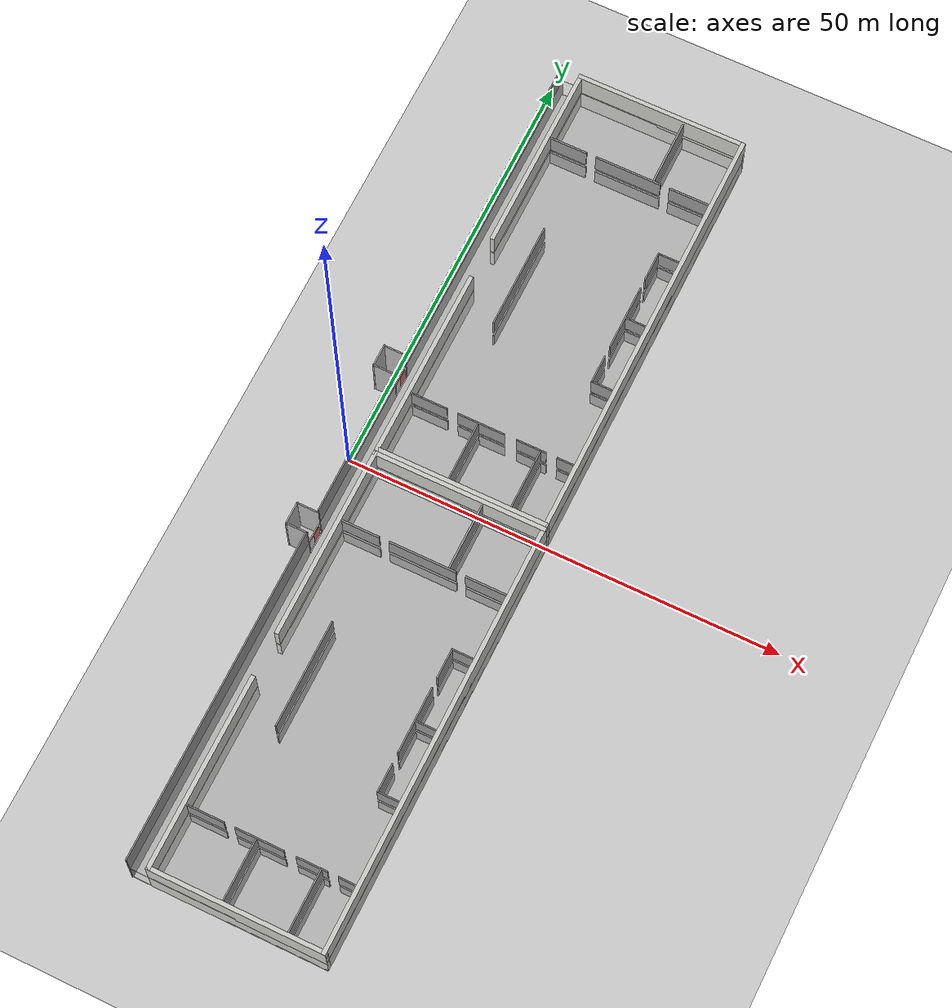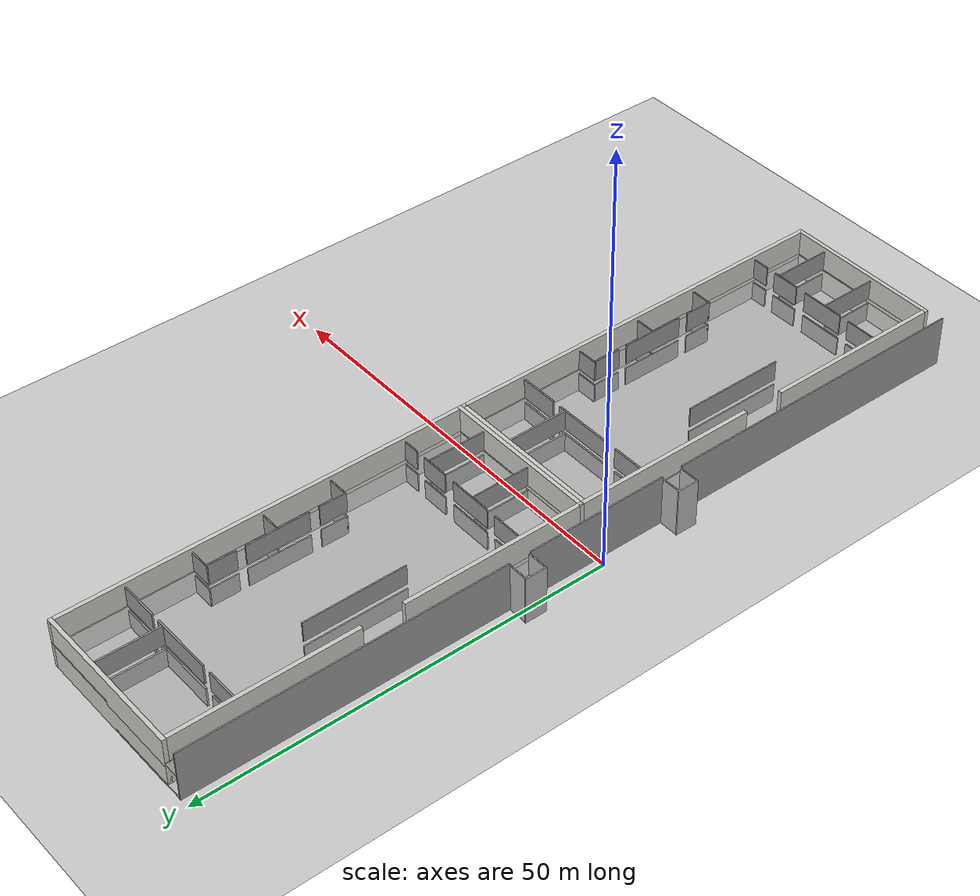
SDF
<sdf version="1.5">
 <world name="default">
  <light name="sun" type="directional">
   <pose>0 0 10 0 -0 0</pose>
   <diffuse>0.8 0.8 0.8 1</diffuse>
   <specular>0.2 0.2 0.2 1</specular>
   <attenuation>
    <range>1000</range>
    <constant>0.9</constant>
    <linear>0.01</linear>
    <quadratic>0.001</quadratic>
   </attenuation>
   <direction>-0.5 0.1 -0.9</direction>
  </light>
  <model name="ground_plane">
   <static>1</static>
   <link name="link">
    <collision name="collision">
     <geometry><plane><normal>0 0 1</normal><size>100 100</size></plane></geometry>
     <surface><friction><ode><mu>100</mu><mu2>50</mu2></ode></friction></surface>
    </collision>
    <visual name="visual">
     <cast_shadows>0</cast_shadows>
     <geometry><plane><normal>0 0 1</normal><size>100 100</size></plane></geometry>
     <material>
      <script><uri>file://media/materials/scripts/gazebo.material</uri><name>Gazebo/Grey</name></script>
     </material>
    </visual>
   </link>
  </model>
  <model name="elevator">
   <pose>0 10 0 0 -0 0</pose>
   <link name="link">
    <inertial>
     <mass>800</mass>
     <inertia><ixx>1</ixx><ixy>0</ixy><ixz>0</ixz><iyy>1</iyy><iyz>0</iyz><izz>1</izz></inertia>
    </inertial>
    <collision name="floor_collision"><geometry><box><size>2.25 2.25 0.15</size></box></geometry></collision>
    <visual name="floor_visual"><geometry><box><size>2.25 2.25 0.15</size></box></geometry></visual>
    <collision name="wall1_collision">
     <pose>1.0745 0.5725 1.125 0 -0 0</pose>
     <geometry><box><size>0.1 1.15 2.25</size></box></geometry>
    </collision>
    <visual name="wall1_visual">
     <pose>1.0745 0.5725 1.125 0 -0 0</pose>
     <geometry><box><size>0.1 1.15 2.25</size></box></geometry>
     <material><script><name>Gazebo/Red</name><uri>__default__</uri></script></material>
    </visual>
    <collision name="wall2_collision">
     <pose>1.0745 -1.0625 1.125 0 -0 0</pose>
     <geometry><box><size>0.1 0.125 2.25</size></box></geometry>
    </collision>
    <visual name="wall2_visual">
     <pose>1.0745 -1.0625 1.125 0 -0 0</pose>
     <geometry><box><size>0.1 0.125 2.25</size></box></geometry>
     <material><script><name>Gazebo/Red</name><uri>__default__</uri></script></material>
    </visual>
   </link>
   <link name="door">
    <pose>1.0745 -0.5 1.125 0 -0 0</pose>
    <collision name="collision"><geometry><box><size>0.08 1 2.25</size></box></geometry></collision>
    <visual name="visual"><geometry><box><size>0.08 1 2.25</size></box></geometry></visual>
    <inertial>
     <inertia><ixx>1</ixx><ixy>0</ixy><ixz>0</ixz><iyy>1</iyy><iyz>0</iyz><izz>1</izz></inertia>
     <mass>1</mass>
    </inertial>
   </link>
   <joint name="door" type="prismatic">
    <parent>link</parent>
    <child>door</child>
    <axis>
     <xyz>0 1 0</xyz>
     <limit><lower>0</lower><upper>1</upper><effort>10</effort></limit>
     <dynamics>
      <damping>2</damping>
      <spring_reference>0</spring_reference>
      <spring_stiffness>0</spring_stiffness>
     </dynamics>
     <use_parent_model_frame>0</use_parent_model_frame>
    </axis>
   </joint>
   <joint name="lift" type="prismatic">
    <parent>world</parent>
    <child>link</child>
    <axis>
     <xyz>0 0 1</xyz>
     <limit><lower>0</lower><upper>10</upper><effort>100000</effort></limit>
     <dynamics>
      <damping>50</damping>
      <spring_reference>0</spring_reference>
      <spring_stiffness>0</spring_stiffness>
     </dynamics>
     <use_parent_model_frame>0</use_parent_model_frame>
    </axis>
    <physics>
     <ode><implicit_spring_damper>1</implicit_spring_damper><limit><cfm>0</cfm><erp>0.2</erp></limit></ode>
    </physics>
   </joint>
   <plugin name="elevator1_plugin" filename="libgazebo_ros_elevator.so">
    <lift_joint>elevator::lift</lift_joint>
    <door_joint>elevator::door</door_joint>
    <floor_height>3.085</floor_height>
    <door_wait_time>10</door_wait_time>
    <topic>gazebo/elevator1</topic>
   </plugin>
  </model>
  <model name="elevator_shaft">
   <static>1</static>
   <link name="link">
    <collision name="shaft_wall1_collision">
     <pose>0 1.25 3 0 -0 0</pose>
     <geometry><box><size>2.5 0.15 6</size></box></geometry>
    </collision>
    <visual name="shaft_wall1_visual">
     <pose>0 1.25 3 0 -0 0</pose>
     <geometry><box><size>2.5 0.15 6</size></box></geometry>
    </visual>
    <collision name="shaft_wall2_collision">
     <pose>0 -1.25 3 0 -0 0</pose>
     <geometry><box><size>2.5 0.15 6</size></box></geometry>
    </collision>
    <visual name="shaft_wall2_visual">
     <pose>0 -1.25 3 0 -0 0</pose>
     <geometry><box><size>2.5 0.15 6</size></box></geometry>
    </visual>
    <collision name="shaft_wall3_collision">
     <pose>-1.25 0 3 0 -0 0</pose>
     <geometry><box><size>0.15 2.7 6</size></box></geometry>
    </collision>
    <visual name="shaft_wall3_visual">
     <pose>-1.25 0 3 0 -0 0</pose>
     <geometry><box><size>0.15 2.7 6</size></box></geometry>
    </visual>
    <collision name="floor0_collision">
     <pose>1.19 0 0.075 0 -0 0</pose>
     <geometry><box><size>0.12 2.5 0.15</size></box></geometry>
    </collision>
    <visual name="floor0_visual">
     <pose>1.19 0 0.075 0 -0 0</pose>
     <geometry><box><size>0.12 2.5 0.15</size></box></geometry>
    </visual>
    <collision name="floor1_collision">
     <pose>1.19 0 3.075 0 -0 0</pose>
     <geometry><box><size>0.12 2.5 0.15</size></box></geometry>
    </collision>
    <visual name="floor1_visual">
     <pose>1.19 0 3.075 0 -0 0</pose>
     <geometry><box><size>0.12 2.5 0.15</size></box></geometry>
    </visual>
   </link>
   <pose>0 10 0 0 -0 0</pose>
  </model>
  <gravity>0 0 -9.8</gravity>
  <magnetic_field>6e-06 2.3e-05 -4.2e-05</magnetic_field>
  <atmosphere type="adiabatic"/>
  <physics name="default_physics" default="0" type="ode">
   <max_step_size>0.001</max_step_size>
   <real_time_factor>1</real_time_factor>
   <real_time_update_rate>1000</real_time_update_rate>
  </physics>
  <scene><ambient>0.4 0.4 0.4 1</ambient><background>0.7 0.7 0.7 1</background><shadows>1</shadows></scene>
  <spherical_coordinates>
   <surface_model>EARTH_WGS84</surface_model>
   <latitude_deg>0</latitude_deg>
   <longitude_deg>0</longitude_deg>
   <elevation>0</elevation>
   <heading_deg>0</heading_deg>
  </spherical_coordinates>
  <model name="office">
   <link name="Wall_1">
    <pose>-24.75 -3e-06 0 0 0 -1.5708</pose>
    <inertial>
     <mass>1</mass>
     <inertia><ixx>1</ixx><ixy>0</ixy><ixz>0</ixz><iyy>1</iyy><iyz>0</iyz><izz>1</izz></inertia>
    </inertial>
    <visual name="Wall_1_Visual">
     <pose>0 0 1.25 0 -0 0</pose>
     <geometry><box><size>20 0.5 3.5</size></box></geometry>
     <material>
      <script><uri>file://media/materials/scripts/gazebo.material</uri><name>Gazebo/CeilingTiled</name></script>
      <ambient>1 1 1 1</ambient>
      <shader type="vertex"><normal_map>__default__</normal_map></shader>
      <diffuse>1 1 1 1</diffuse>
      <specular>0 0 0 1</specular>
      <emissive>0 0 0 1</emissive>
     </material>
     <meta><layer>0</layer></meta>
    </visual>
    <collision name="Wall_1_Collision">
     <pose>0 0 1.25 0 -0 0</pose>
     <geometry><box><size>20 0.5 3.5</size></box></geometry>
     <surface>
      <friction>
       <ode><mu>1</mu><mu2>1</mu2><fdir1>0 0 0</fdir1><slip1>0</slip1><slip2>0</slip2></ode>
       <torsional>
        <coefficient>1</coefficient>
        <patch_radius>0</patch_radius>
        <surface_radius>0</surface_radius>
        <use_patch_radius>1</use_patch_radius>
        <ode><slip>0</slip></ode>
       </torsional>
      </friction>
      <bounce><restitution_coefficient>0</restitution_coefficient><threshold>1e+06</threshold></bounce>
      <contact>
       <collide_without_contact>0</collide_without_contact>
       <collide_without_contact_bitmask>1</collide_without_contact_bitmask>
       <collide_bitmask>1</collide_bitmask>
       <ode>
        <soft_cfm>0</soft_cfm>
        <soft_erp>0.2</soft_erp>
        <kp>1e+13</kp>
        <kd>1</kd>
        <max_vel>0.01</max_vel>
        <min_depth>0</min_depth>
       </ode>
       <bullet>
        <split_impulse>1</split_impulse>
        <split_impulse_penetration_threshold>-0.01</split_impulse_penetration_threshold>
        <soft_cfm>0</soft_cfm>
        <soft_erp>0.2</soft_erp>
        <kp>1e+13</kp>
        <kd>1</kd>
       </bullet>
      </contact>
     </surface>
    </collision>
   </link>
   <link name="Wall_11">
    <pose>24.75 3e-06 0 0 0 -1.5708</pose>
    <inertial>
     <mass>1</mass>
     <inertia><ixx>1</ixx><ixy>0</ixy><ixz>0</ixz><iyy>1</iyy><iyz>0</iyz><izz>1</izz></inertia>
    </inertial>
    <visual name="Wall_11_Visual">
     <pose>0 0 1.25 0 -0 0</pose>
     <geometry><box><size>20 0.5 3.5</size></box></geometry>
     <material>
      <script><uri>file://media/materials/scripts/gazebo.material</uri><name>Gazebo/CeilingTiled</name></script>
      <ambient>1 1 1 1</ambient>
      <shader type="vertex"><normal_map>__default__</normal_map></shader>
      <diffuse>1 1 1 1</diffuse>
      <specular>0 0 0 1</specular>
      <emissive>0 0 0 1</emissive>
     </material>
     <meta><layer>0</layer></meta>
    </visual>
    <collision name="Wall_11_Collision">
     <pose>0 0 1.25 0 -0 0</pose>
     <geometry><box><size>20 0.5 3.5</size></box></geometry>
     <surface>
      <friction>
       <ode><mu>1</mu><mu2>1</mu2><fdir1>0 0 0</fdir1><slip1>0</slip1><slip2>0</slip2></ode>
       <torsional>
        <coefficient>1</coefficient>
        <patch_radius>0</patch_radius>
        <surface_radius>0</surface_radius>
        <use_patch_radius>1</use_patch_radius>
        <ode><slip>0</slip></ode>
       </torsional>
      </friction>
      <bounce><restitution_coefficient>0</restitution_coefficient><threshold>1e+06</threshold></bounce>
      <contact>
       <collide_without_contact>0</collide_without_contact>
       <collide_without_contact_bitmask>1</collide_without_contact_bitmask>
       <collide_bitmask>1</collide_bitmask>
       <ode>
        <soft_cfm>0</soft_cfm>
        <soft_erp>0.2</soft_erp>
        <kp>1e+13</kp>
        <kd>1</kd>
        <max_vel>0.01</max_vel>
        <min_depth>0</min_depth>
       </ode>
       <bullet>
        <split_impulse>1</split_impulse>
        <split_impulse_penetration_threshold>-0.01</split_impulse_penetration_threshold>
        <soft_cfm>0</soft_cfm>
        <soft_erp>0.2</soft_erp>
        <kp>1e+13</kp>
        <kd>1</kd>
       </bullet>
      </contact>
     </surface>
    </collision>
   </link>
   <link name="Wall_13">
    <pose>-16.658 7.127 0 0 0 -1.5708</pose>
    <visual name="Wall_13_Visual">
     <pose>0 0 1.25 0 -0 0</pose>
     <geometry><box><size>4.80017 0.2 2.5</size></box></geometry>
     <material>
      <script><uri>file://media/materials/scripts/gazebo.material</uri><name>Gazebo/Grey</name></script>
      <ambient>1 1 1 1</ambient>
     </material>
     <meta><layer>0</layer></meta>
    </visual>
    <collision name="Wall_13_Collision">
     <pose>0 0 1.25 0 -0 0</pose>
     <geometry><box><size>4.80017 0.2 2.5</size></box></geometry>
     <surface>
      <friction>
       <ode><mu>1</mu><mu2>1</mu2><fdir1>0 0 0</fdir1><slip1>0</slip1><slip2>0</slip2></ode>
       <torsional>
        <coefficient>1</coefficient>
        <patch_radius>0</patch_radius>
        <surface_radius>0</surface_radius>
        <use_patch_radius>1</use_patch_radius>
        <ode><slip>0</slip></ode>
       </torsional>
      </friction>
      <bounce><restitution_coefficient>0</restitution_coefficient><threshold>1e+06</threshold></bounce>
      <contact>
       <collide_without_contact>0</collide_without_contact>
       <collide_without_contact_bitmask>1</collide_without_contact_bitmask>
       <collide_bitmask>1</collide_bitmask>
       <ode>
        <soft_cfm>0</soft_cfm>
        <soft_erp>0.2</soft_erp>
        <kp>1e+13</kp>
        <kd>1</kd>
        <max_vel>0.01</max_vel>
        <min_depth>0</min_depth>
       </ode>
       <bullet>
        <split_impulse>1</split_impulse>
        <split_impulse_penetration_threshold>-0.01</split_impulse_penetration_threshold>
        <soft_cfm>0</soft_cfm>
        <soft_erp>0.2</soft_erp>
        <kp>1e+13</kp>
        <kd>1</kd>
       </bullet>
      </contact>
     </surface>
    </collision>
   </link>
   <link name="Wall_15">
    <pose>-16.658 -0.198 0 0 0 -1.5708</pose>
    <visual name="Wall_15_Visual">
     <pose>0 0 1.25 0 -0 0</pose>
     <geometry><box><size>7.75 0.2 2.5</size></box></geometry>
     <material>
      <script><uri>file://media/materials/scripts/gazebo.material</uri><name>Gazebo/Grey</name></script>
      <ambient>1 1 1 1</ambient>
     </material>
     <meta><layer>0</layer></meta>
    </visual>
    <collision name="Wall_15_Collision">
     <pose>0 0 1.25 0 -0 0</pose>
     <geometry><box><size>7.75 0.2 2.5</size></box></geometry>
     <surface>
      <friction>
       <ode><mu>1</mu><mu2>1</mu2><fdir1>0 0 0</fdir1><slip1>0</slip1><slip2>0</slip2></ode>
       <torsional>
        <coefficient>1</coefficient>
        <patch_radius>0</patch_radius>
        <surface_radius>0</surface_radius>
        <use_patch_radius>1</use_patch_radius>
        <ode><slip>0</slip></ode>
       </torsional>
      </friction>
      <bounce><restitution_coefficient>0</restitution_coefficient><threshold>1e+06</threshold></bounce>
      <contact>
       <collide_without_contact>0</collide_without_contact>
       <collide_without_contact_bitmask>1</collide_without_contact_bitmask>
       <collide_bitmask>1</collide_bitmask>
       <ode>
        <soft_cfm>0</soft_cfm>
        <soft_erp>0.2</soft_erp>
        <kp>1e+13</kp>
        <kd>1</kd>
        <max_vel>0.01</max_vel>
        <min_depth>0</min_depth>
       </ode>
       <bullet>
        <split_impulse>1</split_impulse>
        <split_impulse_penetration_threshold>-0.01</split_impulse_penetration_threshold>
        <soft_cfm>0</soft_cfm>
        <soft_erp>0.2</soft_erp>
        <kp>1e+13</kp>
        <kd>1</kd>
       </bullet>
      </contact>
     </surface>
    </collision>
   </link>
   <link name="Wall_17">
    <pose>-16.658 -7.423 0 0 0 -1.5708</pose>
    <visual name="Wall_17_Visual">
     <pose>0 0 1.25 0 -0 0</pose>
     <geometry><box><size>4.5 0.2 2.5</size></box></geometry>
     <material>
      <script><uri>file://media/materials/scripts/gazebo.material</uri><name>Gazebo/Grey</name></script>
      <ambient>1 1 1 1</ambient>
     </material>
     <meta><layer>0</layer></meta>
    </visual>
    <collision name="Wall_17_Collision">
     <pose>0 0 1.25 0 -0 0</pose>
     <geometry><box><size>4.5 0.2 2.5</size></box></geometry>
     <surface>
      <friction>
       <ode><mu>1</mu><mu2>1</mu2><fdir1>0 0 0</fdir1><slip1>0</slip1><slip2>0</slip2></ode>
       <torsional>
        <coefficient>1</coefficient>
        <patch_radius>0</patch_radius>
        <surface_radius>0</surface_radius>
        <use_patch_radius>1</use_patch_radius>
        <ode><slip>0</slip></ode>
       </torsional>
      </friction>
      <bounce><restitution_coefficient>0</restitution_coefficient><threshold>1e+06</threshold></bounce>
      <contact>
       <collide_without_contact>0</collide_without_contact>
       <collide_without_contact_bitmask>1</collide_without_contact_bitmask>
       <collide_bitmask>1</collide_bitmask>
       <ode>
        <soft_cfm>0</soft_cfm>
        <soft_erp>0.2</soft_erp>
        <kp>1e+13</kp>
        <kd>1</kd>
        <max_vel>0.01</max_vel>
        <min_depth>0</min_depth>
       </ode>
       <bullet>
        <split_impulse>1</split_impulse>
        <split_impulse_penetration_threshold>-0.01</split_impulse_penetration_threshold>
        <soft_cfm>0</soft_cfm>
        <soft_erp>0.2</soft_erp>
        <kp>1e+13</kp>
        <kd>1</kd>
       </bullet>
      </contact>
     </surface>
    </collision>
   </link>
   <link name="Wall_19">
    <pose>-20.703 2.792 0 0 -0 0</pose>
    <visual name="Wall_19_Visual">
     <pose>0 0 1.25 0 -0 0</pose>
     <geometry><box><size>8.04985 0.2 2.5</size></box></geometry>
     <material>
      <script><uri>file://media/materials/scripts/gazebo.material</uri><name>Gazebo/Grey</name></script>
      <ambient>1 1 1 1</ambient>
     </material>
     <meta><layer>0</layer></meta>
    </visual>
    <collision name="Wall_19_Collision">
     <pose>0 0 1.25 0 -0 0</pose>
     <geometry><box><size>8.04985 0.2 2.5</size></box></geometry>
     <surface>
      <friction>
       <ode><mu>1</mu><mu2>1</mu2><fdir1>0 0 0</fdir1><slip1>0</slip1><slip2>0</slip2></ode>
       <torsional>
        <coefficient>1</coefficient>
        <patch_radius>0</patch_radius>
        <surface_radius>0</surface_radius>
        <use_patch_radius>1</use_patch_radius>
        <ode><slip>0</slip></ode>
       </torsional>
      </friction>
      <bounce><restitution_coefficient>0</restitution_coefficient><threshold>1e+06</threshold></bounce>
      <contact>
       <collide_without_contact>0</collide_without_contact>
       <collide_without_contact_bitmask>1</collide_without_contact_bitmask>
       <collide_bitmask>1</collide_bitmask>
       <ode>
        <soft_cfm>0</soft_cfm>
        <soft_erp>0.2</soft_erp>
        <kp>1e+13</kp>
        <kd>1</kd>
        <max_vel>0.01</max_vel>
        <min_depth>0</min_depth>
       </ode>
       <bullet>
        <split_impulse>1</split_impulse>
        <split_impulse_penetration_threshold>-0.01</split_impulse_penetration_threshold>
        <soft_cfm>0</soft_cfm>
        <soft_erp>0.2</soft_erp>
        <kp>1e+13</kp>
        <kd>1</kd>
       </bullet>
      </contact>
     </surface>
    </collision>
   </link>
   <link name="Wall_21">
    <pose>17.2839 8.57905 0 0 0 -1.57072</pose>
    <visual name="Wall_21_Visual">
     <pose>0 0 1.25 0 -0 0</pose>
     <geometry><box><size>2.25 0.15 2.5</size></box></geometry>
     <material>
      <script><uri>file://media/materials/scripts/gazebo.material</uri><name>Gazebo/Grey</name></script>
      <ambient>1 1 1 1</ambient>
     </material>
     <meta><layer>0</layer></meta>
    </visual>
    <collision name="Wall_21_Collision">
     <pose>0 0 1.25 0 -0 0</pose>
     <geometry><box><size>2.25 0.15 2.5</size></box></geometry>
     <surface>
      <friction>
       <ode><mu>1</mu><mu2>1</mu2><fdir1>0 0 0</fdir1><slip1>0</slip1><slip2>0</slip2></ode>
       <torsional>
        <coefficient>1</coefficient>
        <patch_radius>0</patch_radius>
        <surface_radius>0</surface_radius>
        <use_patch_radius>1</use_patch_radius>
        <ode><slip>0</slip></ode>
       </torsional>
      </friction>
      <bounce><restitution_coefficient>0</restitution_coefficient><threshold>1e+06</threshold></bounce>
      <contact>
       <collide_without_contact>0</collide_without_contact>
       <collide_without_contact_bitmask>1</collide_without_contact_bitmask>
       <collide_bitmask>1</collide_bitmask>
       <ode>
        <soft_cfm>0</soft_cfm>
        <soft_erp>0.2</soft_erp>
        <kp>1e+13</kp>
        <kd>1</kd>
        <max_vel>0.01</max_vel>
        <min_depth>0</min_depth>
       </ode>
       <bullet>
        <split_impulse>1</split_impulse>
        <split_impulse_penetration_threshold>-0.01</split_impulse_penetration_threshold>
        <soft_cfm>0</soft_cfm>
        <soft_erp>0.2</soft_erp>
        <kp>1e+13</kp>
        <kd>1</kd>
       </bullet>
      </contact>
     </surface>
    </collision>
   </link>
   <link name="Wall_23">
    <pose>17.2838 4.5041 0 0 0 -1.5708</pose>
    <visual name="Wall_23_Visual">
     <pose>0 0 1.25 0 -0 0</pose>
     <geometry><box><size>3.5 0.15 2.5</size></box></geometry>
     <material>
      <script><uri>file://media/materials/scripts/gazebo.material</uri><name>Gazebo/Grey</name></script>
      <ambient>1 1 1 1</ambient>
     </material>
     <meta><layer>0</layer></meta>
    </visual>
    <collision name="Wall_23_Collision">
     <pose>0 0 1.25 0 -0 0</pose>
     <geometry><box><size>3.5 0.15 2.5</size></box></geometry>
     <surface>
      <friction>
       <ode><mu>1</mu><mu2>1</mu2><fdir1>0 0 0</fdir1><slip1>0</slip1><slip2>0</slip2></ode>
       <torsional>
        <coefficient>1</coefficient>
        <patch_radius>0</patch_radius>
        <surface_radius>0</surface_radius>
        <use_patch_radius>1</use_patch_radius>
        <ode><slip>0</slip></ode>
       </torsional>
      </friction>
      <bounce><restitution_coefficient>0</restitution_coefficient><threshold>1e+06</threshold></bounce>
      <contact>
       <collide_without_contact>0</collide_without_contact>
       <collide_without_contact_bitmask>1</collide_without_contact_bitmask>
       <collide_bitmask>1</collide_bitmask>
       <ode>
        <soft_cfm>0</soft_cfm>
        <soft_erp>0.2</soft_erp>
        <kp>1e+13</kp>
        <kd>1</kd>
        <max_vel>0.01</max_vel>
        <min_depth>0</min_depth>
       </ode>
       <bullet>
        <split_impulse>1</split_impulse>
        <split_impulse_penetration_threshold>-0.01</split_impulse_penetration_threshold>
        <soft_cfm>0</soft_cfm>
        <soft_erp>0.2</soft_erp>
        <kp>1e+13</kp>
        <kd>1</kd>
       </bullet>
      </contact>
     </surface>
    </collision>
   </link>
   <link name="Wall_25">
    <pose>17.2838 -1.3459 0 0 0 -1.5708</pose>
    <visual name="Wall_25_Visual">
     <pose>0 0 1.25 0 -0 0</pose>
     <geometry><box><size>5.5 0.15 2.5</size></box></geometry>
     <material>
      <script><uri>file://media/materials/scripts/gazebo.material</uri><name>Gazebo/Grey</name></script>
      <ambient>1 1 1 1</ambient>
     </material>
     <meta><layer>0</layer></meta>
    </visual>
    <collision name="Wall_25_Collision">
     <pose>0 0 1.25 0 -0 0</pose>
     <geometry><box><size>5.5 0.15 2.5</size></box></geometry>
     <surface>
      <friction>
       <ode><mu>1</mu><mu2>1</mu2><fdir1>0 0 0</fdir1><slip1>0</slip1><slip2>0</slip2></ode>
       <torsional>
        <coefficient>1</coefficient>
        <patch_radius>0</patch_radius>
        <surface_radius>0</surface_radius>
        <use_patch_radius>1</use_patch_radius>
        <ode><slip>0</slip></ode>
       </torsional>
      </friction>
      <bounce><restitution_coefficient>0</restitution_coefficient><threshold>1e+06</threshold></bounce>
      <contact>
       <collide_without_contact>0</collide_without_contact>
       <collide_without_contact_bitmask>1</collide_without_contact_bitmask>
       <collide_bitmask>1</collide_bitmask>
       <ode>
        <soft_cfm>0</soft_cfm>
        <soft_erp>0.2</soft_erp>
        <kp>1e+13</kp>
        <kd>1</kd>
        <max_vel>0.01</max_vel>
        <min_depth>0</min_depth>
       </ode>
       <bullet>
        <split_impulse>1</split_impulse>
        <split_impulse_penetration_threshold>-0.01</split_impulse_penetration_threshold>
        <soft_cfm>0</soft_cfm>
        <soft_erp>0.2</soft_erp>
        <kp>1e+13</kp>
        <kd>1</kd>
       </bullet>
      </contact>
     </surface>
    </collision>
   </link>
   <link name="Wall_27">
    <pose>17.2838 -7.4709 0 0 0 -1.5708</pose>
    <visual name="Wall_27_Visual">
     <pose>0 0 1.25 0 -0 0</pose>
     <geometry><box><size>4.35 0.15 2.5</size></box></geometry>
     <material>
      <script><uri>file://media/materials/scripts/gazebo.material</uri><name>Gazebo/Grey</name></script>
      <ambient>1 1 1 1</ambient>
     </material>
     <meta><layer>0</layer></meta>
    </visual>
    <collision name="Wall_27_Collision">
     <pose>0 0 1.25 0 -0 0</pose>
     <geometry><box><size>4.35 0.15 2.5</size></box></geometry>
     <surface>
      <friction>
       <ode><mu>1</mu><mu2>1</mu2><fdir1>0 0 0</fdir1><slip1>0</slip1><slip2>0</slip2></ode>
       <torsional>
        <coefficient>1</coefficient>
        <patch_radius>0</patch_radius>
        <surface_radius>0</surface_radius>
        <use_patch_radius>1</use_patch_radius>
        <ode><slip>0</slip></ode>
       </torsional>
      </friction>
      <bounce><restitution_coefficient>0</restitution_coefficient><threshold>1e+06</threshold></bounce>
      <contact>
       <collide_without_contact>0</collide_without_contact>
       <collide_without_contact_bitmask>1</collide_without_contact_bitmask>
       <collide_bitmask>1</collide_bitmask>
       <ode>
        <soft_cfm>0</soft_cfm>
        <soft_erp>0.2</soft_erp>
        <kp>1e+13</kp>
        <kd>1</kd>
        <max_vel>0.01</max_vel>
        <min_depth>0</min_depth>
       </ode>
       <bullet>
        <split_impulse>1</split_impulse>
        <split_impulse_penetration_threshold>-0.01</split_impulse_penetration_threshold>
        <soft_cfm>0</soft_cfm>
        <soft_erp>0.2</soft_erp>
        <kp>1e+13</kp>
        <kd>1</kd>
       </bullet>
      </contact>
     </surface>
    </collision>
   </link>
   <link name="Wall_29">
    <pose>20.9993 5.58355 0 0 -0 0</pose>
    <visual name="Wall_29_Visual">
     <pose>0 0 1.25 0 -0 0</pose>
     <geometry><box><size>7.5 0.15 2.5</size></box></geometry>
     <material>
      <script><uri>file://media/materials/scripts/gazebo.material</uri><name>Gazebo/Grey</name></script>
      <ambient>1 1 1 1</ambient>
     </material>
     <meta><layer>0</layer></meta>
    </visual>
    <collision name="Wall_29_Collision">
     <pose>0 0 1.25 0 -0 0</pose>
     <geometry><box><size>7.5 0.15 2.5</size></box></geometry>
     <surface>
      <friction>
       <ode><mu>1</mu><mu2>1</mu2><fdir1>0 0 0</fdir1><slip1>0</slip1><slip2>0</slip2></ode>
       <torsional>
        <coefficient>1</coefficient>
        <patch_radius>0</patch_radius>
        <surface_radius>0</surface_radius>
        <use_patch_radius>1</use_patch_radius>
        <ode><slip>0</slip></ode>
       </torsional>
      </friction>
      <bounce><restitution_coefficient>0</restitution_coefficient><threshold>1e+06</threshold></bounce>
      <contact>
       <collide_without_contact>0</collide_without_contact>
       <collide_without_contact_bitmask>1</collide_without_contact_bitmask>
       <collide_bitmask>1</collide_bitmask>
       <ode>
        <soft_cfm>0</soft_cfm>
        <soft_erp>0.2</soft_erp>
        <kp>1e+13</kp>
        <kd>1</kd>
        <max_vel>0.01</max_vel>
        <min_depth>0</min_depth>
       </ode>
       <bullet>
        <split_impulse>1</split_impulse>
        <split_impulse_penetration_threshold>-0.01</split_impulse_penetration_threshold>
        <soft_cfm>0</soft_cfm>
        <soft_erp>0.2</soft_erp>
        <kp>1e+13</kp>
        <kd>1</kd>
       </bullet>
      </contact>
     </surface>
    </collision>
   </link>
   <link name="Wall_3">
    <pose>-1e-06 9.75 0 0 -0 0</pose>
    <inertial>
     <mass>1</mass>
     <inertia><ixx>1</ixx><ixy>0</ixy><ixz>0</ixz><iyy>1</iyy><iyz>0</iyz><izz>1</izz></inertia>
    </inertial>
    <visual name="Wall_3_Visual">
     <pose>0 0 1.25 0 -0 0</pose>
     <geometry><box><size>50 0.5 3.5</size></box></geometry>
     <material>
      <script><uri>file://media/materials/scripts/gazebo.material</uri><name>Gazebo/CeilingTiled</name></script>
      <ambient>1 1 1 1</ambient>
      <shader type="vertex"><normal_map>__default__</normal_map></shader>
      <diffuse>1 1 1 1</diffuse>
      <specular>0 0 0 1</specular>
      <emissive>0 0 0 1</emissive>
     </material>
     <meta><layer>0</layer></meta>
    </visual>
    <collision name="Wall_3_Collision">
     <pose>0 0 1.25 0 -0 0</pose>
     <geometry><box><size>50 0.5 3.5</size></box></geometry>
     <surface>
      <friction>
       <ode><mu>1</mu><mu2>1</mu2><fdir1>0 0 0</fdir1><slip1>0</slip1><slip2>0</slip2></ode>
       <torsional>
        <coefficient>1</coefficient>
        <patch_radius>0</patch_radius>
        <surface_radius>0</surface_radius>
        <use_patch_radius>1</use_patch_radius>
        <ode><slip>0</slip></ode>
       </torsional>
      </friction>
      <bounce><restitution_coefficient>0</restitution_coefficient><threshold>1e+06</threshold></bounce>
      <contact>
       <collide_without_contact>0</collide_without_contact>
       <collide_without_contact_bitmask>1</collide_without_contact_bitmask>
       <collide_bitmask>1</collide_bitmask>
       <ode>
        <soft_cfm>0</soft_cfm>
        <soft_erp>0.2</soft_erp>
        <kp>1e+13</kp>
        <kd>1</kd>
        <max_vel>0.01</max_vel>
        <min_depth>0</min_depth>
       </ode>
       <bullet>
        <split_impulse>1</split_impulse>
        <split_impulse_penetration_threshold>-0.01</split_impulse_penetration_threshold>
        <soft_cfm>0</soft_cfm>
        <soft_erp>0.2</soft_erp>
        <kp>1e+13</kp>
        <kd>1</kd>
       </bullet>
      </contact>
     </surface>
    </collision>
   </link>
   <link name="Wall_31">
    <pose>20.9993 -1.658 0 0 -0 0</pose>
    <visual name="Wall_31_Visual">
     <pose>0 0 1.25 0 -0 0</pose>
     <geometry><box><size>7.5 0.15 2.5</size></box></geometry>
     <material>
      <script><uri>file://media/materials/scripts/gazebo.material</uri><name>Gazebo/Grey</name></script>
      <ambient>1 1 1 1</ambient>
     </material>
     <meta><layer>0</layer></meta>
    </visual>
    <collision name="Wall_31_Collision">
     <pose>0 0 1.25 0 -0 0</pose>
     <geometry><box><size>7.5 0.15 2.5</size></box></geometry>
     <surface>
      <friction>
       <ode><mu>1</mu><mu2>1</mu2><fdir1>0 0 0</fdir1><slip1>0</slip1><slip2>0</slip2></ode>
       <torsional>
        <coefficient>1</coefficient>
        <patch_radius>0</patch_radius>
        <surface_radius>0</surface_radius>
        <use_patch_radius>1</use_patch_radius>
        <ode><slip>0</slip></ode>
       </torsional>
      </friction>
      <bounce><restitution_coefficient>0</restitution_coefficient><threshold>1e+06</threshold></bounce>
      <contact>
       <collide_without_contact>0</collide_without_contact>
       <collide_without_contact_bitmask>1</collide_without_contact_bitmask>
       <collide_bitmask>1</collide_bitmask>
       <ode>
        <soft_cfm>0</soft_cfm>
        <soft_erp>0.2</soft_erp>
        <kp>1e+13</kp>
        <kd>1</kd>
        <max_vel>0.01</max_vel>
        <min_depth>0</min_depth>
       </ode>
       <bullet>
        <split_impulse>1</split_impulse>
        <split_impulse_penetration_threshold>-0.01</split_impulse_penetration_threshold>
        <soft_cfm>0</soft_cfm>
        <soft_erp>0.2</soft_erp>
        <kp>1e+13</kp>
        <kd>1</kd>
       </bullet>
      </contact>
     </surface>
    </collision>
   </link>
   <link name="Wall_34">
    <pose>-8.97184 8.28865 0 0 0 -1.5708</pose>
    <visual name="Wall_34_Visual">
     <pose>0 0 1.25 0 -0 0</pose>
     <geometry><box><size>2.75032 0.15 2.5</size></box></geometry>
     <material>
      <script><uri>file://media/materials/scripts/gazebo.material</uri><name>Gazebo/Grey</name></script>
      <ambient>1 1 1 1</ambient>
     </material>
     <meta><layer>0</layer></meta>
    </visual>
    <collision name="Wall_34_Collision">
     <pose>0 0 1.25 0 -0 0</pose>
     <geometry><box><size>2.75032 0.15 2.5</size></box></geometry>
     <surface>
      <friction>
       <ode><mu>1</mu><mu2>1</mu2><fdir1>0 0 0</fdir1><slip1>0</slip1><slip2>0</slip2></ode>
       <torsional>
        <coefficient>1</coefficient>
        <patch_radius>0</patch_radius>
        <surface_radius>0</surface_radius>
        <use_patch_radius>1</use_patch_radius>
        <ode><slip>0</slip></ode>
       </torsional>
      </friction>
      <bounce><restitution_coefficient>0</restitution_coefficient><threshold>1e+06</threshold></bounce>
      <contact>
       <collide_without_contact>0</collide_without_contact>
       <collide_without_contact_bitmask>1</collide_without_contact_bitmask>
       <collide_bitmask>1</collide_bitmask>
       <ode>
        <soft_cfm>0</soft_cfm>
        <soft_erp>0.2</soft_erp>
        <kp>1e+13</kp>
        <kd>1</kd>
        <max_vel>0.01</max_vel>
        <min_depth>0</min_depth>
       </ode>
       <bullet>
        <split_impulse>1</split_impulse>
        <split_impulse_penetration_threshold>-0.01</split_impulse_penetration_threshold>
        <soft_cfm>0</soft_cfm>
        <soft_erp>0.2</soft_erp>
        <kp>1e+13</kp>
        <kd>1</kd>
       </bullet>
      </contact>
     </surface>
    </collision>
   </link>
   <link name="Wall_35">
    <pose>-7.25638 6.98865 0 0 -0 0</pose>
    <visual name="Wall_35_Visual">
     <pose>0 0 1.25 0 -0 0</pose>
     <geometry><box><size>3.5 0.15 2.5</size></box></geometry>
     <material>
      <script><uri>file://media/materials/scripts/gazebo.material</uri><name>Gazebo/Grey</name></script>
      <ambient>1 1 1 1</ambient>
     </material>
     <meta><layer>0</layer></meta>
    </visual>
    <collision name="Wall_35_Collision">
     <pose>0 0 1.25 0 -0 0</pose>
     <geometry><box><size>3.5 0.15 2.5</size></box></geometry>
     <surface>
      <friction>
       <ode><mu>1</mu><mu2>1</mu2><fdir1>0 0 0</fdir1><slip1>0</slip1><slip2>0</slip2></ode>
       <torsional>
        <coefficient>1</coefficient>
        <patch_radius>0</patch_radius>
        <surface_radius>0</surface_radius>
        <use_patch_radius>1</use_patch_radius>
        <ode><slip>0</slip></ode>
       </torsional>
      </friction>
      <bounce><restitution_coefficient>0</restitution_coefficient><threshold>1e+06</threshold></bounce>
      <contact>
       <collide_without_contact>0</collide_without_contact>
       <collide_without_contact_bitmask>1</collide_without_contact_bitmask>
       <collide_bitmask>1</collide_bitmask>
       <ode>
        <soft_cfm>0</soft_cfm>
        <soft_erp>0.2</soft_erp>
        <kp>1e+13</kp>
        <kd>1</kd>
        <max_vel>0.01</max_vel>
        <min_depth>0</min_depth>
       </ode>
       <bullet>
        <split_impulse>1</split_impulse>
        <split_impulse_penetration_threshold>-0.01</split_impulse_penetration_threshold>
        <soft_cfm>0</soft_cfm>
        <soft_erp>0.2</soft_erp>
        <kp>1e+13</kp>
        <kd>1</kd>
       </bullet>
      </contact>
     </surface>
    </collision>
   </link>
   <link name="Wall_37">
    <pose>-0.572 6.989 0 0 -0 0</pose>
    <visual name="Wall_37_Visual">
     <pose>0 0 1.25 0 -0 0</pose>
     <geometry><box><size>7.75 0.15 2.5</size></box></geometry>
     <material>
      <script><uri>file://media/materials/scripts/gazebo.material</uri><name>Gazebo/Grey</name></script>
      <ambient>1 1 1 1</ambient>
     </material>
     <meta><layer>0</layer></meta>
    </visual>
    <collision name="Wall_37_Collision">
     <pose>0 0 1.25 0 -0 0</pose>
     <geometry><box><size>7.75 0.15 2.5</size></box></geometry>
     <surface>
      <friction>
       <ode><mu>1</mu><mu2>1</mu2><fdir1>0 0 0</fdir1><slip1>0</slip1><slip2>0</slip2></ode>
       <torsional>
        <coefficient>1</coefficient>
        <patch_radius>0</patch_radius>
        <surface_radius>0</surface_radius>
        <use_patch_radius>1</use_patch_radius>
        <ode><slip>0</slip></ode>
       </torsional>
      </friction>
      <bounce><restitution_coefficient>0</restitution_coefficient><threshold>1e+06</threshold></bounce>
      <contact>
       <collide_without_contact>0</collide_without_contact>
       <collide_without_contact_bitmask>1</collide_without_contact_bitmask>
       <collide_bitmask>1</collide_bitmask>
       <ode>
        <soft_cfm>0</soft_cfm>
        <soft_erp>0.2</soft_erp>
        <kp>1e+13</kp>
        <kd>1</kd>
        <max_vel>0.01</max_vel>
        <min_depth>0</min_depth>
       </ode>
       <bullet>
        <split_impulse>1</split_impulse>
        <split_impulse_penetration_threshold>-0.01</split_impulse_penetration_threshold>
        <soft_cfm>0</soft_cfm>
        <soft_erp>0.2</soft_erp>
        <kp>1e+13</kp>
        <kd>1</kd>
       </bullet>
      </contact>
     </surface>
    </collision>
   </link>
   <link name="Wall_39">
    <pose>6.17808 6.98882 0 0 0 -0.00011</pose>
    <visual name="Wall_39_Visual">
     <pose>0 0 1.25 0 -0 0</pose>
     <geometry><box><size>3.35 0.15 2.5</size></box></geometry>
     <material>
      <script><uri>file://media/materials/scripts/gazebo.material</uri><name>Gazebo/Grey</name></script>
      <ambient>1 1 1 1</ambient>
     </material>
     <meta><layer>0</layer></meta>
    </visual>
    <collision name="Wall_39_Collision">
     <pose>0 0 1.25 0 -0 0</pose>
     <geometry><box><size>3.35 0.15 2.5</size></box></geometry>
     <surface>
      <friction>
       <ode><mu>1</mu><mu2>1</mu2><fdir1>0 0 0</fdir1><slip1>0</slip1><slip2>0</slip2></ode>
       <torsional>
        <coefficient>1</coefficient>
        <patch_radius>0</patch_radius>
        <surface_radius>0</surface_radius>
        <use_patch_radius>1</use_patch_radius>
        <ode><slip>0</slip></ode>
       </torsional>
      </friction>
      <bounce><restitution_coefficient>0</restitution_coefficient><threshold>1e+06</threshold></bounce>
      <contact>
       <collide_without_contact>0</collide_without_contact>
       <collide_without_contact_bitmask>1</collide_without_contact_bitmask>
       <collide_bitmask>1</collide_bitmask>
       <ode>
        <soft_cfm>0</soft_cfm>
        <soft_erp>0.2</soft_erp>
        <kp>1e+13</kp>
        <kd>1</kd>
        <max_vel>0.01</max_vel>
        <min_depth>0</min_depth>
       </ode>
       <bullet>
        <split_impulse>1</split_impulse>
        <split_impulse_penetration_threshold>-0.01</split_impulse_penetration_threshold>
        <soft_cfm>0</soft_cfm>
        <soft_erp>0.2</soft_erp>
        <kp>1e+13</kp>
        <kd>1</kd>
       </bullet>
      </contact>
     </surface>
    </collision>
   </link>
   <link name="Wall_40">
    <pose>7.77816 8.28865 0 0 -0 1.5708</pose>
    <visual name="Wall_40_Visual">
     <pose>0 0 1.25 0 -0 0</pose>
     <geometry><box><size>2.75 0.15 2.5</size></box></geometry>
     <material>
      <script><uri>file://media/materials/scripts/gazebo.material</uri><name>Gazebo/Grey</name></script>
      <ambient>1 1 1 1</ambient>
     </material>
     <meta><layer>0</layer></meta>
    </visual>
    <collision name="Wall_40_Collision">
     <pose>0 0 1.25 0 -0 0</pose>
     <geometry><box><size>2.75 0.15 2.5</size></box></geometry>
     <surface>
      <friction>
       <ode><mu>1</mu><mu2>1</mu2><fdir1>0 0 0</fdir1><slip1>0</slip1><slip2>0</slip2></ode>
       <torsional>
        <coefficient>1</coefficient>
        <patch_radius>0</patch_radius>
        <surface_radius>0</surface_radius>
        <use_patch_radius>1</use_patch_radius>
        <ode><slip>0</slip></ode>
       </torsional>
      </friction>
      <bounce><restitution_coefficient>0</restitution_coefficient><threshold>1e+06</threshold></bounce>
      <contact>
       <collide_without_contact>0</collide_without_contact>
       <collide_without_contact_bitmask>1</collide_without_contact_bitmask>
       <collide_bitmask>1</collide_bitmask>
       <ode>
        <soft_cfm>0</soft_cfm>
        <soft_erp>0.2</soft_erp>
        <kp>1e+13</kp>
        <kd>1</kd>
        <max_vel>0.01</max_vel>
        <min_depth>0</min_depth>
       </ode>
       <bullet>
        <split_impulse>1</split_impulse>
        <split_impulse_penetration_threshold>-0.01</split_impulse_penetration_threshold>
        <soft_cfm>0</soft_cfm>
        <soft_erp>0.2</soft_erp>
        <kp>1e+13</kp>
        <kd>1</kd>
       </bullet>
      </contact>
     </surface>
    </collision>
   </link>
   <link name="Wall_42">
    <pose>-0.516625 8.36956 0 0 0 -1.5708</pose>
    <visual name="Wall_42_Visual">
     <pose>0 0 1.25 0 -0 0</pose>
     <geometry><box><size>2.75 0.15 2.5</size></box></geometry>
     <material>
      <script><uri>file://media/materials/scripts/gazebo.material</uri><name>Gazebo/Grey</name></script>
      <ambient>1 1 1 1</ambient>
     </material>
     <meta><layer>0</layer></meta>
    </visual>
    <collision name="Wall_42_Collision">
     <pose>0 0 1.25 0 -0 0</pose>
     <geometry><box><size>2.75 0.15 2.5</size></box></geometry>
     <surface>
      <friction>
       <ode><mu>1</mu><mu2>1</mu2><fdir1>0 0 0</fdir1><slip1>0</slip1><slip2>0</slip2></ode>
       <torsional>
        <coefficient>1</coefficient>
        <patch_radius>0</patch_radius>
        <surface_radius>0</surface_radius>
        <use_patch_radius>1</use_patch_radius>
        <ode><slip>0</slip></ode>
       </torsional>
      </friction>
      <bounce><restitution_coefficient>0</restitution_coefficient><threshold>1e+06</threshold></bounce>
      <contact>
       <collide_without_contact>0</collide_without_contact>
       <collide_without_contact_bitmask>1</collide_without_contact_bitmask>
       <collide_bitmask>1</collide_bitmask>
       <ode>
        <soft_cfm>0</soft_cfm>
        <soft_erp>0.2</soft_erp>
        <kp>1e+13</kp>
        <kd>1</kd>
        <max_vel>0.01</max_vel>
        <min_depth>0</min_depth>
       </ode>
       <bullet>
        <split_impulse>1</split_impulse>
        <split_impulse_penetration_threshold>-0.01</split_impulse_penetration_threshold>
        <soft_cfm>0</soft_cfm>
        <soft_erp>0.2</soft_erp>
        <kp>1e+13</kp>
        <kd>1</kd>
       </bullet>
      </contact>
     </surface>
    </collision>
   </link>
   <link name="Wall_44">
    <pose>-0.086317 -5.33946 0 0 -0 0</pose>
    <visual name="Wall_44_Visual">
     <pose>0 0 1.25 0 -0 0</pose>
     <geometry><box><size>12.5 0.15 2.5</size></box></geometry>
     <material>
      <script><uri>file://media/materials/scripts/gazebo.material</uri><name>Gazebo/Grey</name></script>
      <ambient>1 1 1 1</ambient>
     </material>
     <meta><layer>0</layer></meta>
    </visual>
    <collision name="Wall_44_Collision">
     <pose>0 0 1.25 0 -0 0</pose>
     <geometry><box><size>12.5 0.15 2.5</size></box></geometry>
     <surface>
      <friction>
       <ode><mu>1</mu><mu2>1</mu2><fdir1>0 0 0</fdir1><slip1>0</slip1><slip2>0</slip2></ode>
       <torsional>
        <coefficient>1</coefficient>
        <patch_radius>0</patch_radius>
        <surface_radius>0</surface_radius>
        <use_patch_radius>1</use_patch_radius>
        <ode><slip>0</slip></ode>
       </torsional>
      </friction>
      <bounce><restitution_coefficient>0</restitution_coefficient><threshold>1e+06</threshold></bounce>
      <contact>
       <collide_without_contact>0</collide_without_contact>
       <collide_without_contact_bitmask>1</collide_without_contact_bitmask>
       <collide_bitmask>1</collide_bitmask>
       <ode>
        <soft_cfm>0</soft_cfm>
        <soft_erp>0.2</soft_erp>
        <kp>1e+13</kp>
        <kd>1</kd>
        <max_vel>0.01</max_vel>
        <min_depth>0</min_depth>
       </ode>
       <bullet>
        <split_impulse>1</split_impulse>
        <split_impulse_penetration_threshold>-0.01</split_impulse_penetration_threshold>
        <soft_cfm>0</soft_cfm>
        <soft_erp>0.2</soft_erp>
        <kp>1e+13</kp>
        <kd>1</kd>
       </bullet>
      </contact>
     </surface>
    </collision>
   </link>
   <link name="Wall_7">
    <pose>-13.75 -9.75 0 0 -0 0</pose>
    <inertial>
     <mass>1</mass>
     <inertia><ixx>1</ixx><ixy>0</ixy><ixz>0</ixz><iyy>1</iyy><iyz>0</iyz><izz>1</izz></inertia>
    </inertial>
    <visual name="Wall_7_Visual">
     <pose>0 0 1.25 0 -0 0</pose>
     <geometry><box><size>22.5 0.5 3.5</size></box></geometry>
     <material>
      <script><uri>file://media/materials/scripts/gazebo.material</uri><name>Gazebo/CeilingTiled</name></script>
      <ambient>1 1 1 1</ambient>
      <shader type="vertex"><normal_map>__default__</normal_map></shader>
      <diffuse>1 1 1 1</diffuse>
      <specular>0 0 0 1</specular>
      <emissive>0 0 0 1</emissive>
     </material>
     <meta><layer>0</layer></meta>
    </visual>
    <collision name="Wall_7_Collision">
     <pose>0 0 1.25 0 -0 0</pose>
     <geometry><box><size>22.5 0.5 3.5</size></box></geometry>
     <surface>
      <friction>
       <ode><mu>1</mu><mu2>1</mu2><fdir1>0 0 0</fdir1><slip1>0</slip1><slip2>0</slip2></ode>
       <torsional>
        <coefficient>1</coefficient>
        <patch_radius>0</patch_radius>
        <surface_radius>0</surface_radius>
        <use_patch_radius>1</use_patch_radius>
        <ode><slip>0</slip></ode>
       </torsional>
      </friction>
      <bounce><restitution_coefficient>0</restitution_coefficient><threshold>1e+06</threshold></bounce>
      <contact>
       <collide_without_contact>0</collide_without_contact>
       <collide_without_contact_bitmask>1</collide_without_contact_bitmask>
       <collide_bitmask>1</collide_bitmask>
       <ode>
        <soft_cfm>0</soft_cfm>
        <soft_erp>0.2</soft_erp>
        <kp>1e+13</kp>
        <kd>1</kd>
        <max_vel>0.01</max_vel>
        <min_depth>0</min_depth>
       </ode>
       <bullet>
        <split_impulse>1</split_impulse>
        <split_impulse_penetration_threshold>-0.01</split_impulse_penetration_threshold>
        <soft_cfm>0</soft_cfm>
        <soft_erp>0.2</soft_erp>
        <kp>1e+13</kp>
        <kd>1</kd>
       </bullet>
      </contact>
     </surface>
    </collision>
   </link>
   <link name="Wall_9">
    <pose>13.7296 -9.74954 0 0 -0 0</pose>
    <inertial>
     <mass>1</mass>
     <inertia><ixx>1</ixx><ixy>0</ixy><ixz>0</ixz><iyy>1</iyy><iyz>0</iyz><izz>1</izz></inertia>
    </inertial>
    <visual name="Wall_9_Visual">
     <pose>0 0 1.25 0 -0 0</pose>
     <geometry><box><size>22.5 0.5 3.5</size></box></geometry>
     <material>
      <script><uri>file://media/materials/scripts/gazebo.material</uri><name>Gazebo/CeilingTiled</name></script>
      <ambient>1 1 1 1</ambient>
      <shader type="vertex"><normal_map>__default__</normal_map></shader>
      <diffuse>1 1 1 1</diffuse>
      <specular>0 0 0 1</specular>
      <emissive>0 0 0 1</emissive>
     </material>
     <meta><layer>0</layer></meta>
    </visual>
    <collision name="Wall_9_Collision">
     <pose>0 0 1.25 0 -0 0</pose>
     <geometry><box><size>22.5 0.5 3.5</size></box></geometry>
     <surface>
      <friction>
       <ode><mu>1</mu><mu2>1</mu2><fdir1>0 0 0</fdir1><slip1>0</slip1><slip2>0</slip2></ode>
       <torsional>
        <coefficient>1</coefficient>
        <patch_radius>0</patch_radius>
        <surface_radius>0</surface_radius>
        <use_patch_radius>1</use_patch_radius>
        <ode><slip>0</slip></ode>
       </torsional>
      </friction>
      <bounce><restitution_coefficient>0</restitution_coefficient><threshold>1e+06</threshold></bounce>
      <contact>
       <collide_without_contact>0</collide_without_contact>
       <collide_without_contact_bitmask>1</collide_without_contact_bitmask>
       <collide_bitmask>1</collide_bitmask>
       <ode>
        <soft_cfm>0</soft_cfm>
        <soft_erp>0.2</soft_erp>
        <kp>1e+13</kp>
        <kd>1</kd>
        <max_vel>0.01</max_vel>
        <min_depth>0</min_depth>
       </ode>
       <bullet>
        <split_impulse>1</split_impulse>
        <split_impulse_penetration_threshold>-0.01</split_impulse_penetration_threshold>
        <soft_cfm>0</soft_cfm>
        <soft_erp>0.2</soft_erp>
        <kp>1e+13</kp>
        <kd>1</kd>
       </bullet>
      </contact>
     </surface>
    </collision>
   </link>
   <static>1</static>
   <pose>13.25 -25 0 0 -0 -1.57079</pose>
  </model>
  <model name="office_clone">
   <link name="Wall_1">
    <pose>-24.75 -3e-06 0 0 0 -1.5708</pose>
    <inertial>
     <mass>1</mass>
     <inertia><ixx>1</ixx><ixy>0</ixy><ixz>0</ixz><iyy>1</iyy><iyz>0</iyz><izz>1</izz></inertia>
    </inertial>
    <visual name="Wall_1_Visual">
     <pose>0 0 1.25 0 -0 0</pose>
     <geometry><box><size>20 0.5 3.5</size></box></geometry>
     <material>
      <script><uri>file://media/materials/scripts/gazebo.material</uri><name>Gazebo/CeilingTiled</name></script>
      <ambient>1 1 1 1</ambient>
      <shader type="vertex"><normal_map>__default__</normal_map></shader>
      <diffuse>1 1 1 1</diffuse>
      <specular>0 0 0 1</specular>
      <emissive>0 0 0 1</emissive>
     </material>
     <meta><layer>0</layer></meta>
    </visual>
    <collision name="Wall_1_Collision">
     <pose>0 0 1.25 0 -0 0</pose>
     <geometry><box><size>20 0.5 3.5</size></box></geometry>
     <surface>
      <friction>
       <ode><mu>1</mu><mu2>1</mu2><fdir1>0 0 0</fdir1><slip1>0</slip1><slip2>0</slip2></ode>
       <torsional>
        <coefficient>1</coefficient>
        <patch_radius>0</patch_radius>
        <surface_radius>0</surface_radius>
        <use_patch_radius>1</use_patch_radius>
        <ode><slip>0</slip></ode>
       </torsional>
      </friction>
      <bounce><restitution_coefficient>0</restitution_coefficient><threshold>1e+06</threshold></bounce>
      <contact>
       <collide_without_contact>0</collide_without_contact>
       <collide_without_contact_bitmask>1</collide_without_contact_bitmask>
       <collide_bitmask>1</collide_bitmask>
       <ode>
        <soft_cfm>0</soft_cfm>
        <soft_erp>0.2</soft_erp>
        <kp>1e+13</kp>
        <kd>1</kd>
        <max_vel>0.01</max_vel>
        <min_depth>0</min_depth>
       </ode>
       <bullet>
        <split_impulse>1</split_impulse>
        <split_impulse_penetration_threshold>-0.01</split_impulse_penetration_threshold>
        <soft_cfm>0</soft_cfm>
        <soft_erp>0.2</soft_erp>
        <kp>1e+13</kp>
        <kd>1</kd>
       </bullet>
      </contact>
     </surface>
    </collision>
   </link>
   <link name="Wall_11">
    <pose>24.75 3e-06 0 0 0 -1.5708</pose>
    <inertial>
     <mass>1</mass>
     <inertia><ixx>1</ixx><ixy>0</ixy><ixz>0</ixz><iyy>1</iyy><iyz>0</iyz><izz>1</izz></inertia>
    </inertial>
    <visual name="Wall_11_Visual">
     <pose>0 0 1.25 0 -0 0</pose>
     <geometry><box><size>20 0.5 3.5</size></box></geometry>
     <material>
      <script><uri>file://media/materials/scripts/gazebo.material</uri><name>Gazebo/CeilingTiled</name></script>
      <ambient>1 1 1 1</ambient>
      <shader type="vertex"><normal_map>__default__</normal_map></shader>
      <diffuse>1 1 1 1</diffuse>
      <specular>0 0 0 1</specular>
      <emissive>0 0 0 1</emissive>
     </material>
     <meta><layer>0</layer></meta>
    </visual>
    <collision name="Wall_11_Collision">
     <pose>0 0 1.25 0 -0 0</pose>
     <geometry><box><size>20 0.5 3.5</size></box></geometry>
     <surface>
      <friction>
       <ode><mu>1</mu><mu2>1</mu2><fdir1>0 0 0</fdir1><slip1>0</slip1><slip2>0</slip2></ode>
       <torsional>
        <coefficient>1</coefficient>
        <patch_radius>0</patch_radius>
        <surface_radius>0</surface_radius>
        <use_patch_radius>1</use_patch_radius>
        <ode><slip>0</slip></ode>
       </torsional>
      </friction>
      <bounce><restitution_coefficient>0</restitution_coefficient><threshold>1e+06</threshold></bounce>
      <contact>
       <collide_without_contact>0</collide_without_contact>
       <collide_without_contact_bitmask>1</collide_without_contact_bitmask>
       <collide_bitmask>1</collide_bitmask>
       <ode>
        <soft_cfm>0</soft_cfm>
        <soft_erp>0.2</soft_erp>
        <kp>1e+13</kp>
        <kd>1</kd>
        <max_vel>0.01</max_vel>
        <min_depth>0</min_depth>
       </ode>
       <bullet>
        <split_impulse>1</split_impulse>
        <split_impulse_penetration_threshold>-0.01</split_impulse_penetration_threshold>
        <soft_cfm>0</soft_cfm>
        <soft_erp>0.2</soft_erp>
        <kp>1e+13</kp>
        <kd>1</kd>
       </bullet>
      </contact>
     </surface>
    </collision>
   </link>
   <link name="Wall_13">
    <pose>-16.658 7.127 0 0 0 -1.5708</pose>
    <visual name="Wall_13_Visual">
     <pose>0 0 1.25 0 -0 0</pose>
     <geometry><box><size>4.80017 0.2 2.5</size></box></geometry>
     <material>
      <script><uri>file://media/materials/scripts/gazebo.material</uri><name>Gazebo/Grey</name></script>
      <ambient>1 1 1 1</ambient>
     </material>
     <meta><layer>0</layer></meta>
    </visual>
    <collision name="Wall_13_Collision">
     <pose>0 0 1.25 0 -0 0</pose>
     <geometry><box><size>4.80017 0.2 2.5</size></box></geometry>
     <surface>
      <friction>
       <ode><mu>1</mu><mu2>1</mu2><fdir1>0 0 0</fdir1><slip1>0</slip1><slip2>0</slip2></ode>
       <torsional>
        <coefficient>1</coefficient>
        <patch_radius>0</patch_radius>
        <surface_radius>0</surface_radius>
        <use_patch_radius>1</use_patch_radius>
        <ode><slip>0</slip></ode>
       </torsional>
      </friction>
      <bounce><restitution_coefficient>0</restitution_coefficient><threshold>1e+06</threshold></bounce>
      <contact>
       <collide_without_contact>0</collide_without_contact>
       <collide_without_contact_bitmask>1</collide_without_contact_bitmask>
       <collide_bitmask>1</collide_bitmask>
       <ode>
        <soft_cfm>0</soft_cfm>
        <soft_erp>0.2</soft_erp>
        <kp>1e+13</kp>
        <kd>1</kd>
        <max_vel>0.01</max_vel>
        <min_depth>0</min_depth>
       </ode>
       <bullet>
        <split_impulse>1</split_impulse>
        <split_impulse_penetration_threshold>-0.01</split_impulse_penetration_threshold>
        <soft_cfm>0</soft_cfm>
        <soft_erp>0.2</soft_erp>
        <kp>1e+13</kp>
        <kd>1</kd>
       </bullet>
      </contact>
     </surface>
    </collision>
   </link>
   <link name="Wall_15">
    <pose>-16.658 -0.198 0 0 0 -1.5708</pose>
    <visual name="Wall_15_Visual">
     <pose>0 0 1.25 0 -0 0</pose>
     <geometry><box><size>7.75 0.2 2.5</size></box></geometry>
     <material>
      <script><uri>file://media/materials/scripts/gazebo.material</uri><name>Gazebo/Grey</name></script>
      <ambient>1 1 1 1</ambient>
     </material>
     <meta><layer>0</layer></meta>
    </visual>
    <collision name="Wall_15_Collision">
     <pose>0 0 1.25 0 -0 0</pose>
     <geometry><box><size>7.75 0.2 2.5</size></box></geometry>
     <surface>
      <friction>
       <ode><mu>1</mu><mu2>1</mu2><fdir1>0 0 0</fdir1><slip1>0</slip1><slip2>0</slip2></ode>
       <torsional>
        <coefficient>1</coefficient>
        <patch_radius>0</patch_radius>
        <surface_radius>0</surface_radius>
        <use_patch_radius>1</use_patch_radius>
        <ode><slip>0</slip></ode>
       </torsional>
      </friction>
      <bounce><restitution_coefficient>0</restitution_coefficient><threshold>1e+06</threshold></bounce>
      <contact>
       <collide_without_contact>0</collide_without_contact>
       <collide_without_contact_bitmask>1</collide_without_contact_bitmask>
       <collide_bitmask>1</collide_bitmask>
       <ode>
        <soft_cfm>0</soft_cfm>
        <soft_erp>0.2</soft_erp>
        <kp>1e+13</kp>
        <kd>1</kd>
        <max_vel>0.01</max_vel>
        <min_depth>0</min_depth>
       </ode>
       <bullet>
        <split_impulse>1</split_impulse>
        <split_impulse_penetration_threshold>-0.01</split_impulse_penetration_threshold>
        <soft_cfm>0</soft_cfm>
        <soft_erp>0.2</soft_erp>
        <kp>1e+13</kp>
        <kd>1</kd>
       </bullet>
      </contact>
     </surface>
    </collision>
   </link>
   <link name="Wall_17">
    <pose>-16.658 -7.423 0 0 0 -1.5708</pose>
    <visual name="Wall_17_Visual">
     <pose>0 0 1.25 0 -0 0</pose>
     <geometry><box><size>4.5 0.2 2.5</size></box></geometry>
     <material>
      <script><uri>file://media/materials/scripts/gazebo.material</uri><name>Gazebo/Grey</name></script>
      <ambient>1 1 1 1</ambient>
     </material>
     <meta><layer>0</layer></meta>
    </visual>
    <collision name="Wall_17_Collision">
     <pose>0 0 1.25 0 -0 0</pose>
     <geometry><box><size>4.5 0.2 2.5</size></box></geometry>
     <surface>
      <friction>
       <ode><mu>1</mu><mu2>1</mu2><fdir1>0 0 0</fdir1><slip1>0</slip1><slip2>0</slip2></ode>
       <torsional>
        <coefficient>1</coefficient>
        <patch_radius>0</patch_radius>
        <surface_radius>0</surface_radius>
        <use_patch_radius>1</use_patch_radius>
        <ode><slip>0</slip></ode>
       </torsional>
      </friction>
      <bounce><restitution_coefficient>0</restitution_coefficient><threshold>1e+06</threshold></bounce>
      <contact>
       <collide_without_contact>0</collide_without_contact>
       <collide_without_contact_bitmask>1</collide_without_contact_bitmask>
       <collide_bitmask>1</collide_bitmask>
       <ode>
        <soft_cfm>0</soft_cfm>
        <soft_erp>0.2</soft_erp>
        <kp>1e+13</kp>
        <kd>1</kd>
        <max_vel>0.01</max_vel>
        <min_depth>0</min_depth>
       </ode>
       <bullet>
        <split_impulse>1</split_impulse>
        <split_impulse_penetration_threshold>-0.01</split_impulse_penetration_threshold>
        <soft_cfm>0</soft_cfm>
        <soft_erp>0.2</soft_erp>
        <kp>1e+13</kp>
        <kd>1</kd>
       </bullet>
      </contact>
     </surface>
    </collision>
   </link>
   <link name="Wall_19">
    <pose>-20.703 2.792 0 0 -0 0</pose>
    <visual name="Wall_19_Visual">
     <pose>0 0 1.25 0 -0 0</pose>
     <geometry><box><size>8.04985 0.2 2.5</size></box></geometry>
     <material>
      <script><uri>file://media/materials/scripts/gazebo.material</uri><name>Gazebo/Grey</name></script>
      <ambient>1 1 1 1</ambient>
     </material>
     <meta><layer>0</layer></meta>
    </visual>
    <collision name="Wall_19_Collision">
     <pose>0 0 1.25 0 -0 0</pose>
     <geometry><box><size>8.04985 0.2 2.5</size></box></geometry>
     <surface>
      <friction>
       <ode><mu>1</mu><mu2>1</mu2><fdir1>0 0 0</fdir1><slip1>0</slip1><slip2>0</slip2></ode>
       <torsional>
        <coefficient>1</coefficient>
        <patch_radius>0</patch_radius>
        <surface_radius>0</surface_radius>
        <use_patch_radius>1</use_patch_radius>
        <ode><slip>0</slip></ode>
       </torsional>
      </friction>
      <bounce><restitution_coefficient>0</restitution_coefficient><threshold>1e+06</threshold></bounce>
      <contact>
       <collide_without_contact>0</collide_without_contact>
       <collide_without_contact_bitmask>1</collide_without_contact_bitmask>
       <collide_bitmask>1</collide_bitmask>
       <ode>
        <soft_cfm>0</soft_cfm>
        <soft_erp>0.2</soft_erp>
        <kp>1e+13</kp>
        <kd>1</kd>
        <max_vel>0.01</max_vel>
        <min_depth>0</min_depth>
       </ode>
       <bullet>
        <split_impulse>1</split_impulse>
        <split_impulse_penetration_threshold>-0.01</split_impulse_penetration_threshold>
        <soft_cfm>0</soft_cfm>
        <soft_erp>0.2</soft_erp>
        <kp>1e+13</kp>
        <kd>1</kd>
       </bullet>
      </contact>
     </surface>
    </collision>
   </link>
   <link name="Wall_21">
    <pose>17.2839 8.57905 0 0 0 -1.57072</pose>
    <visual name="Wall_21_Visual">
     <pose>0 0 1.25 0 -0 0</pose>
     <geometry><box><size>2.25 0.15 2.5</size></box></geometry>
     <material>
      <script><uri>file://media/materials/scripts/gazebo.material</uri><name>Gazebo/Grey</name></script>
      <ambient>1 1 1 1</ambient>
     </material>
     <meta><layer>0</layer></meta>
    </visual>
    <collision name="Wall_21_Collision">
     <pose>0 0 1.25 0 -0 0</pose>
     <geometry><box><size>2.25 0.15 2.5</size></box></geometry>
     <surface>
      <friction>
       <ode><mu>1</mu><mu2>1</mu2><fdir1>0 0 0</fdir1><slip1>0</slip1><slip2>0</slip2></ode>
       <torsional>
        <coefficient>1</coefficient>
        <patch_radius>0</patch_radius>
        <surface_radius>0</surface_radius>
        <use_patch_radius>1</use_patch_radius>
        <ode><slip>0</slip></ode>
       </torsional>
      </friction>
      <bounce><restitution_coefficient>0</restitution_coefficient><threshold>1e+06</threshold></bounce>
      <contact>
       <collide_without_contact>0</collide_without_contact>
       <collide_without_contact_bitmask>1</collide_without_contact_bitmask>
       <collide_bitmask>1</collide_bitmask>
       <ode>
        <soft_cfm>0</soft_cfm>
        <soft_erp>0.2</soft_erp>
        <kp>1e+13</kp>
        <kd>1</kd>
        <max_vel>0.01</max_vel>
        <min_depth>0</min_depth>
       </ode>
       <bullet>
        <split_impulse>1</split_impulse>
        <split_impulse_penetration_threshold>-0.01</split_impulse_penetration_threshold>
        <soft_cfm>0</soft_cfm>
        <soft_erp>0.2</soft_erp>
        <kp>1e+13</kp>
        <kd>1</kd>
       </bullet>
      </contact>
     </surface>
    </collision>
   </link>
   <link name="Wall_23">
    <pose>17.2838 4.5041 0 0 0 -1.5708</pose>
    <visual name="Wall_23_Visual">
     <pose>0 0 1.25 0 -0 0</pose>
     <geometry><box><size>3.5 0.15 2.5</size></box></geometry>
     <material>
      <script><uri>file://media/materials/scripts/gazebo.material</uri><name>Gazebo/Grey</name></script>
      <ambient>1 1 1 1</ambient>
     </material>
     <meta><layer>0</layer></meta>
    </visual>
    <collision name="Wall_23_Collision">
     <pose>0 0 1.25 0 -0 0</pose>
     <geometry><box><size>3.5 0.15 2.5</size></box></geometry>
     <surface>
      <friction>
       <ode><mu>1</mu><mu2>1</mu2><fdir1>0 0 0</fdir1><slip1>0</slip1><slip2>0</slip2></ode>
       <torsional>
        <coefficient>1</coefficient>
        <patch_radius>0</patch_radius>
        <surface_radius>0</surface_radius>
        <use_patch_radius>1</use_patch_radius>
        <ode><slip>0</slip></ode>
       </torsional>
      </friction>
      <bounce><restitution_coefficient>0</restitution_coefficient><threshold>1e+06</threshold></bounce>
      <contact>
       <collide_without_contact>0</collide_without_contact>
       <collide_without_contact_bitmask>1</collide_without_contact_bitmask>
       <collide_bitmask>1</collide_bitmask>
       <ode>
        <soft_cfm>0</soft_cfm>
        <soft_erp>0.2</soft_erp>
        <kp>1e+13</kp>
        <kd>1</kd>
        <max_vel>0.01</max_vel>
        <min_depth>0</min_depth>
       </ode>
       <bullet>
        <split_impulse>1</split_impulse>
        <split_impulse_penetration_threshold>-0.01</split_impulse_penetration_threshold>
        <soft_cfm>0</soft_cfm>
        <soft_erp>0.2</soft_erp>
        <kp>1e+13</kp>
        <kd>1</kd>
       </bullet>
      </contact>
     </surface>
    </collision>
   </link>
   <link name="Wall_25">
    <pose>17.2838 -1.3459 0 0 0 -1.5708</pose>
    <visual name="Wall_25_Visual">
     <pose>0 0 1.25 0 -0 0</pose>
     <geometry><box><size>5.5 0.15 2.5</size></box></geometry>
     <material>
      <script><uri>file://media/materials/scripts/gazebo.material</uri><name>Gazebo/Grey</name></script>
      <ambient>1 1 1 1</ambient>
     </material>
     <meta><layer>0</layer></meta>
    </visual>
    <collision name="Wall_25_Collision">
     <pose>0 0 1.25 0 -0 0</pose>
     <geometry><box><size>5.5 0.15 2.5</size></box></geometry>
     <surface>
      <friction>
       <ode><mu>1</mu><mu2>1</mu2><fdir1>0 0 0</fdir1><slip1>0</slip1><slip2>0</slip2></ode>
       <torsional>
        <coefficient>1</coefficient>
        <patch_radius>0</patch_radius>
        <surface_radius>0</surface_radius>
        <use_patch_radius>1</use_patch_radius>
        <ode><slip>0</slip></ode>
       </torsional>
      </friction>
      <bounce><restitution_coefficient>0</restitution_coefficient><threshold>1e+06</threshold></bounce>
      <contact>
       <collide_without_contact>0</collide_without_contact>
       <collide_without_contact_bitmask>1</collide_without_contact_bitmask>
       <collide_bitmask>1</collide_bitmask>
       <ode>
        <soft_cfm>0</soft_cfm>
        <soft_erp>0.2</soft_erp>
        <kp>1e+13</kp>
        <kd>1</kd>
        <max_vel>0.01</max_vel>
        <min_depth>0</min_depth>
       </ode>
       <bullet>
        <split_impulse>1</split_impulse>
        <split_impulse_penetration_threshold>-0.01</split_impulse_penetration_threshold>
        <soft_cfm>0</soft_cfm>
        <soft_erp>0.2</soft_erp>
        <kp>1e+13</kp>
        <kd>1</kd>
       </bullet>
      </contact>
     </surface>
    </collision>
   </link>
   <link name="Wall_27">
    <pose>17.2838 -7.4709 0 0 0 -1.5708</pose>
    <visual name="Wall_27_Visual">
     <pose>0 0 1.25 0 -0 0</pose>
     <geometry><box><size>4.35 0.15 2.5</size></box></geometry>
     <material>
      <script><uri>file://media/materials/scripts/gazebo.material</uri><name>Gazebo/Grey</name></script>
      <ambient>1 1 1 1</ambient>
     </material>
     <meta><layer>0</layer></meta>
    </visual>
    <collision name="Wall_27_Collision">
     <pose>0 0 1.25 0 -0 0</pose>
     <geometry><box><size>4.35 0.15 2.5</size></box></geometry>
     <surface>
      <friction>
       <ode><mu>1</mu><mu2>1</mu2><fdir1>0 0 0</fdir1><slip1>0</slip1><slip2>0</slip2></ode>
       <torsional>
        <coefficient>1</coefficient>
        <patch_radius>0</patch_radius>
        <surface_radius>0</surface_radius>
        <use_patch_radius>1</use_patch_radius>
        <ode><slip>0</slip></ode>
       </torsional>
      </friction>
      <bounce><restitution_coefficient>0</restitution_coefficient><threshold>1e+06</threshold></bounce>
      <contact>
       <collide_without_contact>0</collide_without_contact>
       <collide_without_contact_bitmask>1</collide_without_contact_bitmask>
       <collide_bitmask>1</collide_bitmask>
       <ode>
        <soft_cfm>0</soft_cfm>
        <soft_erp>0.2</soft_erp>
        <kp>1e+13</kp>
        <kd>1</kd>
        <max_vel>0.01</max_vel>
        <min_depth>0</min_depth>
       </ode>
       <bullet>
        <split_impulse>1</split_impulse>
        <split_impulse_penetration_threshold>-0.01</split_impulse_penetration_threshold>
        <soft_cfm>0</soft_cfm>
        <soft_erp>0.2</soft_erp>
        <kp>1e+13</kp>
        <kd>1</kd>
       </bullet>
      </contact>
     </surface>
    </collision>
   </link>
   <link name="Wall_29">
    <pose>20.9993 5.58355 0 0 -0 0</pose>
    <visual name="Wall_29_Visual">
     <pose>0 0 1.25 0 -0 0</pose>
     <geometry><box><size>7.5 0.15 2.5</size></box></geometry>
     <material>
      <script><uri>file://media/materials/scripts/gazebo.material</uri><name>Gazebo/Grey</name></script>
      <ambient>1 1 1 1</ambient>
     </material>
     <meta><layer>0</layer></meta>
    </visual>
    <collision name="Wall_29_Collision">
     <pose>0 0 1.25 0 -0 0</pose>
     <geometry><box><size>7.5 0.15 2.5</size></box></geometry>
     <surface>
      <friction>
       <ode><mu>1</mu><mu2>1</mu2><fdir1>0 0 0</fdir1><slip1>0</slip1><slip2>0</slip2></ode>
       <torsional>
        <coefficient>1</coefficient>
        <patch_radius>0</patch_radius>
        <surface_radius>0</surface_radius>
        <use_patch_radius>1</use_patch_radius>
        <ode><slip>0</slip></ode>
       </torsional>
      </friction>
      <bounce><restitution_coefficient>0</restitution_coefficient><threshold>1e+06</threshold></bounce>
      <contact>
       <collide_without_contact>0</collide_without_contact>
       <collide_without_contact_bitmask>1</collide_without_contact_bitmask>
       <collide_bitmask>1</collide_bitmask>
       <ode>
        <soft_cfm>0</soft_cfm>
        <soft_erp>0.2</soft_erp>
        <kp>1e+13</kp>
        <kd>1</kd>
        <max_vel>0.01</max_vel>
        <min_depth>0</min_depth>
       </ode>
       <bullet>
        <split_impulse>1</split_impulse>
        <split_impulse_penetration_threshold>-0.01</split_impulse_penetration_threshold>
        <soft_cfm>0</soft_cfm>
        <soft_erp>0.2</soft_erp>
        <kp>1e+13</kp>
        <kd>1</kd>
       </bullet>
      </contact>
     </surface>
    </collision>
   </link>
   <link name="Wall_3">
    <pose>-1e-06 9.75 0 0 -0 0</pose>
    <inertial>
     <mass>1</mass>
     <inertia><ixx>1</ixx><ixy>0</ixy><ixz>0</ixz><iyy>1</iyy><iyz>0</iyz><izz>1</izz></inertia>
    </inertial>
    <visual name="Wall_3_Visual">
     <pose>0 0 1.25 0 -0 0</pose>
     <geometry><box><size>50 0.5 3.5</size></box></geometry>
     <material>
      <script><uri>file://media/materials/scripts/gazebo.material</uri><name>Gazebo/CeilingTiled</name></script>
      <ambient>1 1 1 1</ambient>
      <shader type="vertex"><normal_map>__default__</normal_map></shader>
      <diffuse>1 1 1 1</diffuse>
      <specular>0 0 0 1</specular>
      <emissive>0 0 0 1</emissive>
     </material>
     <meta><layer>0</layer></meta>
    </visual>
    <collision name="Wall_3_Collision">
     <pose>0 0 1.25 0 -0 0</pose>
     <geometry><box><size>50 0.5 3.5</size></box></geometry>
     <surface>
      <friction>
       <ode><mu>1</mu><mu2>1</mu2><fdir1>0 0 0</fdir1><slip1>0</slip1><slip2>0</slip2></ode>
       <torsional>
        <coefficient>1</coefficient>
        <patch_radius>0</patch_radius>
        <surface_radius>0</surface_radius>
        <use_patch_radius>1</use_patch_radius>
        <ode><slip>0</slip></ode>
       </torsional>
      </friction>
      <bounce><restitution_coefficient>0</restitution_coefficient><threshold>1e+06</threshold></bounce>
      <contact>
       <collide_without_contact>0</collide_without_contact>
       <collide_without_contact_bitmask>1</collide_without_contact_bitmask>
       <collide_bitmask>1</collide_bitmask>
       <ode>
        <soft_cfm>0</soft_cfm>
        <soft_erp>0.2</soft_erp>
        <kp>1e+13</kp>
        <kd>1</kd>
        <max_vel>0.01</max_vel>
        <min_depth>0</min_depth>
       </ode>
       <bullet>
        <split_impulse>1</split_impulse>
        <split_impulse_penetration_threshold>-0.01</split_impulse_penetration_threshold>
        <soft_cfm>0</soft_cfm>
        <soft_erp>0.2</soft_erp>
        <kp>1e+13</kp>
        <kd>1</kd>
       </bullet>
      </contact>
     </surface>
    </collision>
   </link>
   <link name="Wall_31">
    <pose>20.9993 -1.658 0 0 -0 0</pose>
    <visual name="Wall_31_Visual">
     <pose>0 0 1.25 0 -0 0</pose>
     <geometry><box><size>7.5 0.15 2.5</size></box></geometry>
     <material>
      <script><uri>file://media/materials/scripts/gazebo.material</uri><name>Gazebo/Grey</name></script>
      <ambient>1 1 1 1</ambient>
     </material>
     <meta><layer>0</layer></meta>
    </visual>
    <collision name="Wall_31_Collision">
     <pose>0 0 1.25 0 -0 0</pose>
     <geometry><box><size>7.5 0.15 2.5</size></box></geometry>
     <surface>
      <friction>
       <ode><mu>1</mu><mu2>1</mu2><fdir1>0 0 0</fdir1><slip1>0</slip1><slip2>0</slip2></ode>
       <torsional>
        <coefficient>1</coefficient>
        <patch_radius>0</patch_radius>
        <surface_radius>0</surface_radius>
        <use_patch_radius>1</use_patch_radius>
        <ode><slip>0</slip></ode>
       </torsional>
      </friction>
      <bounce><restitution_coefficient>0</restitution_coefficient><threshold>1e+06</threshold></bounce>
      <contact>
       <collide_without_contact>0</collide_without_contact>
       <collide_without_contact_bitmask>1</collide_without_contact_bitmask>
       <collide_bitmask>1</collide_bitmask>
       <ode>
        <soft_cfm>0</soft_cfm>
        <soft_erp>0.2</soft_erp>
        <kp>1e+13</kp>
        <kd>1</kd>
        <max_vel>0.01</max_vel>
        <min_depth>0</min_depth>
       </ode>
       <bullet>
        <split_impulse>1</split_impulse>
        <split_impulse_penetration_threshold>-0.01</split_impulse_penetration_threshold>
        <soft_cfm>0</soft_cfm>
        <soft_erp>0.2</soft_erp>
        <kp>1e+13</kp>
        <kd>1</kd>
       </bullet>
      </contact>
     </surface>
    </collision>
   </link>
   <link name="Wall_34">
    <pose>-8.97184 8.28865 0 0 0 -1.5708</pose>
    <visual name="Wall_34_Visual">
     <pose>0 0 1.25 0 -0 0</pose>
     <geometry><box><size>2.75032 0.15 2.5</size></box></geometry>
     <material>
      <script><uri>file://media/materials/scripts/gazebo.material</uri><name>Gazebo/Grey</name></script>
      <ambient>1 1 1 1</ambient>
     </material>
     <meta><layer>0</layer></meta>
    </visual>
    <collision name="Wall_34_Collision">
     <pose>0 0 1.25 0 -0 0</pose>
     <geometry><box><size>2.75032 0.15 2.5</size></box></geometry>
     <surface>
      <friction>
       <ode><mu>1</mu><mu2>1</mu2><fdir1>0 0 0</fdir1><slip1>0</slip1><slip2>0</slip2></ode>
       <torsional>
        <coefficient>1</coefficient>
        <patch_radius>0</patch_radius>
        <surface_radius>0</surface_radius>
        <use_patch_radius>1</use_patch_radius>
        <ode><slip>0</slip></ode>
       </torsional>
      </friction>
      <bounce><restitution_coefficient>0</restitution_coefficient><threshold>1e+06</threshold></bounce>
      <contact>
       <collide_without_contact>0</collide_without_contact>
       <collide_without_contact_bitmask>1</collide_without_contact_bitmask>
       <collide_bitmask>1</collide_bitmask>
       <ode>
        <soft_cfm>0</soft_cfm>
        <soft_erp>0.2</soft_erp>
        <kp>1e+13</kp>
        <kd>1</kd>
        <max_vel>0.01</max_vel>
        <min_depth>0</min_depth>
       </ode>
       <bullet>
        <split_impulse>1</split_impulse>
        <split_impulse_penetration_threshold>-0.01</split_impulse_penetration_threshold>
        <soft_cfm>0</soft_cfm>
        <soft_erp>0.2</soft_erp>
        <kp>1e+13</kp>
        <kd>1</kd>
       </bullet>
      </contact>
     </surface>
    </collision>
   </link>
   <link name="Wall_35">
    <pose>-7.25638 6.98865 0 0 -0 0</pose>
    <visual name="Wall_35_Visual">
     <pose>0 0 1.25 0 -0 0</pose>
     <geometry><box><size>3.5 0.15 2.5</size></box></geometry>
     <material>
      <script><uri>file://media/materials/scripts/gazebo.material</uri><name>Gazebo/Grey</name></script>
      <ambient>1 1 1 1</ambient>
     </material>
     <meta><layer>0</layer></meta>
    </visual>
    <collision name="Wall_35_Collision">
     <pose>0 0 1.25 0 -0 0</pose>
     <geometry><box><size>3.5 0.15 2.5</size></box></geometry>
     <surface>
      <friction>
       <ode><mu>1</mu><mu2>1</mu2><fdir1>0 0 0</fdir1><slip1>0</slip1><slip2>0</slip2></ode>
       <torsional>
        <coefficient>1</coefficient>
        <patch_radius>0</patch_radius>
        <surface_radius>0</surface_radius>
        <use_patch_radius>1</use_patch_radius>
        <ode><slip>0</slip></ode>
       </torsional>
      </friction>
      <bounce><restitution_coefficient>0</restitution_coefficient><threshold>1e+06</threshold></bounce>
      <contact>
       <collide_without_contact>0</collide_without_contact>
       <collide_without_contact_bitmask>1</collide_without_contact_bitmask>
       <collide_bitmask>1</collide_bitmask>
       <ode>
        <soft_cfm>0</soft_cfm>
        <soft_erp>0.2</soft_erp>
        <kp>1e+13</kp>
        <kd>1</kd>
        <max_vel>0.01</max_vel>
        <min_depth>0</min_depth>
       </ode>
       <bullet>
        <split_impulse>1</split_impulse>
        <split_impulse_penetration_threshold>-0.01</split_impulse_penetration_threshold>
        <soft_cfm>0</soft_cfm>
        <soft_erp>0.2</soft_erp>
        <kp>1e+13</kp>
        <kd>1</kd>
       </bullet>
      </contact>
     </surface>
    </collision>
   </link>
   <link name="Wall_37">
    <pose>-0.572 6.989 0 0 -0 0</pose>
    <visual name="Wall_37_Visual">
     <pose>0 0 1.25 0 -0 0</pose>
     <geometry><box><size>7.75 0.15 2.5</size></box></geometry>
     <material>
      <script><uri>file://media/materials/scripts/gazebo.material</uri><name>Gazebo/Grey</name></script>
      <ambient>1 1 1 1</ambient>
     </material>
     <meta><layer>0</layer></meta>
    </visual>
    <collision name="Wall_37_Collision">
     <pose>0 0 1.25 0 -0 0</pose>
     <geometry><box><size>7.75 0.15 2.5</size></box></geometry>
     <surface>
      <friction>
       <ode><mu>1</mu><mu2>1</mu2><fdir1>0 0 0</fdir1><slip1>0</slip1><slip2>0</slip2></ode>
       <torsional>
        <coefficient>1</coefficient>
        <patch_radius>0</patch_radius>
        <surface_radius>0</surface_radius>
        <use_patch_radius>1</use_patch_radius>
        <ode><slip>0</slip></ode>
       </torsional>
      </friction>
      <bounce><restitution_coefficient>0</restitution_coefficient><threshold>1e+06</threshold></bounce>
      <contact>
       <collide_without_contact>0</collide_without_contact>
       <collide_without_contact_bitmask>1</collide_without_contact_bitmask>
       <collide_bitmask>1</collide_bitmask>
       <ode>
        <soft_cfm>0</soft_cfm>
        <soft_erp>0.2</soft_erp>
        <kp>1e+13</kp>
        <kd>1</kd>
        <max_vel>0.01</max_vel>
        <min_depth>0</min_depth>
       </ode>
       <bullet>
        <split_impulse>1</split_impulse>
        <split_impulse_penetration_threshold>-0.01</split_impulse_penetration_threshold>
        <soft_cfm>0</soft_cfm>
        <soft_erp>0.2</soft_erp>
        <kp>1e+13</kp>
        <kd>1</kd>
       </bullet>
      </contact>
     </surface>
    </collision>
   </link>
   <link name="Wall_39">
    <pose>6.17808 6.98882 0 0 0 -0.00011</pose>
    <visual name="Wall_39_Visual">
     <pose>0 0 1.25 0 -0 0</pose>
     <geometry><box><size>3.35 0.15 2.5</size></box></geometry>
     <material>
      <script><uri>file://media/materials/scripts/gazebo.material</uri><name>Gazebo/Grey</name></script>
      <ambient>1 1 1 1</ambient>
     </material>
     <meta><layer>0</layer></meta>
    </visual>
    <collision name="Wall_39_Collision">
     <pose>0 0 1.25 0 -0 0</pose>
     <geometry><box><size>3.35 0.15 2.5</size></box></geometry>
     <surface>
      <friction>
       <ode><mu>1</mu><mu2>1</mu2><fdir1>0 0 0</fdir1><slip1>0</slip1><slip2>0</slip2></ode>
       <torsional>
        <coefficient>1</coefficient>
        <patch_radius>0</patch_radius>
        <surface_radius>0</surface_radius>
        <use_patch_radius>1</use_patch_radius>
        <ode><slip>0</slip></ode>
       </torsional>
      </friction>
      <bounce><restitution_coefficient>0</restitution_coefficient><threshold>1e+06</threshold></bounce>
      <contact>
       <collide_without_contact>0</collide_without_contact>
       <collide_without_contact_bitmask>1</collide_without_contact_bitmask>
       <collide_bitmask>1</collide_bitmask>
       <ode>
        <soft_cfm>0</soft_cfm>
        <soft_erp>0.2</soft_erp>
        <kp>1e+13</kp>
        <kd>1</kd>
        <max_vel>0.01</max_vel>
        <min_depth>0</min_depth>
       </ode>
       <bullet>
        <split_impulse>1</split_impulse>
        <split_impulse_penetration_threshold>-0.01</split_impulse_penetration_threshold>
        <soft_cfm>0</soft_cfm>
        <soft_erp>0.2</soft_erp>
        <kp>1e+13</kp>
        <kd>1</kd>
       </bullet>
      </contact>
     </surface>
    </collision>
   </link>
   <link name="Wall_40">
    <pose>7.77816 8.28865 0 0 -0 1.5708</pose>
    <visual name="Wall_40_Visual">
     <pose>0 0 1.25 0 -0 0</pose>
     <geometry><box><size>2.75 0.15 2.5</size></box></geometry>
     <material>
      <script><uri>file://media/materials/scripts/gazebo.material</uri><name>Gazebo/Grey</name></script>
      <ambient>1 1 1 1</ambient>
     </material>
     <meta><layer>0</layer></meta>
    </visual>
    <collision name="Wall_40_Collision">
     <pose>0 0 1.25 0 -0 0</pose>
     <geometry><box><size>2.75 0.15 2.5</size></box></geometry>
     <surface>
      <friction>
       <ode><mu>1</mu><mu2>1</mu2><fdir1>0 0 0</fdir1><slip1>0</slip1><slip2>0</slip2></ode>
       <torsional>
        <coefficient>1</coefficient>
        <patch_radius>0</patch_radius>
        <surface_radius>0</surface_radius>
        <use_patch_radius>1</use_patch_radius>
        <ode><slip>0</slip></ode>
       </torsional>
      </friction>
      <bounce><restitution_coefficient>0</restitution_coefficient><threshold>1e+06</threshold></bounce>
      <contact>
       <collide_without_contact>0</collide_without_contact>
       <collide_without_contact_bitmask>1</collide_without_contact_bitmask>
       <collide_bitmask>1</collide_bitmask>
       <ode>
        <soft_cfm>0</soft_cfm>
        <soft_erp>0.2</soft_erp>
        <kp>1e+13</kp>
        <kd>1</kd>
        <max_vel>0.01</max_vel>
        <min_depth>0</min_depth>
       </ode>
       <bullet>
        <split_impulse>1</split_impulse>
        <split_impulse_penetration_threshold>-0.01</split_impulse_penetration_threshold>
        <soft_cfm>0</soft_cfm>
        <soft_erp>0.2</soft_erp>
        <kp>1e+13</kp>
        <kd>1</kd>
       </bullet>
      </contact>
     </surface>
    </collision>
   </link>
   <link name="Wall_42">
    <pose>-0.516625 8.36956 0 0 0 -1.5708</pose>
    <visual name="Wall_42_Visual">
     <pose>0 0 1.25 0 -0 0</pose>
     <geometry><box><size>2.75 0.15 2.5</size></box></geometry>
     <material>
      <script><uri>file://media/materials/scripts/gazebo.material</uri><name>Gazebo/Grey</name></script>
      <ambient>1 1 1 1</ambient>
     </material>
     <meta><layer>0</layer></meta>
    </visual>
    <collision name="Wall_42_Collision">
     <pose>0 0 1.25 0 -0 0</pose>
     <geometry><box><size>2.75 0.15 2.5</size></box></geometry>
     <surface>
      <friction>
       <ode><mu>1</mu><mu2>1</mu2><fdir1>0 0 0</fdir1><slip1>0</slip1><slip2>0</slip2></ode>
       <torsional>
        <coefficient>1</coefficient>
        <patch_radius>0</patch_radius>
        <surface_radius>0</surface_radius>
        <use_patch_radius>1</use_patch_radius>
        <ode><slip>0</slip></ode>
       </torsional>
      </friction>
      <bounce><restitution_coefficient>0</restitution_coefficient><threshold>1e+06</threshold></bounce>
      <contact>
       <collide_without_contact>0</collide_without_contact>
       <collide_without_contact_bitmask>1</collide_without_contact_bitmask>
       <collide_bitmask>1</collide_bitmask>
       <ode>
        <soft_cfm>0</soft_cfm>
        <soft_erp>0.2</soft_erp>
        <kp>1e+13</kp>
        <kd>1</kd>
        <max_vel>0.01</max_vel>
        <min_depth>0</min_depth>
       </ode>
       <bullet>
        <split_impulse>1</split_impulse>
        <split_impulse_penetration_threshold>-0.01</split_impulse_penetration_threshold>
        <soft_cfm>0</soft_cfm>
        <soft_erp>0.2</soft_erp>
        <kp>1e+13</kp>
        <kd>1</kd>
       </bullet>
      </contact>
     </surface>
    </collision>
   </link>
   <link name="Wall_44">
    <pose>-0.086317 -5.33946 0 0 -0 0</pose>
    <visual name="Wall_44_Visual">
     <pose>0 0 1.25 0 -0 0</pose>
     <geometry><box><size>12.5 0.15 2.5</size></box></geometry>
     <material>
      <script><uri>file://media/materials/scripts/gazebo.material</uri><name>Gazebo/Grey</name></script>
      <ambient>1 1 1 1</ambient>
     </material>
     <meta><layer>0</layer></meta>
    </visual>
    <collision name="Wall_44_Collision">
     <pose>0 0 1.25 0 -0 0</pose>
     <geometry><box><size>12.5 0.15 2.5</size></box></geometry>
     <surface>
      <friction>
       <ode><mu>1</mu><mu2>1</mu2><fdir1>0 0 0</fdir1><slip1>0</slip1><slip2>0</slip2></ode>
       <torsional>
        <coefficient>1</coefficient>
        <patch_radius>0</patch_radius>
        <surface_radius>0</surface_radius>
        <use_patch_radius>1</use_patch_radius>
        <ode><slip>0</slip></ode>
       </torsional>
      </friction>
      <bounce><restitution_coefficient>0</restitution_coefficient><threshold>1e+06</threshold></bounce>
      <contact>
       <collide_without_contact>0</collide_without_contact>
       <collide_without_contact_bitmask>1</collide_without_contact_bitmask>
       <collide_bitmask>1</collide_bitmask>
       <ode>
        <soft_cfm>0</soft_cfm>
        <soft_erp>0.2</soft_erp>
        <kp>1e+13</kp>
        <kd>1</kd>
        <max_vel>0.01</max_vel>
        <min_depth>0</min_depth>
       </ode>
       <bullet>
        <split_impulse>1</split_impulse>
        <split_impulse_penetration_threshold>-0.01</split_impulse_penetration_threshold>
        <soft_cfm>0</soft_cfm>
        <soft_erp>0.2</soft_erp>
        <kp>1e+13</kp>
        <kd>1</kd>
       </bullet>
      </contact>
     </surface>
    </collision>
   </link>
   <link name="Wall_7">
    <pose>-13.75 -9.75 0 0 -0 0</pose>
    <inertial>
     <mass>1</mass>
     <inertia><ixx>1</ixx><ixy>0</ixy><ixz>0</ixz><iyy>1</iyy><iyz>0</iyz><izz>1</izz></inertia>
    </inertial>
    <visual name="Wall_7_Visual">
     <pose>0 0 1.25 0 -0 0</pose>
     <geometry><box><size>22.5 0.5 3.5</size></box></geometry>
     <material>
      <script><uri>file://media/materials/scripts/gazebo.material</uri><name>Gazebo/CeilingTiled</name></script>
      <ambient>1 1 1 1</ambient>
      <shader type="vertex"><normal_map>__default__</normal_map></shader>
      <diffuse>1 1 1 1</diffuse>
      <specular>0 0 0 1</specular>
      <emissive>0 0 0 1</emissive>
     </material>
     <meta><layer>0</layer></meta>
    </visual>
    <collision name="Wall_7_Collision">
     <pose>0 0 1.25 0 -0 0</pose>
     <geometry><box><size>22.5 0.5 3.5</size></box></geometry>
     <surface>
      <friction>
       <ode><mu>1</mu><mu2>1</mu2><fdir1>0 0 0</fdir1><slip1>0</slip1><slip2>0</slip2></ode>
       <torsional>
        <coefficient>1</coefficient>
        <patch_radius>0</patch_radius>
        <surface_radius>0</surface_radius>
        <use_patch_radius>1</use_patch_radius>
        <ode><slip>0</slip></ode>
       </torsional>
      </friction>
      <bounce><restitution_coefficient>0</restitution_coefficient><threshold>1e+06</threshold></bounce>
      <contact>
       <collide_without_contact>0</collide_without_contact>
       <collide_without_contact_bitmask>1</collide_without_contact_bitmask>
       <collide_bitmask>1</collide_bitmask>
       <ode>
        <soft_cfm>0</soft_cfm>
        <soft_erp>0.2</soft_erp>
        <kp>1e+13</kp>
        <kd>1</kd>
        <max_vel>0.01</max_vel>
        <min_depth>0</min_depth>
       </ode>
       <bullet>
        <split_impulse>1</split_impulse>
        <split_impulse_penetration_threshold>-0.01</split_impulse_penetration_threshold>
        <soft_cfm>0</soft_cfm>
        <soft_erp>0.2</soft_erp>
        <kp>1e+13</kp>
        <kd>1</kd>
       </bullet>
      </contact>
     </surface>
    </collision>
   </link>
   <link name="Wall_9">
    <pose>13.7296 -9.74954 0 0 -0 0</pose>
    <inertial>
     <mass>1</mass>
     <inertia><ixx>1</ixx><ixy>0</ixy><ixz>0</ixz><iyy>1</iyy><iyz>0</iyz><izz>1</izz></inertia>
    </inertial>
    <visual name="Wall_9_Visual">
     <pose>0 0 1.25 0 -0 0</pose>
     <geometry><box><size>22.5 0.5 3.5</size></box></geometry>
     <material>
      <script><uri>file://media/materials/scripts/gazebo.material</uri><name>Gazebo/CeilingTiled</name></script>
      <ambient>1 1 1 1</ambient>
      <shader type="vertex"><normal_map>__default__</normal_map></shader>
      <diffuse>1 1 1 1</diffuse>
      <specular>0 0 0 1</specular>
      <emissive>0 0 0 1</emissive>
     </material>
     <meta><layer>0</layer></meta>
    </visual>
    <collision name="Wall_9_Collision">
     <pose>0 0 1.25 0 -0 0</pose>
     <geometry><box><size>22.5 0.5 3.5</size></box></geometry>
     <surface>
      <friction>
       <ode><mu>1</mu><mu2>1</mu2><fdir1>0 0 0</fdir1><slip1>0</slip1><slip2>0</slip2></ode>
       <torsional>
        <coefficient>1</coefficient>
        <patch_radius>0</patch_radius>
        <surface_radius>0</surface_radius>
        <use_patch_radius>1</use_patch_radius>
        <ode><slip>0</slip></ode>
       </torsional>
      </friction>
      <bounce><restitution_coefficient>0</restitution_coefficient><threshold>1e+06</threshold></bounce>
      <contact>
       <collide_without_contact>0</collide_without_contact>
       <collide_without_contact_bitmask>1</collide_without_contact_bitmask>
       <collide_bitmask>1</collide_bitmask>
       <ode>
        <soft_cfm>0</soft_cfm>
        <soft_erp>0.2</soft_erp>
        <kp>1e+13</kp>
        <kd>1</kd>
        <max_vel>0.01</max_vel>
        <min_depth>0</min_depth>
       </ode>
       <bullet>
        <split_impulse>1</split_impulse>
        <split_impulse_penetration_threshold>-0.01</split_impulse_penetration_threshold>
        <soft_cfm>0</soft_cfm>
        <soft_erp>0.2</soft_erp>
        <kp>1e+13</kp>
        <kd>1</kd>
       </bullet>
      </contact>
     </surface>
    </collision>
   </link>
   <static>1</static>
   <pose>13.25 25 0 0 -0 -1.57079</pose>
  </model>
  <model name="office_clone_clone">
   <link name="Wall_1">
    <pose>-24.75 -3e-06 0 0 0 -1.5708</pose>
    <inertial>
     <mass>1</mass>
     <inertia><ixx>1</ixx><ixy>0</ixy><ixz>0</ixz><iyy>1</iyy><iyz>0</iyz><izz>1</izz></inertia>
    </inertial>
    <visual name="Wall_1_Visual">
     <pose>0 0 1.25 0 -0 0</pose>
     <geometry><box><size>20 0.5 3.5</size></box></geometry>
     <material>
      <script><uri>file://media/materials/scripts/gazebo.material</uri><name>Gazebo/CeilingTiled</name></script>
      <ambient>1 1 1 1</ambient>
      <shader type="vertex"><normal_map>__default__</normal_map></shader>
      <diffuse>1 1 1 1</diffuse>
      <specular>0 0 0 1</specular>
      <emissive>0 0 0 1</emissive>
     </material>
     <meta><layer>0</layer></meta>
    </visual>
    <collision name="Wall_1_Collision">
     <pose>0 0 1.25 0 -0 0</pose>
     <geometry><box><size>20 0.5 3.5</size></box></geometry>
     <surface>
      <friction>
       <ode><mu>1</mu><mu2>1</mu2><fdir1>0 0 0</fdir1><slip1>0</slip1><slip2>0</slip2></ode>
       <torsional>
        <coefficient>1</coefficient>
        <patch_radius>0</patch_radius>
        <surface_radius>0</surface_radius>
        <use_patch_radius>1</use_patch_radius>
        <ode><slip>0</slip></ode>
       </torsional>
      </friction>
      <bounce><restitution_coefficient>0</restitution_coefficient><threshold>1e+06</threshold></bounce>
      <contact>
       <collide_without_contact>0</collide_without_contact>
       <collide_without_contact_bitmask>1</collide_without_contact_bitmask>
       <collide_bitmask>1</collide_bitmask>
       <ode>
        <soft_cfm>0</soft_cfm>
        <soft_erp>0.2</soft_erp>
        <kp>1e+13</kp>
        <kd>1</kd>
        <max_vel>0.01</max_vel>
        <min_depth>0</min_depth>
       </ode>
       <bullet>
        <split_impulse>1</split_impulse>
        <split_impulse_penetration_threshold>-0.01</split_impulse_penetration_threshold>
        <soft_cfm>0</soft_cfm>
        <soft_erp>0.2</soft_erp>
        <kp>1e+13</kp>
        <kd>1</kd>
       </bullet>
      </contact>
     </surface>
    </collision>
   </link>
   <link name="Wall_11">
    <pose>24.75 3e-06 0 0 0 -1.5708</pose>
    <inertial>
     <mass>1</mass>
     <inertia><ixx>1</ixx><ixy>0</ixy><ixz>0</ixz><iyy>1</iyy><iyz>0</iyz><izz>1</izz></inertia>
    </inertial>
    <visual name="Wall_11_Visual">
     <pose>0 0 1.25 0 -0 0</pose>
     <geometry><box><size>20 0.5 3.5</size></box></geometry>
     <material>
      <script><uri>file://media/materials/scripts/gazebo.material</uri><name>Gazebo/CeilingTiled</name></script>
      <ambient>1 1 1 1</ambient>
      <shader type="vertex"><normal_map>__default__</normal_map></shader>
      <diffuse>1 1 1 1</diffuse>
      <specular>0 0 0 1</specular>
      <emissive>0 0 0 1</emissive>
     </material>
     <meta><layer>0</layer></meta>
    </visual>
    <collision name="Wall_11_Collision">
     <pose>0 0 1.25 0 -0 0</pose>
     <geometry><box><size>20 0.5 3.5</size></box></geometry>
     <surface>
      <friction>
       <ode><mu>1</mu><mu2>1</mu2><fdir1>0 0 0</fdir1><slip1>0</slip1><slip2>0</slip2></ode>
       <torsional>
        <coefficient>1</coefficient>
        <patch_radius>0</patch_radius>
        <surface_radius>0</surface_radius>
        <use_patch_radius>1</use_patch_radius>
        <ode><slip>0</slip></ode>
       </torsional>
      </friction>
      <bounce><restitution_coefficient>0</restitution_coefficient><threshold>1e+06</threshold></bounce>
      <contact>
       <collide_without_contact>0</collide_without_contact>
       <collide_without_contact_bitmask>1</collide_without_contact_bitmask>
       <collide_bitmask>1</collide_bitmask>
       <ode>
        <soft_cfm>0</soft_cfm>
        <soft_erp>0.2</soft_erp>
        <kp>1e+13</kp>
        <kd>1</kd>
        <max_vel>0.01</max_vel>
        <min_depth>0</min_depth>
       </ode>
       <bullet>
        <split_impulse>1</split_impulse>
        <split_impulse_penetration_threshold>-0.01</split_impulse_penetration_threshold>
        <soft_cfm>0</soft_cfm>
        <soft_erp>0.2</soft_erp>
        <kp>1e+13</kp>
        <kd>1</kd>
       </bullet>
      </contact>
     </surface>
    </collision>
   </link>
   <link name="Wall_13">
    <pose>-16.658 7.127 0 0 0 -1.5708</pose>
    <visual name="Wall_13_Visual">
     <pose>0 0 1.25 0 -0 0</pose>
     <geometry><box><size>4.80017 0.2 2.5</size></box></geometry>
     <material>
      <script><uri>file://media/materials/scripts/gazebo.material</uri><name>Gazebo/Grey</name></script>
      <ambient>1 1 1 1</ambient>
     </material>
     <meta><layer>0</layer></meta>
    </visual>
    <collision name="Wall_13_Collision">
     <pose>0 0 1.25 0 -0 0</pose>
     <geometry><box><size>4.80017 0.2 2.5</size></box></geometry>
     <surface>
      <friction>
       <ode><mu>1</mu><mu2>1</mu2><fdir1>0 0 0</fdir1><slip1>0</slip1><slip2>0</slip2></ode>
       <torsional>
        <coefficient>1</coefficient>
        <patch_radius>0</patch_radius>
        <surface_radius>0</surface_radius>
        <use_patch_radius>1</use_patch_radius>
        <ode><slip>0</slip></ode>
       </torsional>
      </friction>
      <bounce><restitution_coefficient>0</restitution_coefficient><threshold>1e+06</threshold></bounce>
      <contact>
       <collide_without_contact>0</collide_without_contact>
       <collide_without_contact_bitmask>1</collide_without_contact_bitmask>
       <collide_bitmask>1</collide_bitmask>
       <ode>
        <soft_cfm>0</soft_cfm>
        <soft_erp>0.2</soft_erp>
        <kp>1e+13</kp>
        <kd>1</kd>
        <max_vel>0.01</max_vel>
        <min_depth>0</min_depth>
       </ode>
       <bullet>
        <split_impulse>1</split_impulse>
        <split_impulse_penetration_threshold>-0.01</split_impulse_penetration_threshold>
        <soft_cfm>0</soft_cfm>
        <soft_erp>0.2</soft_erp>
        <kp>1e+13</kp>
        <kd>1</kd>
       </bullet>
      </contact>
     </surface>
    </collision>
   </link>
   <link name="Wall_15">
    <pose>-16.658 -0.198 0 0 0 -1.5708</pose>
    <visual name="Wall_15_Visual">
     <pose>0 0 1.25 0 -0 0</pose>
     <geometry><box><size>7.75 0.2 2.5</size></box></geometry>
     <material>
      <script><uri>file://media/materials/scripts/gazebo.material</uri><name>Gazebo/Grey</name></script>
      <ambient>1 1 1 1</ambient>
     </material>
     <meta><layer>0</layer></meta>
    </visual>
    <collision name="Wall_15_Collision">
     <pose>0 0 1.25 0 -0 0</pose>
     <geometry><box><size>7.75 0.2 2.5</size></box></geometry>
     <surface>
      <friction>
       <ode><mu>1</mu><mu2>1</mu2><fdir1>0 0 0</fdir1><slip1>0</slip1><slip2>0</slip2></ode>
       <torsional>
        <coefficient>1</coefficient>
        <patch_radius>0</patch_radius>
        <surface_radius>0</surface_radius>
        <use_patch_radius>1</use_patch_radius>
        <ode><slip>0</slip></ode>
       </torsional>
      </friction>
      <bounce><restitution_coefficient>0</restitution_coefficient><threshold>1e+06</threshold></bounce>
      <contact>
       <collide_without_contact>0</collide_without_contact>
       <collide_without_contact_bitmask>1</collide_without_contact_bitmask>
       <collide_bitmask>1</collide_bitmask>
       <ode>
        <soft_cfm>0</soft_cfm>
        <soft_erp>0.2</soft_erp>
        <kp>1e+13</kp>
        <kd>1</kd>
        <max_vel>0.01</max_vel>
        <min_depth>0</min_depth>
       </ode>
       <bullet>
        <split_impulse>1</split_impulse>
        <split_impulse_penetration_threshold>-0.01</split_impulse_penetration_threshold>
        <soft_cfm>0</soft_cfm>
        <soft_erp>0.2</soft_erp>
        <kp>1e+13</kp>
        <kd>1</kd>
       </bullet>
      </contact>
     </surface>
    </collision>
   </link>
   <link name="Wall_17">
    <pose>-16.658 -7.423 0 0 0 -1.5708</pose>
    <visual name="Wall_17_Visual">
     <pose>0 0 1.25 0 -0 0</pose>
     <geometry><box><size>4.5 0.2 2.5</size></box></geometry>
     <material>
      <script><uri>file://media/materials/scripts/gazebo.material</uri><name>Gazebo/Grey</name></script>
      <ambient>1 1 1 1</ambient>
     </material>
     <meta><layer>0</layer></meta>
    </visual>
    <collision name="Wall_17_Collision">
     <pose>0 0 1.25 0 -0 0</pose>
     <geometry><box><size>4.5 0.2 2.5</size></box></geometry>
     <surface>
      <friction>
       <ode><mu>1</mu><mu2>1</mu2><fdir1>0 0 0</fdir1><slip1>0</slip1><slip2>0</slip2></ode>
       <torsional>
        <coefficient>1</coefficient>
        <patch_radius>0</patch_radius>
        <surface_radius>0</surface_radius>
        <use_patch_radius>1</use_patch_radius>
        <ode><slip>0</slip></ode>
       </torsional>
      </friction>
      <bounce><restitution_coefficient>0</restitution_coefficient><threshold>1e+06</threshold></bounce>
      <contact>
       <collide_without_contact>0</collide_without_contact>
       <collide_without_contact_bitmask>1</collide_without_contact_bitmask>
       <collide_bitmask>1</collide_bitmask>
       <ode>
        <soft_cfm>0</soft_cfm>
        <soft_erp>0.2</soft_erp>
        <kp>1e+13</kp>
        <kd>1</kd>
        <max_vel>0.01</max_vel>
        <min_depth>0</min_depth>
       </ode>
       <bullet>
        <split_impulse>1</split_impulse>
        <split_impulse_penetration_threshold>-0.01</split_impulse_penetration_threshold>
        <soft_cfm>0</soft_cfm>
        <soft_erp>0.2</soft_erp>
        <kp>1e+13</kp>
        <kd>1</kd>
       </bullet>
      </contact>
     </surface>
    </collision>
   </link>
   <link name="Wall_19">
    <pose>-20.703 2.792 0 0 -0 0</pose>
    <visual name="Wall_19_Visual">
     <pose>0 0 1.25 0 -0 0</pose>
     <geometry><box><size>8.04985 0.2 2.5</size></box></geometry>
     <material>
      <script><uri>file://media/materials/scripts/gazebo.material</uri><name>Gazebo/Grey</name></script>
      <ambient>1 1 1 1</ambient>
     </material>
     <meta><layer>0</layer></meta>
    </visual>
    <collision name="Wall_19_Collision">
     <pose>0 0 1.25 0 -0 0</pose>
     <geometry><box><size>8.04985 0.2 2.5</size></box></geometry>
     <surface>
      <friction>
       <ode><mu>1</mu><mu2>1</mu2><fdir1>0 0 0</fdir1><slip1>0</slip1><slip2>0</slip2></ode>
       <torsional>
        <coefficient>1</coefficient>
        <patch_radius>0</patch_radius>
        <surface_radius>0</surface_radius>
        <use_patch_radius>1</use_patch_radius>
        <ode><slip>0</slip></ode>
       </torsional>
      </friction>
      <bounce><restitution_coefficient>0</restitution_coefficient><threshold>1e+06</threshold></bounce>
      <contact>
       <collide_without_contact>0</collide_without_contact>
       <collide_without_contact_bitmask>1</collide_without_contact_bitmask>
       <collide_bitmask>1</collide_bitmask>
       <ode>
        <soft_cfm>0</soft_cfm>
        <soft_erp>0.2</soft_erp>
        <kp>1e+13</kp>
        <kd>1</kd>
        <max_vel>0.01</max_vel>
        <min_depth>0</min_depth>
       </ode>
       <bullet>
        <split_impulse>1</split_impulse>
        <split_impulse_penetration_threshold>-0.01</split_impulse_penetration_threshold>
        <soft_cfm>0</soft_cfm>
        <soft_erp>0.2</soft_erp>
        <kp>1e+13</kp>
        <kd>1</kd>
       </bullet>
      </contact>
     </surface>
    </collision>
   </link>
   <link name="Wall_21">
    <pose>17.2839 8.57905 0 0 0 -1.57072</pose>
    <visual name="Wall_21_Visual">
     <pose>0 0 1.25 0 -0 0</pose>
     <geometry><box><size>2.25 0.15 2.5</size></box></geometry>
     <material>
      <script><uri>file://media/materials/scripts/gazebo.material</uri><name>Gazebo/Grey</name></script>
      <ambient>1 1 1 1</ambient>
     </material>
     <meta><layer>0</layer></meta>
    </visual>
    <collision name="Wall_21_Collision">
     <pose>0 0 1.25 0 -0 0</pose>
     <geometry><box><size>2.25 0.15 2.5</size></box></geometry>
     <surface>
      <friction>
       <ode><mu>1</mu><mu2>1</mu2><fdir1>0 0 0</fdir1><slip1>0</slip1><slip2>0</slip2></ode>
       <torsional>
        <coefficient>1</coefficient>
        <patch_radius>0</patch_radius>
        <surface_radius>0</surface_radius>
        <use_patch_radius>1</use_patch_radius>
        <ode><slip>0</slip></ode>
       </torsional>
      </friction>
      <bounce><restitution_coefficient>0</restitution_coefficient><threshold>1e+06</threshold></bounce>
      <contact>
       <collide_without_contact>0</collide_without_contact>
       <collide_without_contact_bitmask>1</collide_without_contact_bitmask>
       <collide_bitmask>1</collide_bitmask>
       <ode>
        <soft_cfm>0</soft_cfm>
        <soft_erp>0.2</soft_erp>
        <kp>1e+13</kp>
        <kd>1</kd>
        <max_vel>0.01</max_vel>
        <min_depth>0</min_depth>
       </ode>
       <bullet>
        <split_impulse>1</split_impulse>
        <split_impulse_penetration_threshold>-0.01</split_impulse_penetration_threshold>
        <soft_cfm>0</soft_cfm>
        <soft_erp>0.2</soft_erp>
        <kp>1e+13</kp>
        <kd>1</kd>
       </bullet>
      </contact>
     </surface>
    </collision>
   </link>
   <link name="Wall_23">
    <pose>17.2838 4.5041 0 0 0 -1.5708</pose>
    <visual name="Wall_23_Visual">
     <pose>0 0 1.25 0 -0 0</pose>
     <geometry><box><size>3.5 0.15 2.5</size></box></geometry>
     <material>
      <script><uri>file://media/materials/scripts/gazebo.material</uri><name>Gazebo/Grey</name></script>
      <ambient>1 1 1 1</ambient>
     </material>
     <meta><layer>0</layer></meta>
    </visual>
    <collision name="Wall_23_Collision">
     <pose>0 0 1.25 0 -0 0</pose>
     <geometry><box><size>3.5 0.15 2.5</size></box></geometry>
     <surface>
      <friction>
       <ode><mu>1</mu><mu2>1</mu2><fdir1>0 0 0</fdir1><slip1>0</slip1><slip2>0</slip2></ode>
       <torsional>
        <coefficient>1</coefficient>
        <patch_radius>0</patch_radius>
        <surface_radius>0</surface_radius>
        <use_patch_radius>1</use_patch_radius>
        <ode><slip>0</slip></ode>
       </torsional>
      </friction>
      <bounce><restitution_coefficient>0</restitution_coefficient><threshold>1e+06</threshold></bounce>
      <contact>
       <collide_without_contact>0</collide_without_contact>
       <collide_without_contact_bitmask>1</collide_without_contact_bitmask>
       <collide_bitmask>1</collide_bitmask>
       <ode>
        <soft_cfm>0</soft_cfm>
        <soft_erp>0.2</soft_erp>
        <kp>1e+13</kp>
        <kd>1</kd>
        <max_vel>0.01</max_vel>
        <min_depth>0</min_depth>
       </ode>
       <bullet>
        <split_impulse>1</split_impulse>
        <split_impulse_penetration_threshold>-0.01</split_impulse_penetration_threshold>
        <soft_cfm>0</soft_cfm>
        <soft_erp>0.2</soft_erp>
        <kp>1e+13</kp>
        <kd>1</kd>
       </bullet>
      </contact>
     </surface>
    </collision>
   </link>
   <link name="Wall_25">
    <pose>17.2838 -1.3459 0 0 0 -1.5708</pose>
    <visual name="Wall_25_Visual">
     <pose>0 0 1.25 0 -0 0</pose>
     <geometry><box><size>5.5 0.15 2.5</size></box></geometry>
     <material>
      <script><uri>file://media/materials/scripts/gazebo.material</uri><name>Gazebo/Grey</name></script>
      <ambient>1 1 1 1</ambient>
     </material>
     <meta><layer>0</layer></meta>
    </visual>
    <collision name="Wall_25_Collision">
     <pose>0 0 1.25 0 -0 0</pose>
     <geometry><box><size>5.5 0.15 2.5</size></box></geometry>
     <surface>
      <friction>
       <ode><mu>1</mu><mu2>1</mu2><fdir1>0 0 0</fdir1><slip1>0</slip1><slip2>0</slip2></ode>
       <torsional>
        <coefficient>1</coefficient>
        <patch_radius>0</patch_radius>
        <surface_radius>0</surface_radius>
        <use_patch_radius>1</use_patch_radius>
        <ode><slip>0</slip></ode>
       </torsional>
      </friction>
      <bounce><restitution_coefficient>0</restitution_coefficient><threshold>1e+06</threshold></bounce>
      <contact>
       <collide_without_contact>0</collide_without_contact>
       <collide_without_contact_bitmask>1</collide_without_contact_bitmask>
       <collide_bitmask>1</collide_bitmask>
       <ode>
        <soft_cfm>0</soft_cfm>
        <soft_erp>0.2</soft_erp>
        <kp>1e+13</kp>
        <kd>1</kd>
        <max_vel>0.01</max_vel>
        <min_depth>0</min_depth>
       </ode>
       <bullet>
        <split_impulse>1</split_impulse>
        <split_impulse_penetration_threshold>-0.01</split_impulse_penetration_threshold>
        <soft_cfm>0</soft_cfm>
        <soft_erp>0.2</soft_erp>
        <kp>1e+13</kp>
        <kd>1</kd>
       </bullet>
      </contact>
     </surface>
    </collision>
   </link>
   <link name="Wall_27">
    <pose>17.2838 -7.4709 0 0 0 -1.5708</pose>
    <visual name="Wall_27_Visual">
     <pose>0 0 1.25 0 -0 0</pose>
     <geometry><box><size>4.35 0.15 2.5</size></box></geometry>
     <material>
      <script><uri>file://media/materials/scripts/gazebo.material</uri><name>Gazebo/Grey</name></script>
      <ambient>1 1 1 1</ambient>
     </material>
     <meta><layer>0</layer></meta>
    </visual>
    <collision name="Wall_27_Collision">
     <pose>0 0 1.25 0 -0 0</pose>
     <geometry><box><size>4.35 0.15 2.5</size></box></geometry>
     <surface>
      <friction>
       <ode><mu>1</mu><mu2>1</mu2><fdir1>0 0 0</fdir1><slip1>0</slip1><slip2>0</slip2></ode>
       <torsional>
        <coefficient>1</coefficient>
        <patch_radius>0</patch_radius>
        <surface_radius>0</surface_radius>
        <use_patch_radius>1</use_patch_radius>
        <ode><slip>0</slip></ode>
       </torsional>
      </friction>
      <bounce><restitution_coefficient>0</restitution_coefficient><threshold>1e+06</threshold></bounce>
      <contact>
       <collide_without_contact>0</collide_without_contact>
       <collide_without_contact_bitmask>1</collide_without_contact_bitmask>
       <collide_bitmask>1</collide_bitmask>
       <ode>
        <soft_cfm>0</soft_cfm>
        <soft_erp>0.2</soft_erp>
        <kp>1e+13</kp>
        <kd>1</kd>
        <max_vel>0.01</max_vel>
        <min_depth>0</min_depth>
       </ode>
       <bullet>
        <split_impulse>1</split_impulse>
        <split_impulse_penetration_threshold>-0.01</split_impulse_penetration_threshold>
        <soft_cfm>0</soft_cfm>
        <soft_erp>0.2</soft_erp>
        <kp>1e+13</kp>
        <kd>1</kd>
       </bullet>
      </contact>
     </surface>
    </collision>
   </link>
   <link name="Wall_29">
    <pose>20.9993 5.58355 0 0 -0 0</pose>
    <visual name="Wall_29_Visual">
     <pose>0 0 1.25 0 -0 0</pose>
     <geometry><box><size>7.5 0.15 2.5</size></box></geometry>
     <material>
      <script><uri>file://media/materials/scripts/gazebo.material</uri><name>Gazebo/Grey</name></script>
      <ambient>1 1 1 1</ambient>
     </material>
     <meta><layer>0</layer></meta>
    </visual>
    <collision name="Wall_29_Collision">
     <pose>0 0 1.25 0 -0 0</pose>
     <geometry><box><size>7.5 0.15 2.5</size></box></geometry>
     <surface>
      <friction>
       <ode><mu>1</mu><mu2>1</mu2><fdir1>0 0 0</fdir1><slip1>0</slip1><slip2>0</slip2></ode>
       <torsional>
        <coefficient>1</coefficient>
        <patch_radius>0</patch_radius>
        <surface_radius>0</surface_radius>
        <use_patch_radius>1</use_patch_radius>
        <ode><slip>0</slip></ode>
       </torsional>
      </friction>
      <bounce><restitution_coefficient>0</restitution_coefficient><threshold>1e+06</threshold></bounce>
      <contact>
       <collide_without_contact>0</collide_without_contact>
       <collide_without_contact_bitmask>1</collide_without_contact_bitmask>
       <collide_bitmask>1</collide_bitmask>
       <ode>
        <soft_cfm>0</soft_cfm>
        <soft_erp>0.2</soft_erp>
        <kp>1e+13</kp>
        <kd>1</kd>
        <max_vel>0.01</max_vel>
        <min_depth>0</min_depth>
       </ode>
       <bullet>
        <split_impulse>1</split_impulse>
        <split_impulse_penetration_threshold>-0.01</split_impulse_penetration_threshold>
        <soft_cfm>0</soft_cfm>
        <soft_erp>0.2</soft_erp>
        <kp>1e+13</kp>
        <kd>1</kd>
       </bullet>
      </contact>
     </surface>
    </collision>
   </link>
   <link name="Wall_3">
    <pose>-1e-06 9.75 0 0 -0 0</pose>
    <inertial>
     <mass>1</mass>
     <inertia><ixx>1</ixx><ixy>0</ixy><ixz>0</ixz><iyy>1</iyy><iyz>0</iyz><izz>1</izz></inertia>
    </inertial>
    <visual name="Wall_3_Visual">
     <pose>0 0 1.25 0 -0 0</pose>
     <geometry><box><size>50 0.5 3.5</size></box></geometry>
     <material>
      <script><uri>file://media/materials/scripts/gazebo.material</uri><name>Gazebo/CeilingTiled</name></script>
      <ambient>1 1 1 1</ambient>
      <shader type="vertex"><normal_map>__default__</normal_map></shader>
      <diffuse>1 1 1 1</diffuse>
      <specular>0 0 0 1</specular>
      <emissive>0 0 0 1</emissive>
     </material>
     <meta><layer>0</layer></meta>
    </visual>
    <collision name="Wall_3_Collision">
     <pose>0 0 1.25 0 -0 0</pose>
     <geometry><box><size>50 0.5 3.5</size></box></geometry>
     <surface>
      <friction>
       <ode><mu>1</mu><mu2>1</mu2><fdir1>0 0 0</fdir1><slip1>0</slip1><slip2>0</slip2></ode>
       <torsional>
        <coefficient>1</coefficient>
        <patch_radius>0</patch_radius>
        <surface_radius>0</surface_radius>
        <use_patch_radius>1</use_patch_radius>
        <ode><slip>0</slip></ode>
       </torsional>
      </friction>
      <bounce><restitution_coefficient>0</restitution_coefficient><threshold>1e+06</threshold></bounce>
      <contact>
       <collide_without_contact>0</collide_without_contact>
       <collide_without_contact_bitmask>1</collide_without_contact_bitmask>
       <collide_bitmask>1</collide_bitmask>
       <ode>
        <soft_cfm>0</soft_cfm>
        <soft_erp>0.2</soft_erp>
        <kp>1e+13</kp>
        <kd>1</kd>
        <max_vel>0.01</max_vel>
        <min_depth>0</min_depth>
       </ode>
       <bullet>
        <split_impulse>1</split_impulse>
        <split_impulse_penetration_threshold>-0.01</split_impulse_penetration_threshold>
        <soft_cfm>0</soft_cfm>
        <soft_erp>0.2</soft_erp>
        <kp>1e+13</kp>
        <kd>1</kd>
       </bullet>
      </contact>
     </surface>
    </collision>
   </link>
   <link name="Wall_31">
    <pose>20.9993 -1.658 0 0 -0 0</pose>
    <visual name="Wall_31_Visual">
     <pose>0 0 1.25 0 -0 0</pose>
     <geometry><box><size>7.5 0.15 2.5</size></box></geometry>
     <material>
      <script><uri>file://media/materials/scripts/gazebo.material</uri><name>Gazebo/Grey</name></script>
      <ambient>1 1 1 1</ambient>
     </material>
     <meta><layer>0</layer></meta>
    </visual>
    <collision name="Wall_31_Collision">
     <pose>0 0 1.25 0 -0 0</pose>
     <geometry><box><size>7.5 0.15 2.5</size></box></geometry>
     <surface>
      <friction>
       <ode><mu>1</mu><mu2>1</mu2><fdir1>0 0 0</fdir1><slip1>0</slip1><slip2>0</slip2></ode>
       <torsional>
        <coefficient>1</coefficient>
        <patch_radius>0</patch_radius>
        <surface_radius>0</surface_radius>
        <use_patch_radius>1</use_patch_radius>
        <ode><slip>0</slip></ode>
       </torsional>
      </friction>
      <bounce><restitution_coefficient>0</restitution_coefficient><threshold>1e+06</threshold></bounce>
      <contact>
       <collide_without_contact>0</collide_without_contact>
       <collide_without_contact_bitmask>1</collide_without_contact_bitmask>
       <collide_bitmask>1</collide_bitmask>
       <ode>
        <soft_cfm>0</soft_cfm>
        <soft_erp>0.2</soft_erp>
        <kp>1e+13</kp>
        <kd>1</kd>
        <max_vel>0.01</max_vel>
        <min_depth>0</min_depth>
       </ode>
       <bullet>
        <split_impulse>1</split_impulse>
        <split_impulse_penetration_threshold>-0.01</split_impulse_penetration_threshold>
        <soft_cfm>0</soft_cfm>
        <soft_erp>0.2</soft_erp>
        <kp>1e+13</kp>
        <kd>1</kd>
       </bullet>
      </contact>
     </surface>
    </collision>
   </link>
   <link name="Wall_34">
    <pose>-8.97184 8.28865 0 0 0 -1.5708</pose>
    <visual name="Wall_34_Visual">
     <pose>0 0 1.25 0 -0 0</pose>
     <geometry><box><size>2.75032 0.15 2.5</size></box></geometry>
     <material>
      <script><uri>file://media/materials/scripts/gazebo.material</uri><name>Gazebo/Grey</name></script>
      <ambient>1 1 1 1</ambient>
     </material>
     <meta><layer>0</layer></meta>
    </visual>
    <collision name="Wall_34_Collision">
     <pose>0 0 1.25 0 -0 0</pose>
     <geometry><box><size>2.75032 0.15 2.5</size></box></geometry>
     <surface>
      <friction>
       <ode><mu>1</mu><mu2>1</mu2><fdir1>0 0 0</fdir1><slip1>0</slip1><slip2>0</slip2></ode>
       <torsional>
        <coefficient>1</coefficient>
        <patch_radius>0</patch_radius>
        <surface_radius>0</surface_radius>
        <use_patch_radius>1</use_patch_radius>
        <ode><slip>0</slip></ode>
       </torsional>
      </friction>
      <bounce><restitution_coefficient>0</restitution_coefficient><threshold>1e+06</threshold></bounce>
      <contact>
       <collide_without_contact>0</collide_without_contact>
       <collide_without_contact_bitmask>1</collide_without_contact_bitmask>
       <collide_bitmask>1</collide_bitmask>
       <ode>
        <soft_cfm>0</soft_cfm>
        <soft_erp>0.2</soft_erp>
        <kp>1e+13</kp>
        <kd>1</kd>
        <max_vel>0.01</max_vel>
        <min_depth>0</min_depth>
       </ode>
       <bullet>
        <split_impulse>1</split_impulse>
        <split_impulse_penetration_threshold>-0.01</split_impulse_penetration_threshold>
        <soft_cfm>0</soft_cfm>
        <soft_erp>0.2</soft_erp>
        <kp>1e+13</kp>
        <kd>1</kd>
       </bullet>
      </contact>
     </surface>
    </collision>
   </link>
   <link name="Wall_35">
    <pose>-7.25638 6.98865 0 0 -0 0</pose>
    <visual name="Wall_35_Visual">
     <pose>0 0 1.25 0 -0 0</pose>
     <geometry><box><size>3.5 0.15 2.5</size></box></geometry>
     <material>
      <script><uri>file://media/materials/scripts/gazebo.material</uri><name>Gazebo/Grey</name></script>
      <ambient>1 1 1 1</ambient>
     </material>
     <meta><layer>0</layer></meta>
    </visual>
    <collision name="Wall_35_Collision">
     <pose>0 0 1.25 0 -0 0</pose>
     <geometry><box><size>3.5 0.15 2.5</size></box></geometry>
     <surface>
      <friction>
       <ode><mu>1</mu><mu2>1</mu2><fdir1>0 0 0</fdir1><slip1>0</slip1><slip2>0</slip2></ode>
       <torsional>
        <coefficient>1</coefficient>
        <patch_radius>0</patch_radius>
        <surface_radius>0</surface_radius>
        <use_patch_radius>1</use_patch_radius>
        <ode><slip>0</slip></ode>
       </torsional>
      </friction>
      <bounce><restitution_coefficient>0</restitution_coefficient><threshold>1e+06</threshold></bounce>
      <contact>
       <collide_without_contact>0</collide_without_contact>
       <collide_without_contact_bitmask>1</collide_without_contact_bitmask>
       <collide_bitmask>1</collide_bitmask>
       <ode>
        <soft_cfm>0</soft_cfm>
        <soft_erp>0.2</soft_erp>
        <kp>1e+13</kp>
        <kd>1</kd>
        <max_vel>0.01</max_vel>
        <min_depth>0</min_depth>
       </ode>
       <bullet>
        <split_impulse>1</split_impulse>
        <split_impulse_penetration_threshold>-0.01</split_impulse_penetration_threshold>
        <soft_cfm>0</soft_cfm>
        <soft_erp>0.2</soft_erp>
        <kp>1e+13</kp>
        <kd>1</kd>
       </bullet>
      </contact>
     </surface>
    </collision>
   </link>
   <link name="Wall_37">
    <pose>-0.572 6.989 0 0 -0 0</pose>
    <visual name="Wall_37_Visual">
     <pose>0 0 1.25 0 -0 0</pose>
     <geometry><box><size>7.75 0.15 2.5</size></box></geometry>
     <material>
      <script><uri>file://media/materials/scripts/gazebo.material</uri><name>Gazebo/Grey</name></script>
      <ambient>1 1 1 1</ambient>
     </material>
     <meta><layer>0</layer></meta>
    </visual>
    <collision name="Wall_37_Collision">
     <pose>0 0 1.25 0 -0 0</pose>
     <geometry><box><size>7.75 0.15 2.5</size></box></geometry>
     <surface>
      <friction>
       <ode><mu>1</mu><mu2>1</mu2><fdir1>0 0 0</fdir1><slip1>0</slip1><slip2>0</slip2></ode>
       <torsional>
        <coefficient>1</coefficient>
        <patch_radius>0</patch_radius>
        <surface_radius>0</surface_radius>
        <use_patch_radius>1</use_patch_radius>
        <ode><slip>0</slip></ode>
       </torsional>
      </friction>
      <bounce><restitution_coefficient>0</restitution_coefficient><threshold>1e+06</threshold></bounce>
      <contact>
       <collide_without_contact>0</collide_without_contact>
       <collide_without_contact_bitmask>1</collide_without_contact_bitmask>
       <collide_bitmask>1</collide_bitmask>
       <ode>
        <soft_cfm>0</soft_cfm>
        <soft_erp>0.2</soft_erp>
        <kp>1e+13</kp>
        <kd>1</kd>
        <max_vel>0.01</max_vel>
        <min_depth>0</min_depth>
       </ode>
       <bullet>
        <split_impulse>1</split_impulse>
        <split_impulse_penetration_threshold>-0.01</split_impulse_penetration_threshold>
        <soft_cfm>0</soft_cfm>
        <soft_erp>0.2</soft_erp>
        <kp>1e+13</kp>
        <kd>1</kd>
       </bullet>
      </contact>
     </surface>
    </collision>
   </link>
   <link name="Wall_39">
    <pose>6.17808 6.98882 0 0 0 -0.00011</pose>
    <visual name="Wall_39_Visual">
     <pose>0 0 1.25 0 -0 0</pose>
     <geometry><box><size>3.35 0.15 2.5</size></box></geometry>
     <material>
      <script><uri>file://media/materials/scripts/gazebo.material</uri><name>Gazebo/Grey</name></script>
      <ambient>1 1 1 1</ambient>
     </material>
     <meta><layer>0</layer></meta>
    </visual>
    <collision name="Wall_39_Collision">
     <pose>0 0 1.25 0 -0 0</pose>
     <geometry><box><size>3.35 0.15 2.5</size></box></geometry>
     <surface>
      <friction>
       <ode><mu>1</mu><mu2>1</mu2><fdir1>0 0 0</fdir1><slip1>0</slip1><slip2>0</slip2></ode>
       <torsional>
        <coefficient>1</coefficient>
        <patch_radius>0</patch_radius>
        <surface_radius>0</surface_radius>
        <use_patch_radius>1</use_patch_radius>
        <ode><slip>0</slip></ode>
       </torsional>
      </friction>
      <bounce><restitution_coefficient>0</restitution_coefficient><threshold>1e+06</threshold></bounce>
      <contact>
       <collide_without_contact>0</collide_without_contact>
       <collide_without_contact_bitmask>1</collide_without_contact_bitmask>
       <collide_bitmask>1</collide_bitmask>
       <ode>
        <soft_cfm>0</soft_cfm>
        <soft_erp>0.2</soft_erp>
        <kp>1e+13</kp>
        <kd>1</kd>
        <max_vel>0.01</max_vel>
        <min_depth>0</min_depth>
       </ode>
       <bullet>
        <split_impulse>1</split_impulse>
        <split_impulse_penetration_threshold>-0.01</split_impulse_penetration_threshold>
        <soft_cfm>0</soft_cfm>
        <soft_erp>0.2</soft_erp>
        <kp>1e+13</kp>
        <kd>1</kd>
       </bullet>
      </contact>
     </surface>
    </collision>
   </link>
   <link name="Wall_40">
    <pose>7.77816 8.28865 0 0 -0 1.5708</pose>
    <visual name="Wall_40_Visual">
     <pose>0 0 1.25 0 -0 0</pose>
     <geometry><box><size>2.75 0.15 2.5</size></box></geometry>
     <material>
      <script><uri>file://media/materials/scripts/gazebo.material</uri><name>Gazebo/Grey</name></script>
      <ambient>1 1 1 1</ambient>
     </material>
     <meta><layer>0</layer></meta>
    </visual>
    <collision name="Wall_40_Collision">
     <pose>0 0 1.25 0 -0 0</pose>
     <geometry><box><size>2.75 0.15 2.5</size></box></geometry>
     <surface>
      <friction>
       <ode><mu>1</mu><mu2>1</mu2><fdir1>0 0 0</fdir1><slip1>0</slip1><slip2>0</slip2></ode>
       <torsional>
        <coefficient>1</coefficient>
        <patch_radius>0</patch_radius>
        <surface_radius>0</surface_radius>
        <use_patch_radius>1</use_patch_radius>
        <ode><slip>0</slip></ode>
       </torsional>
      </friction>
      <bounce><restitution_coefficient>0</restitution_coefficient><threshold>1e+06</threshold></bounce>
      <contact>
       <collide_without_contact>0</collide_without_contact>
       <collide_without_contact_bitmask>1</collide_without_contact_bitmask>
       <collide_bitmask>1</collide_bitmask>
       <ode>
        <soft_cfm>0</soft_cfm>
        <soft_erp>0.2</soft_erp>
        <kp>1e+13</kp>
        <kd>1</kd>
        <max_vel>0.01</max_vel>
        <min_depth>0</min_depth>
       </ode>
       <bullet>
        <split_impulse>1</split_impulse>
        <split_impulse_penetration_threshold>-0.01</split_impulse_penetration_threshold>
        <soft_cfm>0</soft_cfm>
        <soft_erp>0.2</soft_erp>
        <kp>1e+13</kp>
        <kd>1</kd>
       </bullet>
      </contact>
     </surface>
    </collision>
   </link>
   <link name="Wall_42">
    <pose>-0.516625 8.36956 0 0 0 -1.5708</pose>
    <visual name="Wall_42_Visual">
     <pose>0 0 1.25 0 -0 0</pose>
     <geometry><box><size>2.75 0.15 2.5</size></box></geometry>
     <material>
      <script><uri>file://media/materials/scripts/gazebo.material</uri><name>Gazebo/Grey</name></script>
      <ambient>1 1 1 1</ambient>
     </material>
     <meta><layer>0</layer></meta>
    </visual>
    <collision name="Wall_42_Collision">
     <pose>0 0 1.25 0 -0 0</pose>
     <geometry><box><size>2.75 0.15 2.5</size></box></geometry>
     <surface>
      <friction>
       <ode><mu>1</mu><mu2>1</mu2><fdir1>0 0 0</fdir1><slip1>0</slip1><slip2>0</slip2></ode>
       <torsional>
        <coefficient>1</coefficient>
        <patch_radius>0</patch_radius>
        <surface_radius>0</surface_radius>
        <use_patch_radius>1</use_patch_radius>
        <ode><slip>0</slip></ode>
       </torsional>
      </friction>
      <bounce><restitution_coefficient>0</restitution_coefficient><threshold>1e+06</threshold></bounce>
      <contact>
       <collide_without_contact>0</collide_without_contact>
       <collide_without_contact_bitmask>1</collide_without_contact_bitmask>
       <collide_bitmask>1</collide_bitmask>
       <ode>
        <soft_cfm>0</soft_cfm>
        <soft_erp>0.2</soft_erp>
        <kp>1e+13</kp>
        <kd>1</kd>
        <max_vel>0.01</max_vel>
        <min_depth>0</min_depth>
       </ode>
       <bullet>
        <split_impulse>1</split_impulse>
        <split_impulse_penetration_threshold>-0.01</split_impulse_penetration_threshold>
        <soft_cfm>0</soft_cfm>
        <soft_erp>0.2</soft_erp>
        <kp>1e+13</kp>
        <kd>1</kd>
       </bullet>
      </contact>
     </surface>
    </collision>
   </link>
   <link name="Wall_44">
    <pose>-0.086317 -5.33946 0 0 -0 0</pose>
    <visual name="Wall_44_Visual">
     <pose>0 0 1.25 0 -0 0</pose>
     <geometry><box><size>12.5 0.15 2.5</size></box></geometry>
     <material>
      <script><uri>file://media/materials/scripts/gazebo.material</uri><name>Gazebo/Grey</name></script>
      <ambient>1 1 1 1</ambient>
     </material>
     <meta><layer>0</layer></meta>
    </visual>
    <collision name="Wall_44_Collision">
     <pose>0 0 1.25 0 -0 0</pose>
     <geometry><box><size>12.5 0.15 2.5</size></box></geometry>
     <surface>
      <friction>
       <ode><mu>1</mu><mu2>1</mu2><fdir1>0 0 0</fdir1><slip1>0</slip1><slip2>0</slip2></ode>
       <torsional>
        <coefficient>1</coefficient>
        <patch_radius>0</patch_radius>
        <surface_radius>0</surface_radius>
        <use_patch_radius>1</use_patch_radius>
        <ode><slip>0</slip></ode>
       </torsional>
      </friction>
      <bounce><restitution_coefficient>0</restitution_coefficient><threshold>1e+06</threshold></bounce>
      <contact>
       <collide_without_contact>0</collide_without_contact>
       <collide_without_contact_bitmask>1</collide_without_contact_bitmask>
       <collide_bitmask>1</collide_bitmask>
       <ode>
        <soft_cfm>0</soft_cfm>
        <soft_erp>0.2</soft_erp>
        <kp>1e+13</kp>
        <kd>1</kd>
        <max_vel>0.01</max_vel>
        <min_depth>0</min_depth>
       </ode>
       <bullet>
        <split_impulse>1</split_impulse>
        <split_impulse_penetration_threshold>-0.01</split_impulse_penetration_threshold>
        <soft_cfm>0</soft_cfm>
        <soft_erp>0.2</soft_erp>
        <kp>1e+13</kp>
        <kd>1</kd>
       </bullet>
      </contact>
     </surface>
    </collision>
   </link>
   <link name="Wall_7">
    <pose>-13.75 -9.75 0 0 -0 0</pose>
    <inertial>
     <mass>1</mass>
     <inertia><ixx>1</ixx><ixy>0</ixy><ixz>0</ixz><iyy>1</iyy><iyz>0</iyz><izz>1</izz></inertia>
    </inertial>
    <visual name="Wall_7_Visual">
     <pose>0 0 1.25 0 -0 0</pose>
     <geometry><box><size>22.5 0.5 3.5</size></box></geometry>
     <material>
      <script><uri>file://media/materials/scripts/gazebo.material</uri><name>Gazebo/CeilingTiled</name></script>
      <ambient>1 1 1 1</ambient>
      <shader type="vertex"><normal_map>__default__</normal_map></shader>
      <diffuse>1 1 1 1</diffuse>
      <specular>0 0 0 1</specular>
      <emissive>0 0 0 1</emissive>
     </material>
     <meta><layer>0</layer></meta>
    </visual>
    <collision name="Wall_7_Collision">
     <pose>0 0 1.25 0 -0 0</pose>
     <geometry><box><size>22.5 0.5 3.5</size></box></geometry>
     <surface>
      <friction>
       <ode><mu>1</mu><mu2>1</mu2><fdir1>0 0 0</fdir1><slip1>0</slip1><slip2>0</slip2></ode>
       <torsional>
        <coefficient>1</coefficient>
        <patch_radius>0</patch_radius>
        <surface_radius>0</surface_radius>
        <use_patch_radius>1</use_patch_radius>
        <ode><slip>0</slip></ode>
       </torsional>
      </friction>
      <bounce><restitution_coefficient>0</restitution_coefficient><threshold>1e+06</threshold></bounce>
      <contact>
       <collide_without_contact>0</collide_without_contact>
       <collide_without_contact_bitmask>1</collide_without_contact_bitmask>
       <collide_bitmask>1</collide_bitmask>
       <ode>
        <soft_cfm>0</soft_cfm>
        <soft_erp>0.2</soft_erp>
        <kp>1e+13</kp>
        <kd>1</kd>
        <max_vel>0.01</max_vel>
        <min_depth>0</min_depth>
       </ode>
       <bullet>
        <split_impulse>1</split_impulse>
        <split_impulse_penetration_threshold>-0.01</split_impulse_penetration_threshold>
        <soft_cfm>0</soft_cfm>
        <soft_erp>0.2</soft_erp>
        <kp>1e+13</kp>
        <kd>1</kd>
       </bullet>
      </contact>
     </surface>
    </collision>
   </link>
   <link name="Wall_9">
    <pose>13.7296 -9.74954 0 0 -0 0</pose>
    <inertial>
     <mass>1</mass>
     <inertia><ixx>1</ixx><ixy>0</ixy><ixz>0</ixz><iyy>1</iyy><iyz>0</iyz><izz>1</izz></inertia>
    </inertial>
    <visual name="Wall_9_Visual">
     <pose>0 0 1.25 0 -0 0</pose>
     <geometry><box><size>22.5 0.5 3.5</size></box></geometry>
     <material>
      <script><uri>file://media/materials/scripts/gazebo.material</uri><name>Gazebo/CeilingTiled</name></script>
      <ambient>1 1 1 1</ambient>
      <shader type="vertex"><normal_map>__default__</normal_map></shader>
      <diffuse>1 1 1 1</diffuse>
      <specular>0 0 0 1</specular>
      <emissive>0 0 0 1</emissive>
     </material>
     <meta><layer>0</layer></meta>
    </visual>
    <collision name="Wall_9_Collision">
     <pose>0 0 1.25 0 -0 0</pose>
     <geometry><box><size>22.5 0.5 3.5</size></box></geometry>
     <surface>
      <friction>
       <ode><mu>1</mu><mu2>1</mu2><fdir1>0 0 0</fdir1><slip1>0</slip1><slip2>0</slip2></ode>
       <torsional>
        <coefficient>1</coefficient>
        <patch_radius>0</patch_radius>
        <surface_radius>0</surface_radius>
        <use_patch_radius>1</use_patch_radius>
        <ode><slip>0</slip></ode>
       </torsional>
      </friction>
      <bounce><restitution_coefficient>0</restitution_coefficient><threshold>1e+06</threshold></bounce>
      <contact>
       <collide_without_contact>0</collide_without_contact>
       <collide_without_contact_bitmask>1</collide_without_contact_bitmask>
       <collide_bitmask>1</collide_bitmask>
       <ode>
        <soft_cfm>0</soft_cfm>
        <soft_erp>0.2</soft_erp>
        <kp>1e+13</kp>
        <kd>1</kd>
        <max_vel>0.01</max_vel>
        <min_depth>0</min_depth>
       </ode>
       <bullet>
        <split_impulse>1</split_impulse>
        <split_impulse_penetration_threshold>-0.01</split_impulse_penetration_threshold>
        <soft_cfm>0</soft_cfm>
        <soft_erp>0.2</soft_erp>
        <kp>1e+13</kp>
        <kd>1</kd>
       </bullet>
      </contact>
     </surface>
    </collision>
   </link>
   <static>1</static>
   <pose>13.2499 -25 3.15 0 -0 -1.57081</pose>
  </model>
  <model name="office_clone_clone_0">
   <link name="Wall_1">
    <pose>-24.75 -3e-06 0 0 0 -1.5708</pose>
    <inertial>
     <mass>1</mass>
     <inertia><ixx>1</ixx><ixy>0</ixy><ixz>0</ixz><iyy>1</iyy><iyz>0</iyz><izz>1</izz></inertia>
    </inertial>
    <visual name="Wall_1_Visual">
     <pose>0 0 1.25 0 -0 0</pose>
     <geometry><box><size>20 0.5 3.5</size></box></geometry>
     <material>
      <script><uri>file://media/materials/scripts/gazebo.material</uri><name>Gazebo/CeilingTiled</name></script>
      <ambient>1 1 1 1</ambient>
      <shader type="vertex"><normal_map>__default__</normal_map></shader>
      <diffuse>1 1 1 1</diffuse>
      <specular>0 0 0 1</specular>
      <emissive>0 0 0 1</emissive>
     </material>
     <meta><layer>0</layer></meta>
    </visual>
    <collision name="Wall_1_Collision">
     <pose>0 0 1.25 0 -0 0</pose>
     <geometry><box><size>20 0.5 3.5</size></box></geometry>
     <surface>
      <friction>
       <ode><mu>1</mu><mu2>1</mu2><fdir1>0 0 0</fdir1><slip1>0</slip1><slip2>0</slip2></ode>
       <torsional>
        <coefficient>1</coefficient>
        <patch_radius>0</patch_radius>
        <surface_radius>0</surface_radius>
        <use_patch_radius>1</use_patch_radius>
        <ode><slip>0</slip></ode>
       </torsional>
      </friction>
      <bounce><restitution_coefficient>0</restitution_coefficient><threshold>1e+06</threshold></bounce>
      <contact>
       <collide_without_contact>0</collide_without_contact>
       <collide_without_contact_bitmask>1</collide_without_contact_bitmask>
       <collide_bitmask>1</collide_bitmask>
       <ode>
        <soft_cfm>0</soft_cfm>
        <soft_erp>0.2</soft_erp>
        <kp>1e+13</kp>
        <kd>1</kd>
        <max_vel>0.01</max_vel>
        <min_depth>0</min_depth>
       </ode>
       <bullet>
        <split_impulse>1</split_impulse>
        <split_impulse_penetration_threshold>-0.01</split_impulse_penetration_threshold>
        <soft_cfm>0</soft_cfm>
        <soft_erp>0.2</soft_erp>
        <kp>1e+13</kp>
        <kd>1</kd>
       </bullet>
      </contact>
     </surface>
    </collision>
   </link>
   <link name="Wall_11">
    <pose>24.75 3e-06 0 0 0 -1.5708</pose>
    <inertial>
     <mass>1</mass>
     <inertia><ixx>1</ixx><ixy>0</ixy><ixz>0</ixz><iyy>1</iyy><iyz>0</iyz><izz>1</izz></inertia>
    </inertial>
    <visual name="Wall_11_Visual">
     <pose>0 0 1.25 0 -0 0</pose>
     <geometry><box><size>20 0.5 3.5</size></box></geometry>
     <material>
      <script><uri>file://media/materials/scripts/gazebo.material</uri><name>Gazebo/CeilingTiled</name></script>
      <ambient>1 1 1 1</ambient>
      <shader type="vertex"><normal_map>__default__</normal_map></shader>
      <diffuse>1 1 1 1</diffuse>
      <specular>0 0 0 1</specular>
      <emissive>0 0 0 1</emissive>
     </material>
     <meta><layer>0</layer></meta>
    </visual>
    <collision name="Wall_11_Collision">
     <pose>0 0 1.25 0 -0 0</pose>
     <geometry><box><size>20 0.5 3.5</size></box></geometry>
     <surface>
      <friction>
       <ode><mu>1</mu><mu2>1</mu2><fdir1>0 0 0</fdir1><slip1>0</slip1><slip2>0</slip2></ode>
       <torsional>
        <coefficient>1</coefficient>
        <patch_radius>0</patch_radius>
        <surface_radius>0</surface_radius>
        <use_patch_radius>1</use_patch_radius>
        <ode><slip>0</slip></ode>
       </torsional>
      </friction>
      <bounce><restitution_coefficient>0</restitution_coefficient><threshold>1e+06</threshold></bounce>
      <contact>
       <collide_without_contact>0</collide_without_contact>
       <collide_without_contact_bitmask>1</collide_without_contact_bitmask>
       <collide_bitmask>1</collide_bitmask>
       <ode>
        <soft_cfm>0</soft_cfm>
        <soft_erp>0.2</soft_erp>
        <kp>1e+13</kp>
        <kd>1</kd>
        <max_vel>0.01</max_vel>
        <min_depth>0</min_depth>
       </ode>
       <bullet>
        <split_impulse>1</split_impulse>
        <split_impulse_penetration_threshold>-0.01</split_impulse_penetration_threshold>
        <soft_cfm>0</soft_cfm>
        <soft_erp>0.2</soft_erp>
        <kp>1e+13</kp>
        <kd>1</kd>
       </bullet>
      </contact>
     </surface>
    </collision>
   </link>
   <link name="Wall_13">
    <pose>-16.658 7.127 0 0 0 -1.5708</pose>
    <visual name="Wall_13_Visual">
     <pose>0 0 1.25 0 -0 0</pose>
     <geometry><box><size>4.80017 0.2 2.5</size></box></geometry>
     <material>
      <script><uri>file://media/materials/scripts/gazebo.material</uri><name>Gazebo/Grey</name></script>
      <ambient>1 1 1 1</ambient>
     </material>
     <meta><layer>0</layer></meta>
    </visual>
    <collision name="Wall_13_Collision">
     <pose>0 0 1.25 0 -0 0</pose>
     <geometry><box><size>4.80017 0.2 2.5</size></box></geometry>
     <surface>
      <friction>
       <ode><mu>1</mu><mu2>1</mu2><fdir1>0 0 0</fdir1><slip1>0</slip1><slip2>0</slip2></ode>
       <torsional>
        <coefficient>1</coefficient>
        <patch_radius>0</patch_radius>
        <surface_radius>0</surface_radius>
        <use_patch_radius>1</use_patch_radius>
        <ode><slip>0</slip></ode>
       </torsional>
      </friction>
      <bounce><restitution_coefficient>0</restitution_coefficient><threshold>1e+06</threshold></bounce>
      <contact>
       <collide_without_contact>0</collide_without_contact>
       <collide_without_contact_bitmask>1</collide_without_contact_bitmask>
       <collide_bitmask>1</collide_bitmask>
       <ode>
        <soft_cfm>0</soft_cfm>
        <soft_erp>0.2</soft_erp>
        <kp>1e+13</kp>
        <kd>1</kd>
        <max_vel>0.01</max_vel>
        <min_depth>0</min_depth>
       </ode>
       <bullet>
        <split_impulse>1</split_impulse>
        <split_impulse_penetration_threshold>-0.01</split_impulse_penetration_threshold>
        <soft_cfm>0</soft_cfm>
        <soft_erp>0.2</soft_erp>
        <kp>1e+13</kp>
        <kd>1</kd>
       </bullet>
      </contact>
     </surface>
    </collision>
   </link>
   <link name="Wall_15">
    <pose>-16.658 -0.198 0 0 0 -1.5708</pose>
    <visual name="Wall_15_Visual">
     <pose>0 0 1.25 0 -0 0</pose>
     <geometry><box><size>7.75 0.2 2.5</size></box></geometry>
     <material>
      <script><uri>file://media/materials/scripts/gazebo.material</uri><name>Gazebo/Grey</name></script>
      <ambient>1 1 1 1</ambient>
     </material>
     <meta><layer>0</layer></meta>
    </visual>
    <collision name="Wall_15_Collision">
     <pose>0 0 1.25 0 -0 0</pose>
     <geometry><box><size>7.75 0.2 2.5</size></box></geometry>
     <surface>
      <friction>
       <ode><mu>1</mu><mu2>1</mu2><fdir1>0 0 0</fdir1><slip1>0</slip1><slip2>0</slip2></ode>
       <torsional>
        <coefficient>1</coefficient>
        <patch_radius>0</patch_radius>
        <surface_radius>0</surface_radius>
        <use_patch_radius>1</use_patch_radius>
        <ode><slip>0</slip></ode>
       </torsional>
      </friction>
      <bounce><restitution_coefficient>0</restitution_coefficient><threshold>1e+06</threshold></bounce>
      <contact>
       <collide_without_contact>0</collide_without_contact>
       <collide_without_contact_bitmask>1</collide_without_contact_bitmask>
       <collide_bitmask>1</collide_bitmask>
       <ode>
        <soft_cfm>0</soft_cfm>
        <soft_erp>0.2</soft_erp>
        <kp>1e+13</kp>
        <kd>1</kd>
        <max_vel>0.01</max_vel>
        <min_depth>0</min_depth>
       </ode>
       <bullet>
        <split_impulse>1</split_impulse>
        <split_impulse_penetration_threshold>-0.01</split_impulse_penetration_threshold>
        <soft_cfm>0</soft_cfm>
        <soft_erp>0.2</soft_erp>
        <kp>1e+13</kp>
        <kd>1</kd>
       </bullet>
      </contact>
     </surface>
    </collision>
   </link>
   <link name="Wall_17">
    <pose>-16.658 -7.423 0 0 0 -1.5708</pose>
    <visual name="Wall_17_Visual">
     <pose>0 0 1.25 0 -0 0</pose>
     <geometry><box><size>4.5 0.2 2.5</size></box></geometry>
     <material>
      <script><uri>file://media/materials/scripts/gazebo.material</uri><name>Gazebo/Grey</name></script>
      <ambient>1 1 1 1</ambient>
     </material>
     <meta><layer>0</layer></meta>
    </visual>
    <collision name="Wall_17_Collision">
     <pose>0 0 1.25 0 -0 0</pose>
     <geometry><box><size>4.5 0.2 2.5</size></box></geometry>
     <surface>
      <friction>
       <ode><mu>1</mu><mu2>1</mu2><fdir1>0 0 0</fdir1><slip1>0</slip1><slip2>0</slip2></ode>
       <torsional>
        <coefficient>1</coefficient>
        <patch_radius>0</patch_radius>
        <surface_radius>0</surface_radius>
        <use_patch_radius>1</use_patch_radius>
        <ode><slip>0</slip></ode>
       </torsional>
      </friction>
      <bounce><restitution_coefficient>0</restitution_coefficient><threshold>1e+06</threshold></bounce>
      <contact>
       <collide_without_contact>0</collide_without_contact>
       <collide_without_contact_bitmask>1</collide_without_contact_bitmask>
       <collide_bitmask>1</collide_bitmask>
       <ode>
        <soft_cfm>0</soft_cfm>
        <soft_erp>0.2</soft_erp>
        <kp>1e+13</kp>
        <kd>1</kd>
        <max_vel>0.01</max_vel>
        <min_depth>0</min_depth>
       </ode>
       <bullet>
        <split_impulse>1</split_impulse>
        <split_impulse_penetration_threshold>-0.01</split_impulse_penetration_threshold>
        <soft_cfm>0</soft_cfm>
        <soft_erp>0.2</soft_erp>
        <kp>1e+13</kp>
        <kd>1</kd>
       </bullet>
      </contact>
     </surface>
    </collision>
   </link>
   <link name="Wall_19">
    <pose>-20.703 2.792 0 0 -0 0</pose>
    <visual name="Wall_19_Visual">
     <pose>0 0 1.25 0 -0 0</pose>
     <geometry><box><size>8.04985 0.2 2.5</size></box></geometry>
     <material>
      <script><uri>file://media/materials/scripts/gazebo.material</uri><name>Gazebo/Grey</name></script>
      <ambient>1 1 1 1</ambient>
     </material>
     <meta><layer>0</layer></meta>
    </visual>
    <collision name="Wall_19_Collision">
     <pose>0 0 1.25 0 -0 0</pose>
     <geometry><box><size>8.04985 0.2 2.5</size></box></geometry>
     <surface>
      <friction>
       <ode><mu>1</mu><mu2>1</mu2><fdir1>0 0 0</fdir1><slip1>0</slip1><slip2>0</slip2></ode>
       <torsional>
        <coefficient>1</coefficient>
        <patch_radius>0</patch_radius>
        <surface_radius>0</surface_radius>
        <use_patch_radius>1</use_patch_radius>
        <ode><slip>0</slip></ode>
       </torsional>
      </friction>
      <bounce><restitution_coefficient>0</restitution_coefficient><threshold>1e+06</threshold></bounce>
      <contact>
       <collide_without_contact>0</collide_without_contact>
       <collide_without_contact_bitmask>1</collide_without_contact_bitmask>
       <collide_bitmask>1</collide_bitmask>
       <ode>
        <soft_cfm>0</soft_cfm>
        <soft_erp>0.2</soft_erp>
        <kp>1e+13</kp>
        <kd>1</kd>
        <max_vel>0.01</max_vel>
        <min_depth>0</min_depth>
       </ode>
       <bullet>
        <split_impulse>1</split_impulse>
        <split_impulse_penetration_threshold>-0.01</split_impulse_penetration_threshold>
        <soft_cfm>0</soft_cfm>
        <soft_erp>0.2</soft_erp>
        <kp>1e+13</kp>
        <kd>1</kd>
       </bullet>
      </contact>
     </surface>
    </collision>
   </link>
   <link name="Wall_21">
    <pose>17.2839 8.57905 0 0 0 -1.57072</pose>
    <visual name="Wall_21_Visual">
     <pose>0 0 1.25 0 -0 0</pose>
     <geometry><box><size>2.25 0.15 2.5</size></box></geometry>
     <material>
      <script><uri>file://media/materials/scripts/gazebo.material</uri><name>Gazebo/Grey</name></script>
      <ambient>1 1 1 1</ambient>
     </material>
     <meta><layer>0</layer></meta>
    </visual>
    <collision name="Wall_21_Collision">
     <pose>0 0 1.25 0 -0 0</pose>
     <geometry><box><size>2.25 0.15 2.5</size></box></geometry>
     <surface>
      <friction>
       <ode><mu>1</mu><mu2>1</mu2><fdir1>0 0 0</fdir1><slip1>0</slip1><slip2>0</slip2></ode>
       <torsional>
        <coefficient>1</coefficient>
        <patch_radius>0</patch_radius>
        <surface_radius>0</surface_radius>
        <use_patch_radius>1</use_patch_radius>
        <ode><slip>0</slip></ode>
       </torsional>
      </friction>
      <bounce><restitution_coefficient>0</restitution_coefficient><threshold>1e+06</threshold></bounce>
      <contact>
       <collide_without_contact>0</collide_without_contact>
       <collide_without_contact_bitmask>1</collide_without_contact_bitmask>
       <collide_bitmask>1</collide_bitmask>
       <ode>
        <soft_cfm>0</soft_cfm>
        <soft_erp>0.2</soft_erp>
        <kp>1e+13</kp>
        <kd>1</kd>
        <max_vel>0.01</max_vel>
        <min_depth>0</min_depth>
       </ode>
       <bullet>
        <split_impulse>1</split_impulse>
        <split_impulse_penetration_threshold>-0.01</split_impulse_penetration_threshold>
        <soft_cfm>0</soft_cfm>
        <soft_erp>0.2</soft_erp>
        <kp>1e+13</kp>
        <kd>1</kd>
       </bullet>
      </contact>
     </surface>
    </collision>
   </link>
   <link name="Wall_23">
    <pose>17.2838 4.5041 0 0 0 -1.5708</pose>
    <visual name="Wall_23_Visual">
     <pose>0 0 1.25 0 -0 0</pose>
     <geometry><box><size>3.5 0.15 2.5</size></box></geometry>
     <material>
      <script><uri>file://media/materials/scripts/gazebo.material</uri><name>Gazebo/Grey</name></script>
      <ambient>1 1 1 1</ambient>
     </material>
     <meta><layer>0</layer></meta>
    </visual>
    <collision name="Wall_23_Collision">
     <pose>0 0 1.25 0 -0 0</pose>
     <geometry><box><size>3.5 0.15 2.5</size></box></geometry>
     <surface>
      <friction>
       <ode><mu>1</mu><mu2>1</mu2><fdir1>0 0 0</fdir1><slip1>0</slip1><slip2>0</slip2></ode>
       <torsional>
        <coefficient>1</coefficient>
        <patch_radius>0</patch_radius>
        <surface_radius>0</surface_radius>
        <use_patch_radius>1</use_patch_radius>
        <ode><slip>0</slip></ode>
       </torsional>
      </friction>
      <bounce><restitution_coefficient>0</restitution_coefficient><threshold>1e+06</threshold></bounce>
      <contact>
       <collide_without_contact>0</collide_without_contact>
       <collide_without_contact_bitmask>1</collide_without_contact_bitmask>
       <collide_bitmask>1</collide_bitmask>
       <ode>
        <soft_cfm>0</soft_cfm>
        <soft_erp>0.2</soft_erp>
        <kp>1e+13</kp>
        <kd>1</kd>
        <max_vel>0.01</max_vel>
        <min_depth>0</min_depth>
       </ode>
       <bullet>
        <split_impulse>1</split_impulse>
        <split_impulse_penetration_threshold>-0.01</split_impulse_penetration_threshold>
        <soft_cfm>0</soft_cfm>
        <soft_erp>0.2</soft_erp>
        <kp>1e+13</kp>
        <kd>1</kd>
       </bullet>
      </contact>
     </surface>
    </collision>
   </link>
   <link name="Wall_25">
    <pose>17.2838 -1.3459 0 0 0 -1.5708</pose>
    <visual name="Wall_25_Visual">
     <pose>0 0 1.25 0 -0 0</pose>
     <geometry><box><size>5.5 0.15 2.5</size></box></geometry>
     <material>
      <script><uri>file://media/materials/scripts/gazebo.material</uri><name>Gazebo/Grey</name></script>
      <ambient>1 1 1 1</ambient>
     </material>
     <meta><layer>0</layer></meta>
    </visual>
    <collision name="Wall_25_Collision">
     <pose>0 0 1.25 0 -0 0</pose>
     <geometry><box><size>5.5 0.15 2.5</size></box></geometry>
     <surface>
      <friction>
       <ode><mu>1</mu><mu2>1</mu2><fdir1>0 0 0</fdir1><slip1>0</slip1><slip2>0</slip2></ode>
       <torsional>
        <coefficient>1</coefficient>
        <patch_radius>0</patch_radius>
        <surface_radius>0</surface_radius>
        <use_patch_radius>1</use_patch_radius>
        <ode><slip>0</slip></ode>
       </torsional>
      </friction>
      <bounce><restitution_coefficient>0</restitution_coefficient><threshold>1e+06</threshold></bounce>
      <contact>
       <collide_without_contact>0</collide_without_contact>
       <collide_without_contact_bitmask>1</collide_without_contact_bitmask>
       <collide_bitmask>1</collide_bitmask>
       <ode>
        <soft_cfm>0</soft_cfm>
        <soft_erp>0.2</soft_erp>
        <kp>1e+13</kp>
        <kd>1</kd>
        <max_vel>0.01</max_vel>
        <min_depth>0</min_depth>
       </ode>
       <bullet>
        <split_impulse>1</split_impulse>
        <split_impulse_penetration_threshold>-0.01</split_impulse_penetration_threshold>
        <soft_cfm>0</soft_cfm>
        <soft_erp>0.2</soft_erp>
        <kp>1e+13</kp>
        <kd>1</kd>
       </bullet>
      </contact>
     </surface>
    </collision>
   </link>
   <link name="Wall_27">
    <pose>17.2838 -7.4709 0 0 0 -1.5708</pose>
    <visual name="Wall_27_Visual">
     <pose>0 0 1.25 0 -0 0</pose>
     <geometry><box><size>4.35 0.15 2.5</size></box></geometry>
     <material>
      <script><uri>file://media/materials/scripts/gazebo.material</uri><name>Gazebo/Grey</name></script>
      <ambient>1 1 1 1</ambient>
     </material>
     <meta><layer>0</layer></meta>
    </visual>
    <collision name="Wall_27_Collision">
     <pose>0 0 1.25 0 -0 0</pose>
     <geometry><box><size>4.35 0.15 2.5</size></box></geometry>
     <surface>
      <friction>
       <ode><mu>1</mu><mu2>1</mu2><fdir1>0 0 0</fdir1><slip1>0</slip1><slip2>0</slip2></ode>
       <torsional>
        <coefficient>1</coefficient>
        <patch_radius>0</patch_radius>
        <surface_radius>0</surface_radius>
        <use_patch_radius>1</use_patch_radius>
        <ode><slip>0</slip></ode>
       </torsional>
      </friction>
      <bounce><restitution_coefficient>0</restitution_coefficient><threshold>1e+06</threshold></bounce>
      <contact>
       <collide_without_contact>0</collide_without_contact>
       <collide_without_contact_bitmask>1</collide_without_contact_bitmask>
       <collide_bitmask>1</collide_bitmask>
       <ode>
        <soft_cfm>0</soft_cfm>
        <soft_erp>0.2</soft_erp>
        <kp>1e+13</kp>
        <kd>1</kd>
        <max_vel>0.01</max_vel>
        <min_depth>0</min_depth>
       </ode>
       <bullet>
        <split_impulse>1</split_impulse>
        <split_impulse_penetration_threshold>-0.01</split_impulse_penetration_threshold>
        <soft_cfm>0</soft_cfm>
        <soft_erp>0.2</soft_erp>
        <kp>1e+13</kp>
        <kd>1</kd>
       </bullet>
      </contact>
     </surface>
    </collision>
   </link>
   <link name="Wall_29">
    <pose>20.9993 5.58355 0 0 -0 0</pose>
    <visual name="Wall_29_Visual">
     <pose>0 0 1.25 0 -0 0</pose>
     <geometry><box><size>7.5 0.15 2.5</size></box></geometry>
     <material>
      <script><uri>file://media/materials/scripts/gazebo.material</uri><name>Gazebo/Grey</name></script>
      <ambient>1 1 1 1</ambient>
     </material>
     <meta><layer>0</layer></meta>
    </visual>
    <collision name="Wall_29_Collision">
     <pose>0 0 1.25 0 -0 0</pose>
     <geometry><box><size>7.5 0.15 2.5</size></box></geometry>
     <surface>
      <friction>
       <ode><mu>1</mu><mu2>1</mu2><fdir1>0 0 0</fdir1><slip1>0</slip1><slip2>0</slip2></ode>
       <torsional>
        <coefficient>1</coefficient>
        <patch_radius>0</patch_radius>
        <surface_radius>0</surface_radius>
        <use_patch_radius>1</use_patch_radius>
        <ode><slip>0</slip></ode>
       </torsional>
      </friction>
      <bounce><restitution_coefficient>0</restitution_coefficient><threshold>1e+06</threshold></bounce>
      <contact>
       <collide_without_contact>0</collide_without_contact>
       <collide_without_contact_bitmask>1</collide_without_contact_bitmask>
       <collide_bitmask>1</collide_bitmask>
       <ode>
        <soft_cfm>0</soft_cfm>
        <soft_erp>0.2</soft_erp>
        <kp>1e+13</kp>
        <kd>1</kd>
        <max_vel>0.01</max_vel>
        <min_depth>0</min_depth>
       </ode>
       <bullet>
        <split_impulse>1</split_impulse>
        <split_impulse_penetration_threshold>-0.01</split_impulse_penetration_threshold>
        <soft_cfm>0</soft_cfm>
        <soft_erp>0.2</soft_erp>
        <kp>1e+13</kp>
        <kd>1</kd>
       </bullet>
      </contact>
     </surface>
    </collision>
   </link>
   <link name="Wall_3">
    <pose>-1e-06 9.75 0 0 -0 0</pose>
    <inertial>
     <mass>1</mass>
     <inertia><ixx>1</ixx><ixy>0</ixy><ixz>0</ixz><iyy>1</iyy><iyz>0</iyz><izz>1</izz></inertia>
    </inertial>
    <visual name="Wall_3_Visual">
     <pose>0 0 1.25 0 -0 0</pose>
     <geometry><box><size>50 0.5 3.5</size></box></geometry>
     <material>
      <script><uri>file://media/materials/scripts/gazebo.material</uri><name>Gazebo/CeilingTiled</name></script>
      <ambient>1 1 1 1</ambient>
      <shader type="vertex"><normal_map>__default__</normal_map></shader>
      <diffuse>1 1 1 1</diffuse>
      <specular>0 0 0 1</specular>
      <emissive>0 0 0 1</emissive>
     </material>
     <meta><layer>0</layer></meta>
    </visual>
    <collision name="Wall_3_Collision">
     <pose>0 0 1.25 0 -0 0</pose>
     <geometry><box><size>50 0.5 3.5</size></box></geometry>
     <surface>
      <friction>
       <ode><mu>1</mu><mu2>1</mu2><fdir1>0 0 0</fdir1><slip1>0</slip1><slip2>0</slip2></ode>
       <torsional>
        <coefficient>1</coefficient>
        <patch_radius>0</patch_radius>
        <surface_radius>0</surface_radius>
        <use_patch_radius>1</use_patch_radius>
        <ode><slip>0</slip></ode>
       </torsional>
      </friction>
      <bounce><restitution_coefficient>0</restitution_coefficient><threshold>1e+06</threshold></bounce>
      <contact>
       <collide_without_contact>0</collide_without_contact>
       <collide_without_contact_bitmask>1</collide_without_contact_bitmask>
       <collide_bitmask>1</collide_bitmask>
       <ode>
        <soft_cfm>0</soft_cfm>
        <soft_erp>0.2</soft_erp>
        <kp>1e+13</kp>
        <kd>1</kd>
        <max_vel>0.01</max_vel>
        <min_depth>0</min_depth>
       </ode>
       <bullet>
        <split_impulse>1</split_impulse>
        <split_impulse_penetration_threshold>-0.01</split_impulse_penetration_threshold>
        <soft_cfm>0</soft_cfm>
        <soft_erp>0.2</soft_erp>
        <kp>1e+13</kp>
        <kd>1</kd>
       </bullet>
      </contact>
     </surface>
    </collision>
   </link>
   <link name="Wall_31">
    <pose>20.9993 -1.658 0 0 -0 0</pose>
    <visual name="Wall_31_Visual">
     <pose>0 0 1.25 0 -0 0</pose>
     <geometry><box><size>7.5 0.15 2.5</size></box></geometry>
     <material>
      <script><uri>file://media/materials/scripts/gazebo.material</uri><name>Gazebo/Grey</name></script>
      <ambient>1 1 1 1</ambient>
     </material>
     <meta><layer>0</layer></meta>
    </visual>
    <collision name="Wall_31_Collision">
     <pose>0 0 1.25 0 -0 0</pose>
     <geometry><box><size>7.5 0.15 2.5</size></box></geometry>
     <surface>
      <friction>
       <ode><mu>1</mu><mu2>1</mu2><fdir1>0 0 0</fdir1><slip1>0</slip1><slip2>0</slip2></ode>
       <torsional>
        <coefficient>1</coefficient>
        <patch_radius>0</patch_radius>
        <surface_radius>0</surface_radius>
        <use_patch_radius>1</use_patch_radius>
        <ode><slip>0</slip></ode>
       </torsional>
      </friction>
      <bounce><restitution_coefficient>0</restitution_coefficient><threshold>1e+06</threshold></bounce>
      <contact>
       <collide_without_contact>0</collide_without_contact>
       <collide_without_contact_bitmask>1</collide_without_contact_bitmask>
       <collide_bitmask>1</collide_bitmask>
       <ode>
        <soft_cfm>0</soft_cfm>
        <soft_erp>0.2</soft_erp>
        <kp>1e+13</kp>
        <kd>1</kd>
        <max_vel>0.01</max_vel>
        <min_depth>0</min_depth>
       </ode>
       <bullet>
        <split_impulse>1</split_impulse>
        <split_impulse_penetration_threshold>-0.01</split_impulse_penetration_threshold>
        <soft_cfm>0</soft_cfm>
        <soft_erp>0.2</soft_erp>
        <kp>1e+13</kp>
        <kd>1</kd>
       </bullet>
      </contact>
     </surface>
    </collision>
   </link>
   <link name="Wall_34">
    <pose>-8.97184 8.28865 0 0 0 -1.5708</pose>
    <visual name="Wall_34_Visual">
     <pose>0 0 1.25 0 -0 0</pose>
     <geometry><box><size>2.75032 0.15 2.5</size></box></geometry>
     <material>
      <script><uri>file://media/materials/scripts/gazebo.material</uri><name>Gazebo/Grey</name></script>
      <ambient>1 1 1 1</ambient>
     </material>
     <meta><layer>0</layer></meta>
    </visual>
    <collision name="Wall_34_Collision">
     <pose>0 0 1.25 0 -0 0</pose>
     <geometry><box><size>2.75032 0.15 2.5</size></box></geometry>
     <surface>
      <friction>
       <ode><mu>1</mu><mu2>1</mu2><fdir1>0 0 0</fdir1><slip1>0</slip1><slip2>0</slip2></ode>
       <torsional>
        <coefficient>1</coefficient>
        <patch_radius>0</patch_radius>
        <surface_radius>0</surface_radius>
        <use_patch_radius>1</use_patch_radius>
        <ode><slip>0</slip></ode>
       </torsional>
      </friction>
      <bounce><restitution_coefficient>0</restitution_coefficient><threshold>1e+06</threshold></bounce>
      <contact>
       <collide_without_contact>0</collide_without_contact>
       <collide_without_contact_bitmask>1</collide_without_contact_bitmask>
       <collide_bitmask>1</collide_bitmask>
       <ode>
        <soft_cfm>0</soft_cfm>
        <soft_erp>0.2</soft_erp>
        <kp>1e+13</kp>
        <kd>1</kd>
        <max_vel>0.01</max_vel>
        <min_depth>0</min_depth>
       </ode>
       <bullet>
        <split_impulse>1</split_impulse>
        <split_impulse_penetration_threshold>-0.01</split_impulse_penetration_threshold>
        <soft_cfm>0</soft_cfm>
        <soft_erp>0.2</soft_erp>
        <kp>1e+13</kp>
        <kd>1</kd>
       </bullet>
      </contact>
     </surface>
    </collision>
   </link>
   <link name="Wall_35">
    <pose>-7.25638 6.98865 0 0 -0 0</pose>
    <visual name="Wall_35_Visual">
     <pose>0 0 1.25 0 -0 0</pose>
     <geometry><box><size>3.5 0.15 2.5</size></box></geometry>
     <material>
      <script><uri>file://media/materials/scripts/gazebo.material</uri><name>Gazebo/Grey</name></script>
      <ambient>1 1 1 1</ambient>
     </material>
     <meta><layer>0</layer></meta>
    </visual>
    <collision name="Wall_35_Collision">
     <pose>0 0 1.25 0 -0 0</pose>
     <geometry><box><size>3.5 0.15 2.5</size></box></geometry>
     <surface>
      <friction>
       <ode><mu>1</mu><mu2>1</mu2><fdir1>0 0 0</fdir1><slip1>0</slip1><slip2>0</slip2></ode>
       <torsional>
        <coefficient>1</coefficient>
        <patch_radius>0</patch_radius>
        <surface_radius>0</surface_radius>
        <use_patch_radius>1</use_patch_radius>
        <ode><slip>0</slip></ode>
       </torsional>
      </friction>
      <bounce><restitution_coefficient>0</restitution_coefficient><threshold>1e+06</threshold></bounce>
      <contact>
       <collide_without_contact>0</collide_without_contact>
       <collide_without_contact_bitmask>1</collide_without_contact_bitmask>
       <collide_bitmask>1</collide_bitmask>
       <ode>
        <soft_cfm>0</soft_cfm>
        <soft_erp>0.2</soft_erp>
        <kp>1e+13</kp>
        <kd>1</kd>
        <max_vel>0.01</max_vel>
        <min_depth>0</min_depth>
       </ode>
       <bullet>
        <split_impulse>1</split_impulse>
        <split_impulse_penetration_threshold>-0.01</split_impulse_penetration_threshold>
        <soft_cfm>0</soft_cfm>
        <soft_erp>0.2</soft_erp>
        <kp>1e+13</kp>
        <kd>1</kd>
       </bullet>
      </contact>
     </surface>
    </collision>
   </link>
   <link name="Wall_37">
    <pose>-0.572 6.989 0 0 -0 0</pose>
    <visual name="Wall_37_Visual">
     <pose>0 0 1.25 0 -0 0</pose>
     <geometry><box><size>7.75 0.15 2.5</size></box></geometry>
     <material>
      <script><uri>file://media/materials/scripts/gazebo.material</uri><name>Gazebo/Grey</name></script>
      <ambient>1 1 1 1</ambient>
     </material>
     <meta><layer>0</layer></meta>
    </visual>
    <collision name="Wall_37_Collision">
     <pose>0 0 1.25 0 -0 0</pose>
     <geometry><box><size>7.75 0.15 2.5</size></box></geometry>
     <surface>
      <friction>
       <ode><mu>1</mu><mu2>1</mu2><fdir1>0 0 0</fdir1><slip1>0</slip1><slip2>0</slip2></ode>
       <torsional>
        <coefficient>1</coefficient>
        <patch_radius>0</patch_radius>
        <surface_radius>0</surface_radius>
        <use_patch_radius>1</use_patch_radius>
        <ode><slip>0</slip></ode>
       </torsional>
      </friction>
      <bounce><restitution_coefficient>0</restitution_coefficient><threshold>1e+06</threshold></bounce>
      <contact>
       <collide_without_contact>0</collide_without_contact>
       <collide_without_contact_bitmask>1</collide_without_contact_bitmask>
       <collide_bitmask>1</collide_bitmask>
       <ode>
        <soft_cfm>0</soft_cfm>
        <soft_erp>0.2</soft_erp>
        <kp>1e+13</kp>
        <kd>1</kd>
        <max_vel>0.01</max_vel>
        <min_depth>0</min_depth>
       </ode>
       <bullet>
        <split_impulse>1</split_impulse>
        <split_impulse_penetration_threshold>-0.01</split_impulse_penetration_threshold>
        <soft_cfm>0</soft_cfm>
        <soft_erp>0.2</soft_erp>
        <kp>1e+13</kp>
        <kd>1</kd>
       </bullet>
      </contact>
     </surface>
    </collision>
   </link>
   <link name="Wall_39">
    <pose>6.17808 6.98882 0 0 0 -0.00011</pose>
    <visual name="Wall_39_Visual">
     <pose>0 0 1.25 0 -0 0</pose>
     <geometry><box><size>3.35 0.15 2.5</size></box></geometry>
     <material>
      <script><uri>file://media/materials/scripts/gazebo.material</uri><name>Gazebo/Grey</name></script>
      <ambient>1 1 1 1</ambient>
     </material>
     <meta><layer>0</layer></meta>
    </visual>
    <collision name="Wall_39_Collision">
     <pose>0 0 1.25 0 -0 0</pose>
     <geometry><box><size>3.35 0.15 2.5</size></box></geometry>
     <surface>
      <friction>
       <ode><mu>1</mu><mu2>1</mu2><fdir1>0 0 0</fdir1><slip1>0</slip1><slip2>0</slip2></ode>
       <torsional>
        <coefficient>1</coefficient>
        <patch_radius>0</patch_radius>
        <surface_radius>0</surface_radius>
        <use_patch_radius>1</use_patch_radius>
        <ode><slip>0</slip></ode>
       </torsional>
      </friction>
      <bounce><restitution_coefficient>0</restitution_coefficient><threshold>1e+06</threshold></bounce>
      <contact>
       <collide_without_contact>0</collide_without_contact>
       <collide_without_contact_bitmask>1</collide_without_contact_bitmask>
       <collide_bitmask>1</collide_bitmask>
       <ode>
        <soft_cfm>0</soft_cfm>
        <soft_erp>0.2</soft_erp>
        <kp>1e+13</kp>
        <kd>1</kd>
        <max_vel>0.01</max_vel>
        <min_depth>0</min_depth>
       </ode>
       <bullet>
        <split_impulse>1</split_impulse>
        <split_impulse_penetration_threshold>-0.01</split_impulse_penetration_threshold>
        <soft_cfm>0</soft_cfm>
        <soft_erp>0.2</soft_erp>
        <kp>1e+13</kp>
        <kd>1</kd>
       </bullet>
      </contact>
     </surface>
    </collision>
   </link>
   <link name="Wall_40">
    <pose>7.77816 8.28865 0 0 -0 1.5708</pose>
    <visual name="Wall_40_Visual">
     <pose>0 0 1.25 0 -0 0</pose>
     <geometry><box><size>2.75 0.15 2.5</size></box></geometry>
     <material>
      <script><uri>file://media/materials/scripts/gazebo.material</uri><name>Gazebo/Grey</name></script>
      <ambient>1 1 1 1</ambient>
     </material>
     <meta><layer>0</layer></meta>
    </visual>
    <collision name="Wall_40_Collision">
     <pose>0 0 1.25 0 -0 0</pose>
     <geometry><box><size>2.75 0.15 2.5</size></box></geometry>
     <surface>
      <friction>
       <ode><mu>1</mu><mu2>1</mu2><fdir1>0 0 0</fdir1><slip1>0</slip1><slip2>0</slip2></ode>
       <torsional>
        <coefficient>1</coefficient>
        <patch_radius>0</patch_radius>
        <surface_radius>0</surface_radius>
        <use_patch_radius>1</use_patch_radius>
        <ode><slip>0</slip></ode>
       </torsional>
      </friction>
      <bounce><restitution_coefficient>0</restitution_coefficient><threshold>1e+06</threshold></bounce>
      <contact>
       <collide_without_contact>0</collide_without_contact>
       <collide_without_contact_bitmask>1</collide_without_contact_bitmask>
       <collide_bitmask>1</collide_bitmask>
       <ode>
        <soft_cfm>0</soft_cfm>
        <soft_erp>0.2</soft_erp>
        <kp>1e+13</kp>
        <kd>1</kd>
        <max_vel>0.01</max_vel>
        <min_depth>0</min_depth>
       </ode>
       <bullet>
        <split_impulse>1</split_impulse>
        <split_impulse_penetration_threshold>-0.01</split_impulse_penetration_threshold>
        <soft_cfm>0</soft_cfm>
        <soft_erp>0.2</soft_erp>
        <kp>1e+13</kp>
        <kd>1</kd>
       </bullet>
      </contact>
     </surface>
    </collision>
   </link>
   <link name="Wall_42">
    <pose>-0.516625 8.36956 0 0 0 -1.5708</pose>
    <visual name="Wall_42_Visual">
     <pose>0 0 1.25 0 -0 0</pose>
     <geometry><box><size>2.75 0.15 2.5</size></box></geometry>
     <material>
      <script><uri>file://media/materials/scripts/gazebo.material</uri><name>Gazebo/Grey</name></script>
      <ambient>1 1 1 1</ambient>
     </material>
     <meta><layer>0</layer></meta>
    </visual>
    <collision name="Wall_42_Collision">
     <pose>0 0 1.25 0 -0 0</pose>
     <geometry><box><size>2.75 0.15 2.5</size></box></geometry>
     <surface>
      <friction>
       <ode><mu>1</mu><mu2>1</mu2><fdir1>0 0 0</fdir1><slip1>0</slip1><slip2>0</slip2></ode>
       <torsional>
        <coefficient>1</coefficient>
        <patch_radius>0</patch_radius>
        <surface_radius>0</surface_radius>
        <use_patch_radius>1</use_patch_radius>
        <ode><slip>0</slip></ode>
       </torsional>
      </friction>
      <bounce><restitution_coefficient>0</restitution_coefficient><threshold>1e+06</threshold></bounce>
      <contact>
       <collide_without_contact>0</collide_without_contact>
       <collide_without_contact_bitmask>1</collide_without_contact_bitmask>
       <collide_bitmask>1</collide_bitmask>
       <ode>
        <soft_cfm>0</soft_cfm>
        <soft_erp>0.2</soft_erp>
        <kp>1e+13</kp>
        <kd>1</kd>
        <max_vel>0.01</max_vel>
        <min_depth>0</min_depth>
       </ode>
       <bullet>
        <split_impulse>1</split_impulse>
        <split_impulse_penetration_threshold>-0.01</split_impulse_penetration_threshold>
        <soft_cfm>0</soft_cfm>
        <soft_erp>0.2</soft_erp>
        <kp>1e+13</kp>
        <kd>1</kd>
       </bullet>
      </contact>
     </surface>
    </collision>
   </link>
   <link name="Wall_44">
    <pose>-0.086317 -5.33946 0 0 -0 0</pose>
    <visual name="Wall_44_Visual">
     <pose>0 0 1.25 0 -0 0</pose>
     <geometry><box><size>12.5 0.15 2.5</size></box></geometry>
     <material>
      <script><uri>file://media/materials/scripts/gazebo.material</uri><name>Gazebo/Grey</name></script>
      <ambient>1 1 1 1</ambient>
     </material>
     <meta><layer>0</layer></meta>
    </visual>
    <collision name="Wall_44_Collision">
     <pose>0 0 1.25 0 -0 0</pose>
     <geometry><box><size>12.5 0.15 2.5</size></box></geometry>
     <surface>
      <friction>
       <ode><mu>1</mu><mu2>1</mu2><fdir1>0 0 0</fdir1><slip1>0</slip1><slip2>0</slip2></ode>
       <torsional>
        <coefficient>1</coefficient>
        <patch_radius>0</patch_radius>
        <surface_radius>0</surface_radius>
        <use_patch_radius>1</use_patch_radius>
        <ode><slip>0</slip></ode>
       </torsional>
      </friction>
      <bounce><restitution_coefficient>0</restitution_coefficient><threshold>1e+06</threshold></bounce>
      <contact>
       <collide_without_contact>0</collide_without_contact>
       <collide_without_contact_bitmask>1</collide_without_contact_bitmask>
       <collide_bitmask>1</collide_bitmask>
       <ode>
        <soft_cfm>0</soft_cfm>
        <soft_erp>0.2</soft_erp>
        <kp>1e+13</kp>
        <kd>1</kd>
        <max_vel>0.01</max_vel>
        <min_depth>0</min_depth>
       </ode>
       <bullet>
        <split_impulse>1</split_impulse>
        <split_impulse_penetration_threshold>-0.01</split_impulse_penetration_threshold>
        <soft_cfm>0</soft_cfm>
        <soft_erp>0.2</soft_erp>
        <kp>1e+13</kp>
        <kd>1</kd>
       </bullet>
      </contact>
     </surface>
    </collision>
   </link>
   <link name="Wall_7">
    <pose>-13.75 -9.75 0 0 -0 0</pose>
    <inertial>
     <mass>1</mass>
     <inertia><ixx>1</ixx><ixy>0</ixy><ixz>0</ixz><iyy>1</iyy><iyz>0</iyz><izz>1</izz></inertia>
    </inertial>
    <visual name="Wall_7_Visual">
     <pose>0 0 1.25 0 -0 0</pose>
     <geometry><box><size>22.5 0.5 3.5</size></box></geometry>
     <material>
      <script><uri>file://media/materials/scripts/gazebo.material</uri><name>Gazebo/CeilingTiled</name></script>
      <ambient>1 1 1 1</ambient>
      <shader type="vertex"><normal_map>__default__</normal_map></shader>
      <diffuse>1 1 1 1</diffuse>
      <specular>0 0 0 1</specular>
      <emissive>0 0 0 1</emissive>
     </material>
     <meta><layer>0</layer></meta>
    </visual>
    <collision name="Wall_7_Collision">
     <pose>0 0 1.25 0 -0 0</pose>
     <geometry><box><size>22.5 0.5 3.5</size></box></geometry>
     <surface>
      <friction>
       <ode><mu>1</mu><mu2>1</mu2><fdir1>0 0 0</fdir1><slip1>0</slip1><slip2>0</slip2></ode>
       <torsional>
        <coefficient>1</coefficient>
        <patch_radius>0</patch_radius>
        <surface_radius>0</surface_radius>
        <use_patch_radius>1</use_patch_radius>
        <ode><slip>0</slip></ode>
       </torsional>
      </friction>
      <bounce><restitution_coefficient>0</restitution_coefficient><threshold>1e+06</threshold></bounce>
      <contact>
       <collide_without_contact>0</collide_without_contact>
       <collide_without_contact_bitmask>1</collide_without_contact_bitmask>
       <collide_bitmask>1</collide_bitmask>
       <ode>
        <soft_cfm>0</soft_cfm>
        <soft_erp>0.2</soft_erp>
        <kp>1e+13</kp>
        <kd>1</kd>
        <max_vel>0.01</max_vel>
        <min_depth>0</min_depth>
       </ode>
       <bullet>
        <split_impulse>1</split_impulse>
        <split_impulse_penetration_threshold>-0.01</split_impulse_penetration_threshold>
        <soft_cfm>0</soft_cfm>
        <soft_erp>0.2</soft_erp>
        <kp>1e+13</kp>
        <kd>1</kd>
       </bullet>
      </contact>
     </surface>
    </collision>
   </link>
   <link name="Wall_9">
    <pose>13.7296 -9.74954 0 0 -0 0</pose>
    <inertial>
     <mass>1</mass>
     <inertia><ixx>1</ixx><ixy>0</ixy><ixz>0</ixz><iyy>1</iyy><iyz>0</iyz><izz>1</izz></inertia>
    </inertial>
    <visual name="Wall_9_Visual">
     <pose>0 0 1.25 0 -0 0</pose>
     <geometry><box><size>22.5 0.5 3.5</size></box></geometry>
     <material>
      <script><uri>file://media/materials/scripts/gazebo.material</uri><name>Gazebo/CeilingTiled</name></script>
      <ambient>1 1 1 1</ambient>
      <shader type="vertex"><normal_map>__default__</normal_map></shader>
      <diffuse>1 1 1 1</diffuse>
      <specular>0 0 0 1</specular>
      <emissive>0 0 0 1</emissive>
     </material>
     <meta><layer>0</layer></meta>
    </visual>
    <collision name="Wall_9_Collision">
     <pose>0 0 1.25 0 -0 0</pose>
     <geometry><box><size>22.5 0.5 3.5</size></box></geometry>
     <surface>
      <friction>
       <ode><mu>1</mu><mu2>1</mu2><fdir1>0 0 0</fdir1><slip1>0</slip1><slip2>0</slip2></ode>
       <torsional>
        <coefficient>1</coefficient>
        <patch_radius>0</patch_radius>
        <surface_radius>0</surface_radius>
        <use_patch_radius>1</use_patch_radius>
        <ode><slip>0</slip></ode>
       </torsional>
      </friction>
      <bounce><restitution_coefficient>0</restitution_coefficient><threshold>1e+06</threshold></bounce>
      <contact>
       <collide_without_contact>0</collide_without_contact>
       <collide_without_contact_bitmask>1</collide_without_contact_bitmask>
       <collide_bitmask>1</collide_bitmask>
       <ode>
        <soft_cfm>0</soft_cfm>
        <soft_erp>0.2</soft_erp>
        <kp>1e+13</kp>
        <kd>1</kd>
        <max_vel>0.01</max_vel>
        <min_depth>0</min_depth>
       </ode>
       <bullet>
        <split_impulse>1</split_impulse>
        <split_impulse_penetration_threshold>-0.01</split_impulse_penetration_threshold>
        <soft_cfm>0</soft_cfm>
        <soft_erp>0.2</soft_erp>
        <kp>1e+13</kp>
        <kd>1</kd>
       </bullet>
      </contact>
     </surface>
    </collision>
   </link>
   <static>1</static>
   <pose>13.2499 25 3.15 0 -0 -1.57081</pose>
  </model>
  <model name="floor1">
   <link name="link">
    <pose>20 0 0 0 -0 0</pose>
    <inertial>
     <mass>1</mass>
     <inertia><ixx>1</ixx><ixy>0</ixy><ixz>0</ixz><iyy>1</iyy><iyz>0</iyz><izz>1</izz></inertia>
    </inertial>
    <visual name="floor_visual">
     <geometry><box><size>22 100 0.15</size></box></geometry>
     <transparency>0.7</transparency>
    </visual>
    <collision name="floor_collision">
     <geometry><box><size>22 100 0.15</size></box></geometry>
     <surface>
      <friction>
       <ode><mu>1</mu><mu2>1</mu2><fdir1>0 0 0</fdir1><slip1>0</slip1><slip2>0</slip2></ode>
       <torsional>
        <coefficient>1</coefficient>
        <patch_radius>0</patch_radius>
        <surface_radius>0</surface_radius>
        <use_patch_radius>1</use_patch_radius>
        <ode><slip>0</slip></ode>
       </torsional>
      </friction>
      <bounce><restitution_coefficient>0</restitution_coefficient><threshold>1e+06</threshold></bounce>
      <contact>
       <collide_without_contact>0</collide_without_contact>
       <collide_without_contact_bitmask>1</collide_without_contact_bitmask>
       <collide_bitmask>1</collide_bitmask>
       <ode>
        <soft_cfm>0</soft_cfm>
        <soft_erp>0.2</soft_erp>
        <kp>1e+13</kp>
        <kd>1</kd>
        <max_vel>0.01</max_vel>
        <min_depth>0</min_depth>
       </ode>
       <bullet>
        <split_impulse>1</split_impulse>
        <split_impulse_penetration_threshold>-0.01</split_impulse_penetration_threshold>
        <soft_cfm>0</soft_cfm>
        <soft_erp>0.2</soft_erp>
        <kp>1e+13</kp>
        <kd>1</kd>
       </bullet>
      </contact>
     </surface>
    </collision>
   </link>
   <static>1</static>
   <pose>-7.75 0 3.075 0 -0 0</pose>
  </model>
  <model name="floor0">
   <link name="link">
    <pose>20 0 0 0 -0 0</pose>
    <inertial>
     <mass>1</mass>
     <inertia><ixx>1</ixx><ixy>0</ixy><ixz>0</ixz><iyy>1</iyy><iyz>0</iyz><izz>1</izz></inertia>
    </inertial>
    <visual name="floor_visual"><geometry><box><size>22 100 0.15</size></box></geometry></visual>
    <collision name="floor_collision">
     <geometry><box><size>22 100 0.15</size></box></geometry>
     <surface>
      <friction>
       <ode><mu>1</mu><mu2>1</mu2><fdir1>0 0 0</fdir1><slip1>0</slip1><slip2>0</slip2></ode>
       <torsional>
        <coefficient>1</coefficient>
        <patch_radius>0</patch_radius>
        <surface_radius>0</surface_radius>
        <use_patch_radius>1</use_patch_radius>
        <ode><slip>0</slip></ode>
       </torsional>
      </friction>
      <bounce><restitution_coefficient>0</restitution_coefficient><threshold>1e+06</threshold></bounce>
      <contact>
       <collide_without_contact>0</collide_without_contact>
       <collide_without_contact_bitmask>1</collide_without_contact_bitmask>
       <collide_bitmask>1</collide_bitmask>
       <ode>
        <soft_cfm>0</soft_cfm>
        <soft_erp>0.2</soft_erp>
        <kp>1e+13</kp>
        <kd>1</kd>
        <max_vel>0.01</max_vel>
        <min_depth>0</min_depth>
       </ode>
       <bullet>
        <split_impulse>1</split_impulse>
        <split_impulse_penetration_threshold>-0.01</split_impulse_penetration_threshold>
        <soft_cfm>0</soft_cfm>
        <soft_erp>0.2</soft_erp>
        <kp>1e+13</kp>
        <kd>1</kd>
       </bullet>
      </contact>
     </surface>
    </collision>
   </link>
   <static>1</static>
   <pose>-7.75 0 0.075 0 -0 0</pose>
  </model>
  <model name="elevator_shaft_2">
   <static>1</static>
   <link name="link">
    <collision name="shaft_wall1_collision">
     <pose>0 1.25 3 0 -0 0</pose>
     <geometry><box><size>2.5 0.15 6</size></box></geometry>
    </collision>
    <visual name="shaft_wall1_visual">
     <pose>0 1.25 3 0 -0 0</pose>
     <geometry><box><size>2.5 0.15 6</size></box></geometry>
    </visual>
    <collision name="shaft_wall2_collision">
     <pose>0 -1.25 3 0 -0 0</pose>
     <geometry><box><size>2.5 0.15 6</size></box></geometry>
    </collision>
    <visual name="shaft_wall2_visual">
     <pose>0 -1.25 3 0 -0 0</pose>
     <geometry><box><size>2.5 0.15 6</size></box></geometry>
    </visual>
    <collision name="shaft_wall3_collision">
     <pose>-1.25 0 3 0 -0 0</pose>
     <geometry><box><size>0.15 2.7 6</size></box></geometry>
    </collision>
    <visual name="shaft_wall3_visual">
     <pose>-1.25 0 3 0 -0 0</pose>
     <geometry><box><size>0.15 2.7 6</size></box></geometry>
    </visual>
    <collision name="floor0_collision">
     <pose>1.19 0 0.075 0 -0 0</pose>
     <geometry><box><size>0.12 2.5 0.15</size></box></geometry>
    </collision>
    <visual name="floor0_visual">
     <pose>1.19 0 0.075 0 -0 0</pose>
     <geometry><box><size>0.12 2.5 0.15</size></box></geometry>
    </visual>
    <collision name="floor1_collision">
     <pose>1.19 0 3.075 0 -0 0</pose>
     <geometry><box><size>0.12 2.5 0.15</size></box></geometry>
    </collision>
    <visual name="floor1_visual">
     <pose>1.19 0 3.075 0 -0 0</pose>
     <geometry><box><size>0.12 2.5 0.15</size></box></geometry>
    </visual>
   </link>
   <pose>0 -10 0 0 -0 0</pose>
  </model>
  <model name="elevator2">
   <pose>0 -10 0.075 0 -0 0</pose>
   <link name="link">
    <inertial>
     <mass>800</mass>
     <inertia><ixx>1</ixx><ixy>0</ixy><ixz>0</ixz><iyy>1</iyy><iyz>0</iyz><izz>1</izz></inertia>
    </inertial>
    <collision name="floor_collision"><geometry><box><size>2.25 2.25 0.15</size></box></geometry></collision>
    <visual name="floor_visual"><geometry><box><size>2.25 2.25 0.15</size></box></geometry></visual>
    <collision name="wall1_collision">
     <pose>1.0745 0.5725 1.125 0 -0 0</pose>
     <geometry><box><size>0.1 1.15 2.25</size></box></geometry>
    </collision>
    <visual name="wall1_visual">
     <pose>1.0745 0.5725 1.125 0 -0 0</pose>
     <geometry><box><size>0.1 1.15 2.25</size></box></geometry>
     <material><script><name>Gazebo/Red</name><uri>__default__</uri></script></material>
    </visual>
    <collision name="wall2_collision">
     <pose>1.0745 -1.0625 1.125 0 -0 0</pose>
     <geometry><box><size>0.1 0.125 2.25</size></box></geometry>
    </collision>
    <visual name="wall2_visual">
     <pose>1.0745 -1.0625 1.125 0 -0 0</pose>
     <geometry><box><size>0.1 0.125 2.25</size></box></geometry>
     <material><script><name>Gazebo/Red</name><uri>__default__</uri></script></material>
    </visual>
   </link>
   <link name="door">
    <pose>1.0745 -0.5 1.125 0 -0 0</pose>
    <collision name="collision"><geometry><box><size>0.08 1 2.25</size></box></geometry></collision>
    <visual name="visual"><geometry><box><size>0.08 1 2.25</size></box></geometry></visual>
    <inertial>
     <inertia><ixx>1</ixx><ixy>0</ixy><ixz>0</ixz><iyy>1</iyy><iyz>0</iyz><izz>1</izz></inertia>
     <mass>1</mass>
    </inertial>
   </link>
   <joint name="door" type="prismatic">
    <parent>link</parent>
    <child>door</child>
    <axis>
     <xyz>0 1 0</xyz>
     <limit><lower>0</lower><upper>1</upper><effort>10</effort></limit>
     <dynamics>
      <damping>2</damping>
      <spring_reference>0</spring_reference>
      <spring_stiffness>0</spring_stiffness>
     </dynamics>
     <use_parent_model_frame>0</use_parent_model_frame>
    </axis>
   </joint>
   <joint name="lift" type="prismatic">
    <parent>world</parent>
    <child>link</child>
    <axis>
     <xyz>0 0 1</xyz>
     <limit><lower>0</lower><upper>10</upper><effort>100000</effort></limit>
     <dynamics>
      <damping>50</damping>
      <spring_reference>0</spring_reference>
      <spring_stiffness>0</spring_stiffness>
     </dynamics>
     <use_parent_model_frame>0</use_parent_model_frame>
    </axis>
    <physics>
     <ode><implicit_spring_damper>1</implicit_spring_damper><limit><cfm>0</cfm><erp>0.2</erp></limit></ode>
    </physics>
   </joint>
  </model>
  <model name="two_walls">
   <link name="Wall_0">
    <pose>0 30.7 0 0 0 -1.5708</pose>
    <inertial>
     <mass>1</mass>
     <inertia><ixx>1</ixx><ixy>0</ixy><ixz>0</ixz><iyy>1</iyy><iyz>0</iyz><izz>1</izz></inertia>
    </inertial>
    <visual name="Wall_0_Visual">
     <pose>0 0 3.15 0 -0 0</pose>
     <geometry><box><size>38.75 0.15 6.3</size></box></geometry>
     <material>
      <script><uri>file://media/materials/scripts/gazebo.material</uri><name>Gazebo/Grey</name></script>
      <ambient>1 1 1 1</ambient>
      <shader type="pixel"><normal_map>__default__</normal_map></shader>
      <diffuse>0.7 0.7 0.7 1</diffuse>
      <specular>0.01 0.01 0.01 1</specular>
      <emissive>0 0 0 1</emissive>
     </material>
     <meta><layer>0</layer></meta>
    </visual>
    <collision name="Wall_0_Collision">
     <pose>0 0 3.15 0 -0 0</pose>
     <geometry><box><size>38.75 0.15 6.3</size></box></geometry>
     <surface>
      <friction>
       <ode><mu>1</mu><mu2>1</mu2><fdir1>0 0 0</fdir1><slip1>0</slip1><slip2>0</slip2></ode>
       <torsional>
        <coefficient>1</coefficient>
        <patch_radius>0</patch_radius>
        <surface_radius>0</surface_radius>
        <use_patch_radius>1</use_patch_radius>
        <ode><slip>0</slip></ode>
       </torsional>
      </friction>
      <bounce><restitution_coefficient>0</restitution_coefficient><threshold>1e+06</threshold></bounce>
      <contact>
       <collide_without_contact>0</collide_without_contact>
       <collide_without_contact_bitmask>1</collide_without_contact_bitmask>
       <collide_bitmask>1</collide_bitmask>
       <ode>
        <soft_cfm>0</soft_cfm>
        <soft_erp>0.2</soft_erp>
        <kp>1e+13</kp>
        <kd>1</kd>
        <max_vel>0.01</max_vel>
        <min_depth>0</min_depth>
       </ode>
       <bullet>
        <split_impulse>1</split_impulse>
        <split_impulse_penetration_threshold>-0.01</split_impulse_penetration_threshold>
        <soft_cfm>0</soft_cfm>
        <soft_erp>0.2</soft_erp>
        <kp>1e+13</kp>
        <kd>1</kd>
       </bullet>
      </contact>
     </surface>
    </collision>
   </link>
   <link name="Wall_2">
    <pose>0 -30.7 0 0 0 -1.5708</pose>
    <inertial>
     <mass>1</mass>
     <inertia><ixx>1</ixx><ixy>0</ixy><ixz>0</ixz><iyy>1</iyy><iyz>0</iyz><izz>1</izz></inertia>
    </inertial>
    <visual name="Wall_2_Visual">
     <pose>0 0 3.15 0 -0 0</pose>
     <geometry><box><size>38.75 0.15 6.3</size></box></geometry>
     <material>
      <script><uri>file://media/materials/scripts/gazebo.material</uri><name>Gazebo/Grey</name></script>
      <ambient>1 1 1 1</ambient>
      <shader type="pixel"><normal_map>__default__</normal_map></shader>
      <diffuse>0.7 0.7 0.7 1</diffuse>
      <specular>0.01 0.01 0.01 1</specular>
      <emissive>0 0 0 1</emissive>
     </material>
     <meta><layer>0</layer></meta>
    </visual>
    <collision name="Wall_2_Collision">
     <pose>0 0 3.15 0 -0 0</pose>
     <geometry><box><size>38.75 0.15 6.3</size></box></geometry>
     <surface>
      <friction>
       <ode><mu>1</mu><mu2>1</mu2><fdir1>0 0 0</fdir1><slip1>0</slip1><slip2>0</slip2></ode>
       <torsional>
        <coefficient>1</coefficient>
        <patch_radius>0</patch_radius>
        <surface_radius>0</surface_radius>
        <use_patch_radius>1</use_patch_radius>
        <ode><slip>0</slip></ode>
       </torsional>
      </friction>
      <bounce><restitution_coefficient>0</restitution_coefficient><threshold>1e+06</threshold></bounce>
      <contact>
       <collide_without_contact>0</collide_without_contact>
       <collide_without_contact_bitmask>1</collide_without_contact_bitmask>
       <collide_bitmask>1</collide_bitmask>
       <ode>
        <soft_cfm>0</soft_cfm>
        <soft_erp>0.2</soft_erp>
        <kp>1e+13</kp>
        <kd>1</kd>
        <max_vel>0.01</max_vel>
        <min_depth>0</min_depth>
       </ode>
       <bullet>
        <split_impulse>1</split_impulse>
        <split_impulse_penetration_threshold>-0.01</split_impulse_penetration_threshold>
        <soft_cfm>0</soft_cfm>
        <soft_erp>0.2</soft_erp>
        <kp>1e+13</kp>
        <kd>1</kd>
       </bullet>
      </contact>
     </surface>
    </collision>
   </link>
   <static>1</static>
   <pose>1.175 -0 0 0 -0 0</pose>
  </model>
  <model name="lobby_walls">
   <link name="Wall_0">
    <pose>14.625 -7.23 0 0 0 -1.5708</pose>
    <inertial>
     <mass>1</mass>
     <inertia><ixx>1</ixx><ixy>0</ixy><ixz>0</ixz><iyy>1</iyy><iyz>0</iyz><izz>1</izz></inertia>
    </inertial>
    <visual name="Wall_0_Visual">
     <pose>0 0 3.15 0 -0 0</pose>
     <geometry><box><size>17.35 0.15 6.3</size></box></geometry>
     <material>
      <script><uri>file://media/materials/scripts/gazebo.material</uri><name>Gazebo/Grey</name></script>
      <ambient>1 1 1 1</ambient>
      <shader type="pixel"><normal_map>__default__</normal_map></shader>
      <diffuse>0.7 0.7 0.7 1</diffuse>
      <specular>0.01 0.01 0.01 1</specular>
      <emissive>0 0 0 1</emissive>
     </material>
     <meta><layer>0</layer></meta>
    </visual>
    <collision name="Wall_0_Collision">
     <pose>0 0 3.15 0 -0 0</pose>
     <geometry><box><size>17.35 0.15 6.3</size></box></geometry>
     <surface>
      <friction>
       <ode><mu>1</mu><mu2>1</mu2><fdir1>0 0 0</fdir1><slip1>0</slip1><slip2>0</slip2></ode>
       <torsional>
        <coefficient>1</coefficient>
        <patch_radius>0</patch_radius>
        <surface_radius>0</surface_radius>
        <use_patch_radius>1</use_patch_radius>
        <ode><slip>0</slip></ode>
       </torsional>
      </friction>
      <bounce><restitution_coefficient>0</restitution_coefficient><threshold>1e+06</threshold></bounce>
      <contact>
       <collide_without_contact>0</collide_without_contact>
       <collide_without_contact_bitmask>1</collide_without_contact_bitmask>
       <collide_bitmask>1</collide_bitmask>
       <ode>
        <soft_cfm>0</soft_cfm>
        <soft_erp>0.2</soft_erp>
        <kp>1e+13</kp>
        <kd>1</kd>
        <max_vel>0.01</max_vel>
        <min_depth>0</min_depth>
       </ode>
       <bullet>
        <split_impulse>1</split_impulse>
        <split_impulse_penetration_threshold>-0.01</split_impulse_penetration_threshold>
        <soft_cfm>0</soft_cfm>
        <soft_erp>0.2</soft_erp>
        <kp>1e+13</kp>
        <kd>1</kd>
       </bullet>
      </contact>
     </surface>
    </collision>
   </link>
   <static>1</static>
   <pose>-13.4476 7.23268 0 0 -0 0</pose>
  </model>
 </world>
</sdf>
